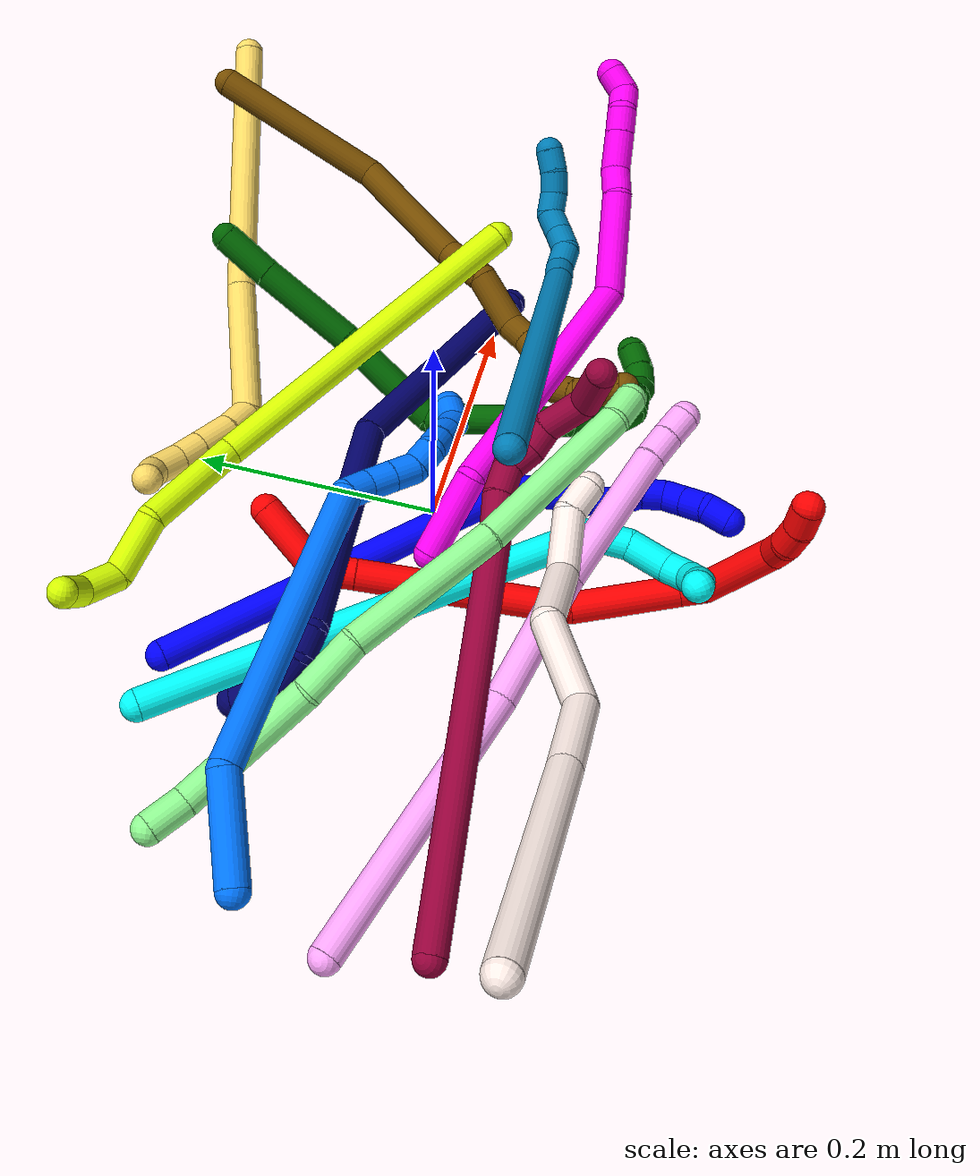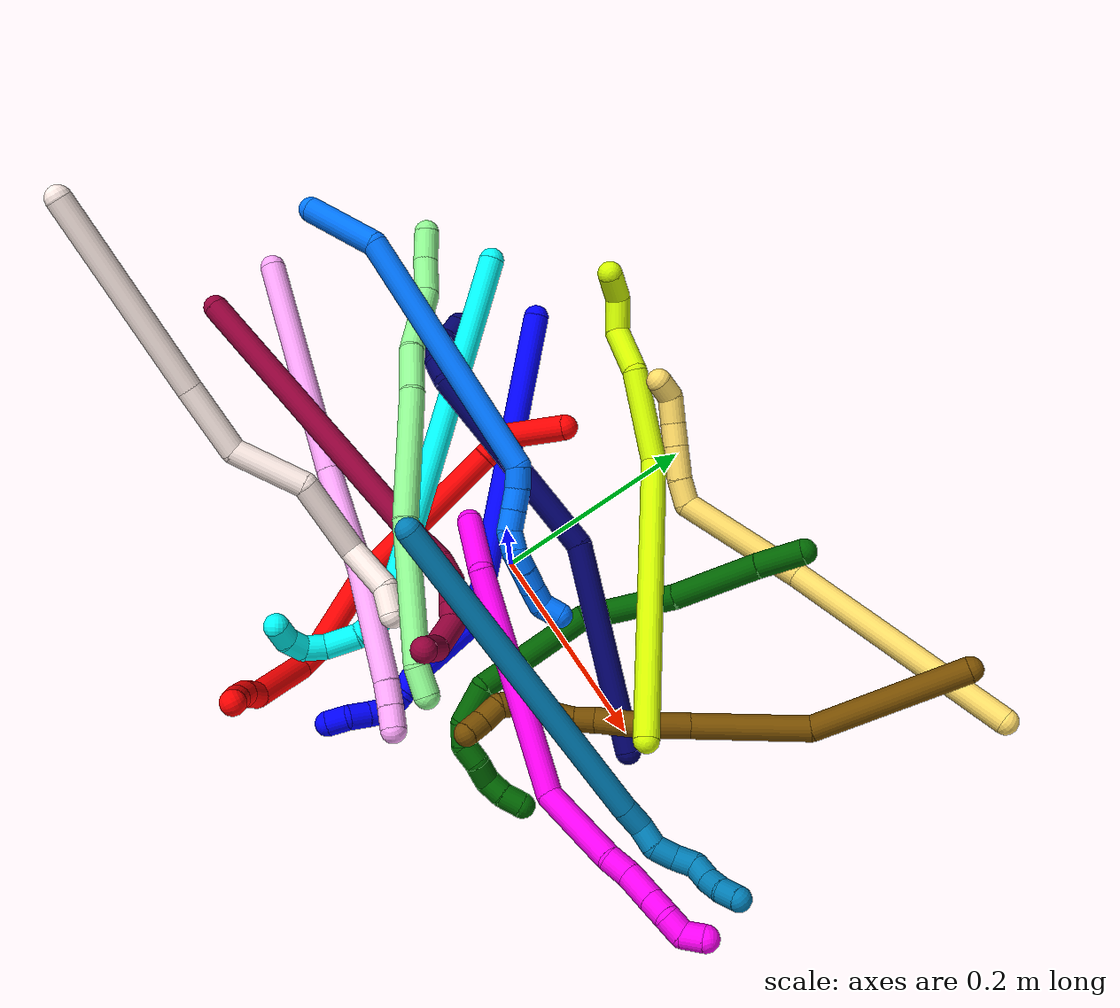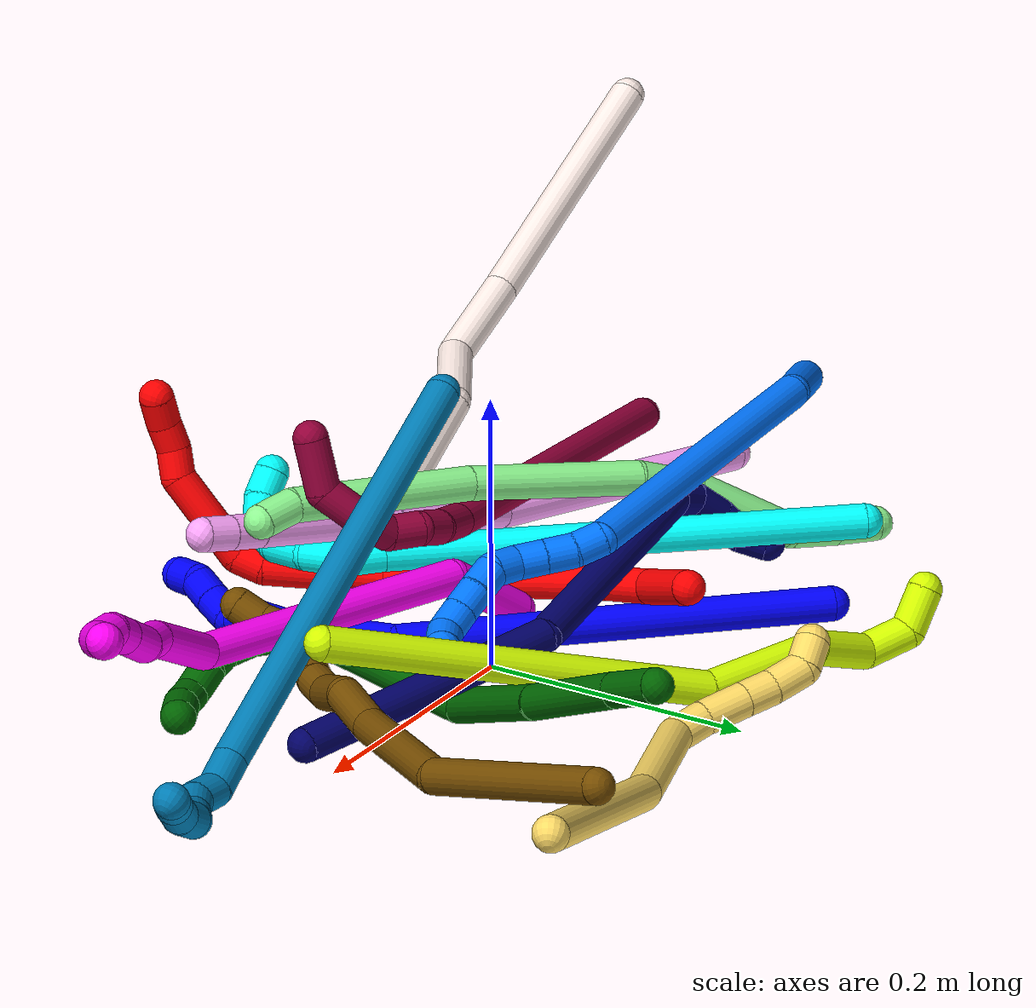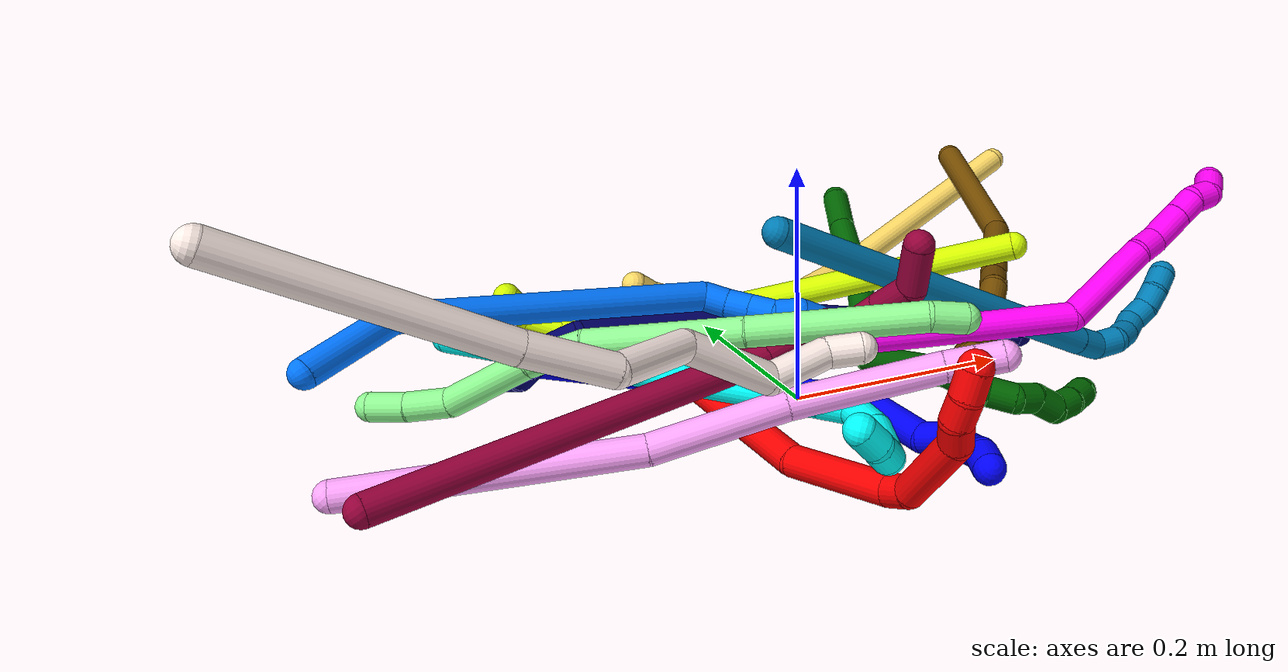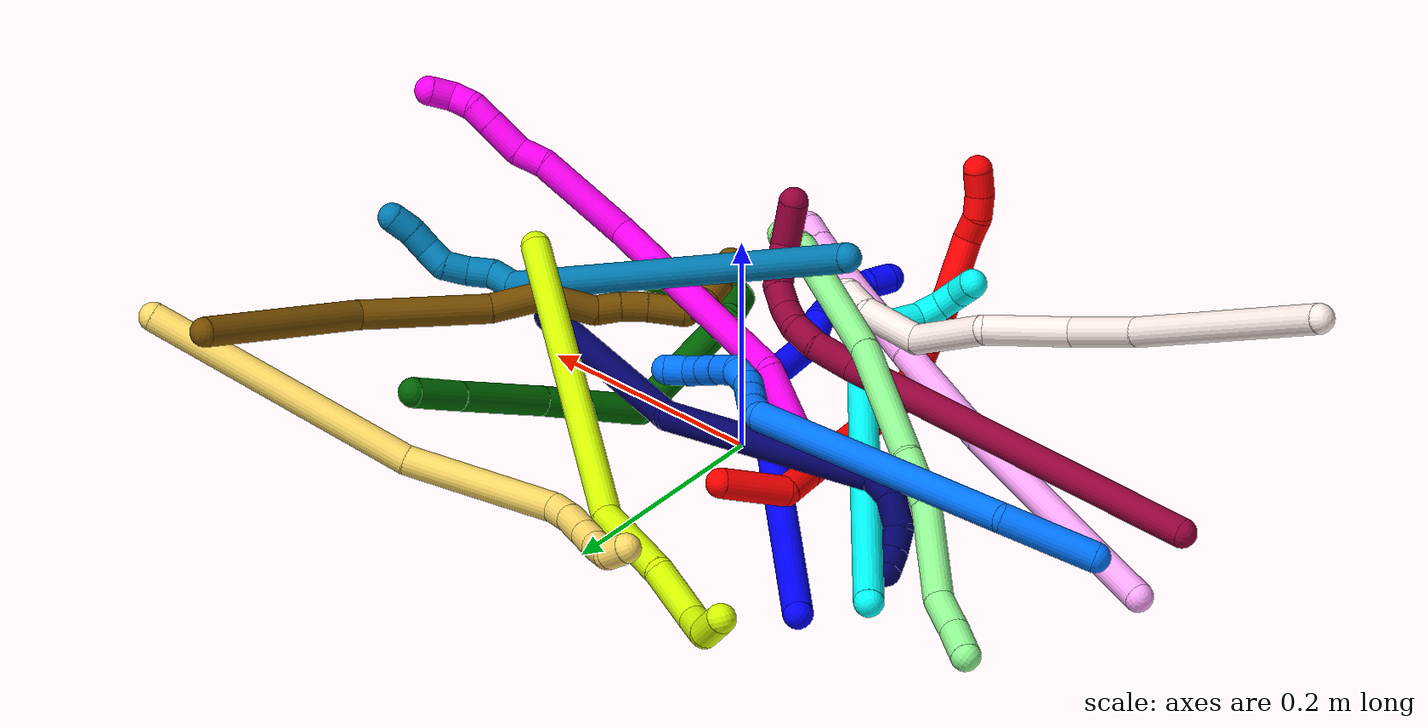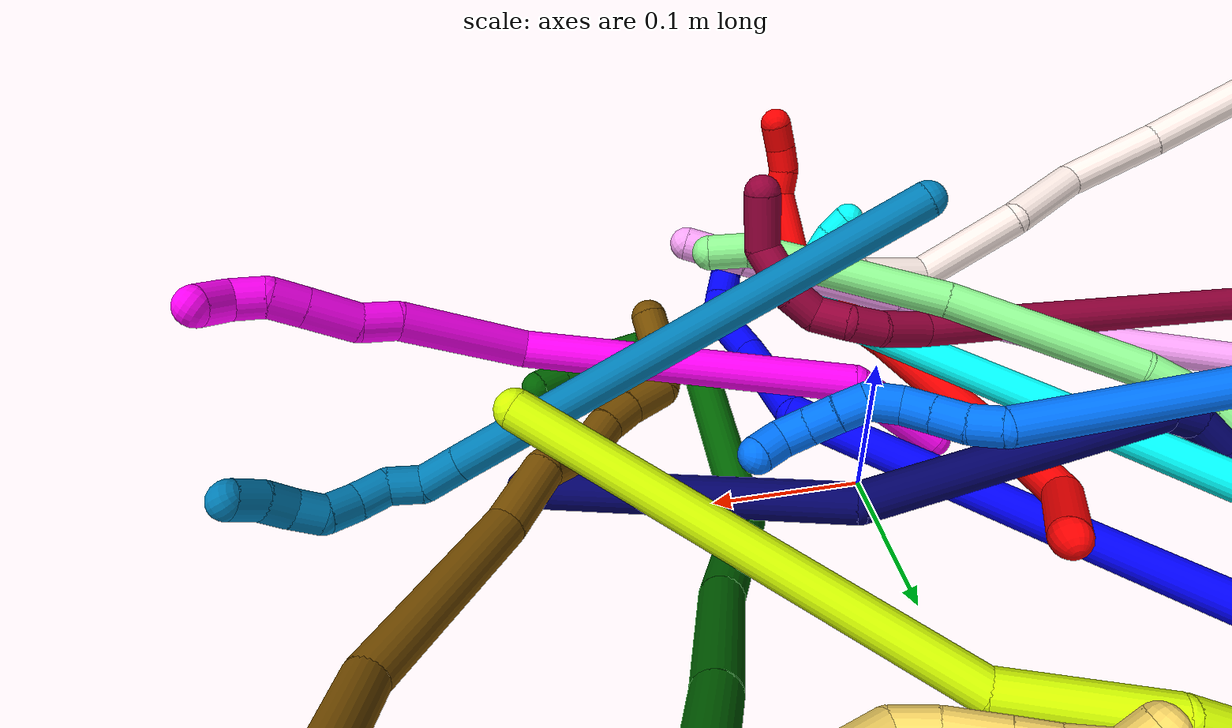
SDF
<sdf version="1.7">
 <world name="default">
  <plugin name="TubeGeneratorPlugin" filename="libtube_generator_plugin.so"/>
  <model name="photoneo_s_sensor">
   <static>1</static>
   <pose>0 0 2 1.57079 1.57079 3.14159</pose>
   <link name="link">
    <inertial><mass>0.1</mass></inertial>
    <sensor name="sensor" type="depth">
     <update_rate>30</update_rate>
     <camera>
      <horizontal_fov>1.22</horizontal_fov>
      <image><width>1920</width><height>1200</height><format>B8G8R8</format></image>
      <clip><near>0.1</near><far>4</far></clip>
      <depth_camera><output>points</output></depth_camera>
     </camera>
     <plugin name="camera_plugin" filename="libgazebo_ros_depth_camera.so">
      <baseline>0.2</baseline>
      <alwaysOn>1</alwaysOn>
      <updateRate>0.0</updateRate>
      <cameraName>camera_ir</cameraName>
      <imageTopicName>/camera/color/image_raw</imageTopicName>
      <cameraInfoTopicName>/camera/color/camera_info</cameraInfoTopicName>
      <depthImageTopicName>/camera/depth/image_raw</depthImageTopicName>
      <depthImageCameraInfoTopicName>/camera/depth/camera_info</depthImageCameraInfoTopicName>
      <pointCloudTopicName>/camera/depth/points</pointCloudTopicName>
      <frameName>fr_optical</frameName>
      <pointCloudCutoff>0.1</pointCloudCutoff>
      <pointCloudCutoffMax>2.0</pointCloudCutoffMax>
      <distortionK1>0</distortionK1>
      <distortionK2>0</distortionK2>
      <distortionK3>0</distortionK3>
      <distortionT1>0</distortionT1>
      <distortionT2>0</distortionT2>
      <CxPrime>0</CxPrime>
      <Cx>0</Cx>
      <Cy>0</Cy>
      <focalLength>0</focalLength>
      <hackBaseline>0</hackBaseline>
     </plugin>
    </sensor>
   </link>
  </model>
  <gravity>0 0 -9.8</gravity>
  <magnetic_field>6e-06 2.3e-05 -4.2e-05</magnetic_field>
  <atmosphere type="adiabatic"/>
  <physics name="default_physics" default="0" type="ode">
   <max_step_size>0.003</max_step_size>
   <real_time_factor>1</real_time_factor>
   <real_time_update_rate>1000</real_time_update_rate>
   <max_contacts>10000</max_contacts>
   <ode>
    <solver>
     <type>quick</type>
     <iters>100</iters>
     <sor>1.3</sor>
     <use_dynamic_moi_rescaling>0</use_dynamic_moi_rescaling>
    </solver>
    <constraints>
     <contact_max_correcting_vel>0</contact_max_correcting_vel>
     <contact_surface_layer>0.001</contact_surface_layer>
     <cfm>0</cfm>
     <erp>0.2</erp>
    </constraints>
   </ode>
  </physics>
  <scene><ambient>0.4 0.4 0.4 1</ambient><background>0.7 0.7 0.7 1</background><shadows>0</shadows></scene>
  <audio><device>default</device></audio>
  <spherical_coordinates>
   <surface_model>EARTH_WGS84</surface_model>
   <latitude_deg>0</latitude_deg>
   <longitude_deg>0</longitude_deg>
   <elevation>0</elevation>
   <heading_deg>0</heading_deg>
  </spherical_coordinates>
  <model name="bin">
   <static>1</static>
   <link name="bottom">
    <collision name="collision-bottom">
     <pose>0 0 -0.01 0 -0 0</pose>
     <geometry><box><size>0.8 0.6 0.02</size></box></geometry>
     <surface>
      <friction><ode><mu>100</mu><mu2>100</mu2></ode></friction>
      <contact><collide_bitmask>65535</collide_bitmask></contact>
     </surface>
    </collision>
   </link>
   <link name="west_wall">
    <collision name="collision-west_wall">
     <pose>-0.41 0 0.1 0 -0 0</pose>
     <geometry><box><size>0.02 0.6 0.2</size></box></geometry>
     <surface>
      <friction><ode><mu>100</mu><mu2>100</mu2></ode></friction>
      <contact><collide_bitmask>65535</collide_bitmask></contact>
     </surface>
    </collision>
   </link>
   <link name="east_wall">
    <collision name="collision-east_wall">
     <pose>0.41 0 0.1 0 -0 0</pose>
     <geometry><box><size>0.02 0.6 0.2</size></box></geometry>
     <surface>
      <friction><ode><mu>100</mu><mu2>100</mu2></ode></friction>
      <contact><collide_bitmask>65535</collide_bitmask></contact>
     </surface>
    </collision>
   </link>
   <link name="south_wall">
    <collision name="collision-south_wall">
     <pose>0 -0.31 0.1 0 -0 0</pose>
     <geometry><box><size>0.8 0.02 0.2</size></box></geometry>
     <surface>
      <friction><ode><mu>100</mu><mu2>100</mu2></ode></friction>
      <contact><collide_bitmask>65535</collide_bitmask></contact>
     </surface>
    </collision>
   </link>
   <link name="north_wall">
    <collision name="collision-north_wall">
     <pose>0 0.31 0.1 0 -0 0</pose>
     <geometry><box><size>0.8 0.02 0.2</size></box></geometry>
     <surface>
      <friction><ode><mu>100</mu><mu2>100</mu2></ode></friction>
      <contact><collide_bitmask>65535</collide_bitmask></contact>
     </surface>
    </collision>
   </link>
  </model>
  <model name="1">
   <static>0</static>
   <link name="1">
    <collision name="collision-cylinder-e_1_1_4">
     <pose>0.115929 -0.083799 0.064862 0.9121 0.830254 0.425846</pose>
     <geometry><cylinder><radius>0.0125</radius><length>0.314126</length></cylinder></geometry>
     <surface>
      <friction><ode><mu>1.16</mu><mu2>1.16</mu2><slip1>0</slip1><slip2>0</slip2></ode></friction>
      <contact><ode><kp>1e+06</kp><kd>1</kd><max_vel>0</max_vel><min_depth>0.001</min_depth></ode></contact>
     </surface>
    </collision>
    <visual name="visual-cylinder-e_1_1_4">
     <pose>0.115929 -0.083799 0.064862 0.9121 0.830254 0.425846</pose>
     <geometry><cylinder><radius>0.0125</radius><length>0.314126</length></cylinder></geometry>
     <material><ambient>0 0 1 1</ambient></material>
    </visual>
    <collision name="collision-cylinder-e_2_4_5">
     <pose>0.238741 -0.195018 0.157194 0.784486 0.175518 0.072763</pose>
     <geometry><cylinder><radius>0.0125</radius><length>0.078838</length></cylinder></geometry>
     <surface>
      <friction><ode><mu>1.16</mu><mu2>1.16</mu2><slip1>0</slip1><slip2>0</slip2></ode></friction>
      <contact><ode><kp>1e+06</kp><kd>1</kd><max_vel>0</max_vel><min_depth>0.001</min_depth></ode></contact>
     </surface>
    </collision>
    <visual name="visual-cylinder-e_2_4_5">
     <pose>0.238741 -0.195018 0.157194 0.784486 0.175518 0.072763</pose>
     <geometry><cylinder><radius>0.0125</radius><length>0.078838</length></cylinder></geometry>
     <material><ambient>0 0 1 1</ambient></material>
    </visual>
    <collision name="collision-cylinder-e_3_5_6">
     <pose>0.252108 -0.227545 0.194391 0.483431 0.533252 0.134469</pose>
     <geometry><cylinder><radius>0.0125</radius><length>0.025511</length></cylinder></geometry>
     <surface>
      <friction><ode><mu>1.16</mu><mu2>1.16</mu2><slip1>0</slip1><slip2>0</slip2></ode></friction>
      <contact><ode><kp>1e+06</kp><kd>1</kd><max_vel>0</max_vel><min_depth>0.001</min_depth></ode></contact>
     </surface>
    </collision>
    <visual name="visual-cylinder-e_3_5_6">
     <pose>0.252108 -0.227545 0.194391 0.483431 0.533252 0.134469</pose>
     <geometry><cylinder><radius>0.0125</radius><length>0.025511</length></cylinder></geometry>
     <material><ambient>0 0 1 1</ambient></material>
    </visual>
    <collision name="collision-cylinder-e_4_6_7">
     <pose>0.261624 -0.240184 0.210418 0.874201 0.299368 0.140699</pose>
     <geometry><cylinder><radius>0.0125</radius><length>0.020557</length></cylinder></geometry>
     <surface>
      <friction><ode><mu>1.16</mu><mu2>1.16</mu2><slip1>0</slip1><slip2>0</slip2></ode></friction>
      <contact><ode><kp>1e+06</kp><kd>1</kd><max_vel>0</max_vel><min_depth>0.001</min_depth></ode></contact>
     </surface>
    </collision>
    <visual name="visual-cylinder-e_4_6_7">
     <pose>0.261624 -0.240184 0.210418 0.874201 0.299368 0.140699</pose>
     <geometry><cylinder><radius>0.0125</radius><length>0.020557</length></cylinder></geometry>
     <material><ambient>0 0 1 1</ambient></material>
    </visual>
    <collision name="collision-cylinder-e_5_7_8">
     <pose>0.262576 -0.250672 0.22627 0.300043 -0.205005 -0.031095</pose>
     <geometry><cylinder><radius>0.0125</radius><length>0.020423</length></cylinder></geometry>
     <surface>
      <friction><ode><mu>1.16</mu><mu2>1.16</mu2><slip1>0</slip1><slip2>0</slip2></ode></friction>
      <contact><ode><kp>1e+06</kp><kd>1</kd><max_vel>0</max_vel><min_depth>0.001</min_depth></ode></contact>
     </surface>
    </collision>
    <visual name="visual-cylinder-e_5_7_8">
     <pose>0.262576 -0.250672 0.22627 0.300043 -0.205005 -0.031095</pose>
     <geometry><cylinder><radius>0.0125</radius><length>0.020423</length></cylinder></geometry>
     <material><ambient>0 0 1 1</ambient></material>
    </visual>
    <collision name="collision-cylinder-e_6_8_9">
     <pose>0.258176 -0.256076 0.245378 0.250825 -0.231144 -0.02927</pose>
     <geometry><cylinder><radius>0.0125</radius><length>0.02027</length></cylinder></geometry>
     <surface>
      <friction><ode><mu>1.16</mu><mu2>1.16</mu2><slip1>0</slip1><slip2>0</slip2></ode></friction>
      <contact><ode><kp>1e+06</kp><kd>1</kd><max_vel>0</max_vel><min_depth>0.001</min_depth></ode></contact>
     </surface>
    </collision>
    <visual name="visual-cylinder-e_6_8_9">
     <pose>0.258176 -0.256076 0.245378 0.250825 -0.231144 -0.02927</pose>
     <geometry><cylinder><radius>0.0125</radius><length>0.02027</length></cylinder></geometry>
     <material><ambient>0 0 1 1</ambient></material>
    </visual>
    <collision name="collision-cylinder-e_7_9_2">
     <pose>0.253202 -0.265031 0.262241 0.727573 -0.264707 -0.101289</pose>
     <geometry><cylinder><radius>0.0125</radius><length>0.020274</length></cylinder></geometry>
     <surface>
      <friction><ode><mu>1.16</mu><mu2>1.16</mu2><slip1>0</slip1><slip2>0</slip2></ode></friction>
      <contact><ode><kp>1e+06</kp><kd>1</kd><max_vel>0</max_vel><min_depth>0.001</min_depth></ode></contact>
     </surface>
    </collision>
    <visual name="visual-cylinder-e_7_9_2">
     <pose>0.253202 -0.265031 0.262241 0.727573 -0.264707 -0.101289</pose>
     <geometry><cylinder><radius>0.0125</radius><length>0.020274</length></cylinder></geometry>
     <material><ambient>0 0 1 1</ambient></material>
    </visual>
    <collision name="collision-sphere-2">
     <pose>0.25055 -0.271538 0.269548 0 -0 0</pose>
     <geometry><sphere><radius>0.0125</radius></sphere></geometry>
     <surface>
      <friction><ode><mu>1.16</mu><mu2>1.16</mu2><slip1>0</slip1><slip2>0</slip2></ode></friction>
      <contact><ode><kp>1e+06</kp><kd>1</kd><max_vel>0</max_vel><min_depth>0.001</min_depth></ode></contact>
     </surface>
    </collision>
    <visual name="visual-sphere-2">
     <pose>0.25055 -0.271538 0.269548 0 -0 0</pose>
     <geometry><sphere><radius>0.0125</radius></sphere></geometry>
     <material><ambient>0 0 1 1</ambient></material>
    </visual>
    <collision name="collision-sphere-9">
     <pose>0.255854 -0.258524 0.254935 0 -0 0</pose>
     <geometry><sphere><radius>0.0125</radius></sphere></geometry>
     <surface>
      <friction><ode><mu>1.16</mu><mu2>1.16</mu2><slip1>0</slip1><slip2>0</slip2></ode></friction>
      <contact><ode><kp>1e+06</kp><kd>1</kd><max_vel>0</max_vel><min_depth>0.001</min_depth></ode></contact>
     </surface>
    </collision>
    <visual name="visual-sphere-9">
     <pose>0.255854 -0.258524 0.254935 0 -0 0</pose>
     <geometry><sphere><radius>0.0125</radius></sphere></geometry>
     <material><ambient>0 0 1 1</ambient></material>
    </visual>
    <collision name="collision-sphere-4">
     <pose>0.231858 -0.167598 0.129724 0 -0 0</pose>
     <geometry><sphere><radius>0.0125</radius></sphere></geometry>
     <surface>
      <friction><ode><mu>1.16</mu><mu2>1.16</mu2><slip1>0</slip1><slip2>0</slip2></ode></friction>
      <contact><ode><kp>1e+06</kp><kd>1</kd><max_vel>0</max_vel><min_depth>0.001</min_depth></ode></contact>
     </surface>
    </collision>
    <visual name="visual-sphere-4">
     <pose>0.231858 -0.167598 0.129724 0 -0 0</pose>
     <geometry><sphere><radius>0.0125</radius></sphere></geometry>
     <material><ambient>0 0 1 1</ambient></material>
    </visual>
    <collision name="collision-sphere-1">
     <geometry><sphere><radius>0.0125</radius></sphere></geometry>
     <surface>
      <friction><ode><mu>1.16</mu><mu2>1.16</mu2><slip1>0</slip1><slip2>0</slip2></ode></friction>
      <contact><ode><kp>1e+06</kp><kd>1</kd><max_vel>0</max_vel><min_depth>0.001</min_depth></ode></contact>
     </surface>
    </collision>
    <visual name="visual-sphere-1">
     <geometry><sphere><radius>0.0125</radius></sphere></geometry>
     <material><ambient>0 0 1 1</ambient></material>
    </visual>
    <collision name="collision-sphere-8">
     <pose>0.260498 -0.253627 0.235821 0 -0 0</pose>
     <geometry><sphere><radius>0.0125</radius></sphere></geometry>
     <surface>
      <friction><ode><mu>1.16</mu><mu2>1.16</mu2><slip1>0</slip1><slip2>0</slip2></ode></friction>
      <contact><ode><kp>1e+06</kp><kd>1</kd><max_vel>0</max_vel><min_depth>0.001</min_depth></ode></contact>
     </surface>
    </collision>
    <visual name="visual-sphere-8">
     <pose>0.260498 -0.253627 0.235821 0 -0 0</pose>
     <geometry><sphere><radius>0.0125</radius></sphere></geometry>
     <material><ambient>0 0 1 1</ambient></material>
    </visual>
    <collision name="collision-sphere-5">
     <pose>0.245624 -0.222439 0.184665 0 -0 0</pose>
     <geometry><sphere><radius>0.0125</radius></sphere></geometry>
     <surface>
      <friction><ode><mu>1.16</mu><mu2>1.16</mu2><slip1>0</slip1><slip2>0</slip2></ode></friction>
      <contact><ode><kp>1e+06</kp><kd>1</kd><max_vel>0</max_vel><min_depth>0.001</min_depth></ode></contact>
     </surface>
    </collision>
    <visual name="visual-sphere-5">
     <pose>0.245624 -0.222439 0.184665 0 -0 0</pose>
     <geometry><sphere><radius>0.0125</radius></sphere></geometry>
     <material><ambient>0 0 1 1</ambient></material>
    </visual>
    <collision name="collision-sphere-6">
     <pose>0.258592 -0.23265 0.204116 0 -0 0</pose>
     <geometry><sphere><radius>0.0125</radius></sphere></geometry>
     <surface>
      <friction><ode><mu>1.16</mu><mu2>1.16</mu2><slip1>0</slip1><slip2>0</slip2></ode></friction>
      <contact><ode><kp>1e+06</kp><kd>1</kd><max_vel>0</max_vel><min_depth>0.001</min_depth></ode></contact>
     </surface>
    </collision>
    <visual name="visual-sphere-6">
     <pose>0.258592 -0.23265 0.204116 0 -0 0</pose>
     <geometry><sphere><radius>0.0125</radius></sphere></geometry>
     <material><ambient>0 0 1 1</ambient></material>
    </visual>
    <collision name="collision-sphere-7">
     <pose>0.264655 -0.247717 0.21672 0 -0 0</pose>
     <geometry><sphere><radius>0.0125</radius></sphere></geometry>
     <surface>
      <friction><ode><mu>1.16</mu><mu2>1.16</mu2><slip1>0</slip1><slip2>0</slip2></ode></friction>
      <contact><ode><kp>1e+06</kp><kd>1</kd><max_vel>0</max_vel><min_depth>0.001</min_depth></ode></contact>
     </surface>
    </collision>
    <visual name="visual-sphere-7">
     <pose>0.264655 -0.247717 0.21672 0 -0 0</pose>
     <geometry><sphere><radius>0.0125</radius></sphere></geometry>
     <material><ambient>0 0 1 1</ambient></material>
    </visual>
    <inertial>
     <pose>0.165555 -0.136248 0.113928 0 -0 0</pose>
     <mass>0.5</mass>
     <inertia>
      <ixx>0.002392</ixx>
      <ixy>0</ixy>
      <ixz>0</ixz>
      <iyy>0.002817</iyy>
      <iyz>0</iyz>
      <izz>-0.000484</izz>
     </inertia>
    </inertial>
   </link>
   <pose>-0.194068 0.160653 0.011495 0.882507 -0.218319 -0.061393</pose>
  </model>
  <model name="2">
   <static>0</static>
   <link name="2">
    <collision name="collision-cylinder-e_1_1_4">
     <pose>-0.017502 -0.000543 0.024402 0.02223 -0.622085 -0.007147</pose>
     <geometry><cylinder><radius>0.0125</radius><length>0.060068</length></cylinder></geometry>
     <surface>
      <friction><ode><mu>1.16</mu><mu2>1.16</mu2><slip1>0</slip1><slip2>0</slip2></ode></friction>
      <contact><ode><kp>1e+06</kp><kd>1</kd><max_vel>0</max_vel><min_depth>0.001</min_depth></ode></contact>
     </surface>
    </collision>
    <visual name="visual-cylinder-e_1_1_4">
     <pose>-0.017502 -0.000543 0.024402 0.02223 -0.622085 -0.007147</pose>
     <geometry><cylinder><radius>0.0125</radius><length>0.060068</length></cylinder></geometry>
     <material><ambient>1 0 0 1</ambient></material>
    </visual>
    <collision name="collision-cylinder-e_2_4_5">
     <pose>-0.034318 -0.005757 0.063629 0.305264 0.044051 0.006777</pose>
     <geometry><cylinder><radius>0.0125</radius><length>0.031119</length></cylinder></geometry>
     <surface>
      <friction><ode><mu>1.16</mu><mu2>1.16</mu2><slip1>0</slip1><slip2>0</slip2></ode></friction>
      <contact><ode><kp>1e+06</kp><kd>1</kd><max_vel>0</max_vel><min_depth>0.001</min_depth></ode></contact>
     </surface>
    </collision>
    <visual name="visual-cylinder-e_2_4_5">
     <pose>-0.034318 -0.005757 0.063629 0.305264 0.044051 0.006777</pose>
     <geometry><cylinder><radius>0.0125</radius><length>0.031119</length></cylinder></geometry>
     <material><ambient>1 0 0 1</ambient></material>
    </visual>
    <collision name="collision-cylinder-e_3_5_6">
     <pose>-0.031481 -0.040015 0.156982 0.360311 0.025644 0.004671</pose>
     <geometry><cylinder><radius>0.0125</radius><length>0.167886</length></cylinder></geometry>
     <surface>
      <friction><ode><mu>1.16</mu><mu2>1.16</mu2><slip1>0</slip1><slip2>0</slip2></ode></friction>
      <contact><ode><kp>1e+06</kp><kd>1</kd><max_vel>0</max_vel><min_depth>0.001</min_depth></ode></contact>
     </surface>
    </collision>
    <visual name="visual-cylinder-e_3_5_6">
     <pose>-0.031481 -0.040015 0.156982 0.360311 0.025644 0.004671</pose>
     <geometry><cylinder><radius>0.0125</radius><length>0.167886</length></cylinder></geometry>
     <material><ambient>1 0 0 1</ambient></material>
    </visual>
    <collision name="collision-cylinder-e_4_6_7">
     <pose>-0.015305 -0.087535 0.273129 0.444873 0.324589 0.074033</pose>
     <geometry><cylinder><radius>0.0125</radius><length>0.087945</length></cylinder></geometry>
     <surface>
      <friction><ode><mu>1.16</mu><mu2>1.16</mu2><slip1>0</slip1><slip2>0</slip2></ode></friction>
      <contact><ode><kp>1e+06</kp><kd>1</kd><max_vel>0</max_vel><min_depth>0.001</min_depth></ode></contact>
     </surface>
    </collision>
    <visual name="visual-cylinder-e_4_6_7">
     <pose>-0.015305 -0.087535 0.273129 0.444873 0.324589 0.074033</pose>
     <geometry><cylinder><radius>0.0125</radius><length>0.087945</length></cylinder></geometry>
     <material><ambient>1 0 0 1</ambient></material>
    </visual>
    <collision name="collision-cylinder-e_5_7_8">
     <pose>0.002676 -0.106318 0.320192 0.089483 0.395407 0.017937</pose>
     <geometry><cylinder><radius>0.0125</radius><length>0.020547</length></cylinder></geometry>
     <surface>
      <friction><ode><mu>1.16</mu><mu2>1.16</mu2><slip1>0</slip1><slip2>0</slip2></ode></friction>
      <contact><ode><kp>1e+06</kp><kd>1</kd><max_vel>0</max_vel><min_depth>0.001</min_depth></ode></contact>
     </surface>
    </collision>
    <visual name="visual-cylinder-e_5_7_8">
     <pose>0.002676 -0.106318 0.320192 0.089483 0.395407 0.017937</pose>
     <geometry><cylinder><radius>0.0125</radius><length>0.020547</length></cylinder></geometry>
     <material><ambient>1 0 0 1</ambient></material>
    </visual>
    <collision name="collision-cylinder-e_6_8_9">
     <pose>0.028715 -0.094807 0.353643 -0.475359 0.685473 -0.172456</pose>
     <geometry><cylinder><radius>0.0125</radius><length>0.069764</length></cylinder></geometry>
     <surface>
      <friction><ode><mu>1.16</mu><mu2>1.16</mu2><slip1>0</slip1><slip2>0</slip2></ode></friction>
      <contact><ode><kp>1e+06</kp><kd>1</kd><max_vel>0</max_vel><min_depth>0.001</min_depth></ode></contact>
     </surface>
    </collision>
    <visual name="visual-cylinder-e_6_8_9">
     <pose>0.028715 -0.094807 0.353643 -0.475359 0.685473 -0.172456</pose>
     <geometry><cylinder><radius>0.0125</radius><length>0.069764</length></cylinder></geometry>
     <material><ambient>1 0 0 1</ambient></material>
    </visual>
    <collision name="collision-cylinder-e_7_9_10">
     <pose>0.056323 -0.074516 0.382066 -1.06311 0.546816 -0.326849</pose>
     <geometry><cylinder><radius>0.0125</radius><length>0.021256</length></cylinder></geometry>
     <surface>
      <friction><ode><mu>1.16</mu><mu2>1.16</mu2><slip1>0</slip1><slip2>0</slip2></ode></friction>
      <contact><ode><kp>1e+06</kp><kd>1</kd><max_vel>0</max_vel><min_depth>0.001</min_depth></ode></contact>
     </surface>
    </collision>
    <visual name="visual-cylinder-e_7_9_10">
     <pose>0.056323 -0.074516 0.382066 -1.06311 0.546816 -0.326849</pose>
     <geometry><cylinder><radius>0.0125</radius><length>0.021256</length></cylinder></geometry>
     <material><ambient>1 0 0 1</ambient></material>
    </visual>
    <collision name="collision-cylinder-e_8_10_11">
     <pose>0.069616 -0.061539 0.390255 -0.928247 0.889295 -0.468288</pose>
     <geometry><cylinder><radius>0.0125</radius><length>0.020001</length></cylinder></geometry>
     <surface>
      <friction><ode><mu>1.16</mu><mu2>1.16</mu2><slip1>0</slip1><slip2>0</slip2></ode></friction>
      <contact><ode><kp>1e+06</kp><kd>1</kd><max_vel>0</max_vel><min_depth>0.001</min_depth></ode></contact>
     </surface>
    </collision>
    <visual name="visual-cylinder-e_8_10_11">
     <pose>0.069616 -0.061539 0.390255 -0.928247 0.889295 -0.468288</pose>
     <geometry><cylinder><radius>0.0125</radius><length>0.020001</length></cylinder></geometry>
     <material><ambient>1 0 0 1</ambient></material>
    </visual>
    <collision name="collision-cylinder-e_9_11_2">
     <pose>0.086529 -0.051293 0.396007 -1.20762 1.02415 -0.739705</pose>
     <geometry><cylinder><radius>0.0125</radius><length>0.021413</length></cylinder></geometry>
     <surface>
      <friction><ode><mu>1.16</mu><mu2>1.16</mu2><slip1>0</slip1><slip2>0</slip2></ode></friction>
      <contact><ode><kp>1e+06</kp><kd>1</kd><max_vel>0</max_vel><min_depth>0.001</min_depth></ode></contact>
     </surface>
    </collision>
    <visual name="visual-cylinder-e_9_11_2">
     <pose>0.086529 -0.051293 0.396007 -1.20762 1.02415 -0.739705</pose>
     <geometry><cylinder><radius>0.0125</radius><length>0.021413</length></cylinder></geometry>
     <material><ambient>1 0 0 1</ambient></material>
    </visual>
    <collision name="collision-sphere-2">
     <pose>0.095675 -0.04609 0.397984 0 -0 0</pose>
     <geometry><sphere><radius>0.0125</radius></sphere></geometry>
     <surface>
      <friction><ode><mu>1.16</mu><mu2>1.16</mu2><slip1>0</slip1><slip2>0</slip2></ode></friction>
      <contact><ode><kp>1e+06</kp><kd>1</kd><max_vel>0</max_vel><min_depth>0.001</min_depth></ode></contact>
     </surface>
    </collision>
    <visual name="visual-sphere-2">
     <pose>0.095675 -0.04609 0.397984 0 -0 0</pose>
     <geometry><sphere><radius>0.0125</radius></sphere></geometry>
     <material><ambient>1 0 0 1</ambient></material>
    </visual>
    <collision name="collision-sphere-11">
     <pose>0.077383 -0.056495 0.39403 0 -0 0</pose>
     <geometry><sphere><radius>0.0125</radius></sphere></geometry>
     <surface>
      <friction><ode><mu>1.16</mu><mu2>1.16</mu2><slip1>0</slip1><slip2>0</slip2></ode></friction>
      <contact><ode><kp>1e+06</kp><kd>1</kd><max_vel>0</max_vel><min_depth>0.001</min_depth></ode></contact>
     </surface>
    </collision>
    <visual name="visual-sphere-11">
     <pose>0.077383 -0.056495 0.39403 0 -0 0</pose>
     <geometry><sphere><radius>0.0125</radius></sphere></geometry>
     <material><ambient>1 0 0 1</ambient></material>
    </visual>
    <collision name="collision-sphere-10">
     <pose>0.061849 -0.066582 0.386479 0 -0 0</pose>
     <geometry><sphere><radius>0.0125</radius></sphere></geometry>
     <surface>
      <friction><ode><mu>1.16</mu><mu2>1.16</mu2><slip1>0</slip1><slip2>0</slip2></ode></friction>
      <contact><ode><kp>1e+06</kp><kd>1</kd><max_vel>0</max_vel><min_depth>0.001</min_depth></ode></contact>
     </surface>
    </collision>
    <visual name="visual-sphere-10">
     <pose>0.061849 -0.066582 0.386479 0 -0 0</pose>
     <geometry><sphere><radius>0.0125</radius></sphere></geometry>
     <material><ambient>1 0 0 1</ambient></material>
    </visual>
    <collision name="collision-sphere-9">
     <pose>0.050796 -0.082449 0.377652 0 -0 0</pose>
     <geometry><sphere><radius>0.0125</radius></sphere></geometry>
     <surface>
      <friction><ode><mu>1.16</mu><mu2>1.16</mu2><slip1>0</slip1><slip2>0</slip2></ode></friction>
      <contact><ode><kp>1e+06</kp><kd>1</kd><max_vel>0</max_vel><min_depth>0.001</min_depth></ode></contact>
     </surface>
    </collision>
    <visual name="visual-sphere-9">
     <pose>0.050796 -0.082449 0.377652 0 -0 0</pose>
     <geometry><sphere><radius>0.0125</radius></sphere></geometry>
     <material><ambient>1 0 0 1</ambient></material>
    </visual>
    <collision name="collision-sphere-4">
     <pose>-0.035004 -0.001085 0.048803 0 -0 0</pose>
     <geometry><sphere><radius>0.0125</radius></sphere></geometry>
     <surface>
      <friction><ode><mu>1.16</mu><mu2>1.16</mu2><slip1>0</slip1><slip2>0</slip2></ode></friction>
      <contact><ode><kp>1e+06</kp><kd>1</kd><max_vel>0</max_vel><min_depth>0.001</min_depth></ode></contact>
     </surface>
    </collision>
    <visual name="visual-sphere-4">
     <pose>-0.035004 -0.001085 0.048803 0 -0 0</pose>
     <geometry><sphere><radius>0.0125</radius></sphere></geometry>
     <material><ambient>1 0 0 1</ambient></material>
    </visual>
    <collision name="collision-sphere-1">
     <geometry><sphere><radius>0.0125</radius></sphere></geometry>
     <surface>
      <friction><ode><mu>1.16</mu><mu2>1.16</mu2><slip1>0</slip1><slip2>0</slip2></ode></friction>
      <contact><ode><kp>1e+06</kp><kd>1</kd><max_vel>0</max_vel><min_depth>0.001</min_depth></ode></contact>
     </surface>
    </collision>
    <visual name="visual-sphere-1">
     <geometry><sphere><radius>0.0125</radius></sphere></geometry>
     <material><ambient>1 0 0 1</ambient></material>
    </visual>
    <collision name="collision-sphere-8">
     <pose>0.006633 -0.107165 0.329635 0 -0 0</pose>
     <geometry><sphere><radius>0.0125</radius></sphere></geometry>
     <surface>
      <friction><ode><mu>1.16</mu><mu2>1.16</mu2><slip1>0</slip1><slip2>0</slip2></ode></friction>
      <contact><ode><kp>1e+06</kp><kd>1</kd><max_vel>0</max_vel><min_depth>0.001</min_depth></ode></contact>
     </surface>
    </collision>
    <visual name="visual-sphere-8">
     <pose>0.006633 -0.107165 0.329635 0 -0 0</pose>
     <geometry><sphere><radius>0.0125</radius></sphere></geometry>
     <material><ambient>1 0 0 1</ambient></material>
    </visual>
    <collision name="collision-sphere-5">
     <pose>-0.033633 -0.010429 0.078455 0 -0 0</pose>
     <geometry><sphere><radius>0.0125</radius></sphere></geometry>
     <surface>
      <friction><ode><mu>1.16</mu><mu2>1.16</mu2><slip1>0</slip1><slip2>0</slip2></ode></friction>
      <contact><ode><kp>1e+06</kp><kd>1</kd><max_vel>0</max_vel><min_depth>0.001</min_depth></ode></contact>
     </surface>
    </collision>
    <visual name="visual-sphere-5">
     <pose>-0.033633 -0.010429 0.078455 0 -0 0</pose>
     <geometry><sphere><radius>0.0125</radius></sphere></geometry>
     <material><ambient>1 0 0 1</ambient></material>
    </visual>
    <collision name="collision-sphere-6">
     <pose>-0.029328 -0.0696 0.235509 0 -0 0</pose>
     <geometry><sphere><radius>0.0125</radius></sphere></geometry>
     <surface>
      <friction><ode><mu>1.16</mu><mu2>1.16</mu2><slip1>0</slip1><slip2>0</slip2></ode></friction>
      <contact><ode><kp>1e+06</kp><kd>1</kd><max_vel>0</max_vel><min_depth>0.001</min_depth></ode></contact>
     </surface>
    </collision>
    <visual name="visual-sphere-6">
     <pose>-0.029328 -0.0696 0.235509 0 -0 0</pose>
     <geometry><sphere><radius>0.0125</radius></sphere></geometry>
     <material><ambient>1 0 0 1</ambient></material>
    </visual>
    <collision name="collision-sphere-7">
     <pose>-0.001281 -0.105471 0.310749 0 -0 0</pose>
     <geometry><sphere><radius>0.0125</radius></sphere></geometry>
     <surface>
      <friction><ode><mu>1.16</mu><mu2>1.16</mu2><slip1>0</slip1><slip2>0</slip2></ode></friction>
      <contact><ode><kp>1e+06</kp><kd>1</kd><max_vel>0</max_vel><min_depth>0.001</min_depth></ode></contact>
     </surface>
    </collision>
    <visual name="visual-sphere-7">
     <pose>-0.001281 -0.105471 0.310749 0 -0 0</pose>
     <geometry><sphere><radius>0.0125</radius></sphere></geometry>
     <material><ambient>1 0 0 1</ambient></material>
    </visual>
    <inertial>
     <pose>-0.0045 -0.054679 0.218957 0 -0 0</pose>
     <mass>0.5</mass>
     <inertia>
      <ixx>0.000514</ixx>
      <ixy>0</ixy>
      <ixz>0</ixz>
      <iyy>0.000484</iyy>
      <iyz>0</iyz>
      <izz>0.000143</izz>
     </inertia>
    </inertial>
   </link>
   <pose>-0.074009 0.113885 0.058627 1.43693 -0.809067 -0.007066</pose>
  </model>
  <model name="3">
   <static>0</static>
   <link name="3">
    <collision name="collision-cylinder-e_1_1_4">
     <pose>0.017596 -0.048975 -0.163136 2.84994 0.102943 0.67473</pose>
     <geometry><cylinder><radius>0.0125</radius><length>0.34247</length></cylinder></geometry>
     <surface>
      <friction><ode><mu>1.16</mu><mu2>1.16</mu2><slip1>0</slip1><slip2>0</slip2></ode></friction>
      <contact><ode><kp>1e+06</kp><kd>1</kd><max_vel>0</max_vel><min_depth>0.001</min_depth></ode></contact>
     </surface>
    </collision>
    <visual name="visual-cylinder-e_1_1_4">
     <pose>0.017596 -0.048975 -0.163136 2.84994 0.102943 0.67473</pose>
     <geometry><cylinder><radius>0.0125</radius><length>0.34247</length></cylinder></geometry>
     <material><ambient>0.003922 1 0.996078 1</ambient></material>
    </visual>
    <collision name="collision-cylinder-e_2_4_5">
     <pose>0.036246 -0.1009 -0.338828 2.91084 0.081471 0.676352</pose>
     <geometry><cylinder><radius>0.0125</radius><length>0.025884</length></cylinder></geometry>
     <surface>
      <friction><ode><mu>1.16</mu><mu2>1.16</mu2><slip1>0</slip1><slip2>0</slip2></ode></friction>
      <contact><ode><kp>1e+06</kp><kd>1</kd><max_vel>0</max_vel><min_depth>0.001</min_depth></ode></contact>
     </surface>
    </collision>
    <visual name="visual-cylinder-e_2_4_5">
     <pose>0.036246 -0.1009 -0.338828 2.91084 0.081471 0.676352</pose>
     <geometry><cylinder><radius>0.0125</radius><length>0.025884</length></cylinder></geometry>
     <material><ambient>0.003922 1 0.996078 1</ambient></material>
    </visual>
    <collision name="collision-cylinder-e_3_5_6">
     <pose>0.033401 -0.116398 -0.361907 2.26857 -0.233712 -0.49302</pose>
     <geometry><cylinder><radius>0.0125</radius><length>0.033667</length></cylinder></geometry>
     <surface>
      <friction><ode><mu>1.16</mu><mu2>1.16</mu2><slip1>0</slip1><slip2>0</slip2></ode></friction>
      <contact><ode><kp>1e+06</kp><kd>1</kd><max_vel>0</max_vel><min_depth>0.001</min_depth></ode></contact>
     </surface>
    </collision>
    <visual name="visual-cylinder-e_3_5_6">
     <pose>0.033401 -0.116398 -0.361907 2.26857 -0.233712 -0.49302</pose>
     <geometry><cylinder><radius>0.0125</radius><length>0.033667</length></cylinder></geometry>
     <material><ambient>0.003922 1 0.996078 1</ambient></material>
    </visual>
    <collision name="collision-cylinder-e_4_6_7">
     <pose>0.023014 -0.143701 -0.378597 1.96678 -0.38543 -0.570197</pose>
     <geometry><cylinder><radius>0.0125</radius><length>0.034515</length></cylinder></geometry>
     <surface>
      <friction><ode><mu>1.16</mu><mu2>1.16</mu2><slip1>0</slip1><slip2>0</slip2></ode></friction>
      <contact><ode><kp>1e+06</kp><kd>1</kd><max_vel>0</max_vel><min_depth>0.001</min_depth></ode></contact>
     </surface>
    </collision>
    <visual name="visual-cylinder-e_4_6_7">
     <pose>0.023014 -0.143701 -0.378597 1.96678 -0.38543 -0.570197</pose>
     <geometry><cylinder><radius>0.0125</radius><length>0.034515</length></cylinder></geometry>
     <material><ambient>0.003922 1 0.996078 1</ambient></material>
    </visual>
    <collision name="collision-cylinder-e_5_7_8">
     <pose>0.016472 -0.169401 -0.38562 1.64877 -0.004972 -0.005376</pose>
     <geometry><cylinder><radius>0.0125</radius><length>0.021959</length></cylinder></geometry>
     <surface>
      <friction><ode><mu>1.16</mu><mu2>1.16</mu2><slip1>0</slip1><slip2>0</slip2></ode></friction>
      <contact><ode><kp>1e+06</kp><kd>1</kd><max_vel>0</max_vel><min_depth>0.001</min_depth></ode></contact>
     </surface>
    </collision>
    <visual name="visual-cylinder-e_5_7_8">
     <pose>0.016472 -0.169401 -0.38562 1.64877 -0.004972 -0.005376</pose>
     <geometry><cylinder><radius>0.0125</radius><length>0.021959</length></cylinder></geometry>
     <material><ambient>0.003922 1 0.996078 1</ambient></material>
    </visual>
    <collision name="collision-cylinder-e_6_8_9">
     <pose>0.0203 -0.189225 -0.381925 1.0971 0.371233 0.228507</pose>
     <geometry><cylinder><radius>0.0125</radius><length>0.02141</length></cylinder></geometry>
     <surface>
      <friction><ode><mu>1.16</mu><mu2>1.16</mu2><slip1>0</slip1><slip2>0</slip2></ode></friction>
      <contact><ode><kp>1e+06</kp><kd>1</kd><max_vel>0</max_vel><min_depth>0.001</min_depth></ode></contact>
     </surface>
    </collision>
    <visual name="visual-cylinder-e_6_8_9">
     <pose>0.0203 -0.189225 -0.381925 1.0971 0.371233 0.228507</pose>
     <geometry><cylinder><radius>0.0125</radius><length>0.02141</length></cylinder></geometry>
     <material><ambient>0.003922 1 0.996078 1</ambient></material>
    </visual>
    <collision name="collision-cylinder-e_7_9_2">
     <pose>0.028569 -0.203875 -0.370417 0.692702 0.451628 0.165442</pose>
     <geometry><cylinder><radius>0.0125</radius><length>0.020095</length></cylinder></geometry>
     <surface>
      <friction><ode><mu>1.16</mu><mu2>1.16</mu2><slip1>0</slip1><slip2>0</slip2></ode></friction>
      <contact><ode><kp>1e+06</kp><kd>1</kd><max_vel>0</max_vel><min_depth>0.001</min_depth></ode></contact>
     </surface>
    </collision>
    <visual name="visual-cylinder-e_7_9_2">
     <pose>0.028569 -0.203875 -0.370417 0.692702 0.451628 0.165442</pose>
     <geometry><cylinder><radius>0.0125</radius><length>0.020095</length></cylinder></geometry>
     <material><ambient>0.003922 1 0.996078 1</ambient></material>
    </visual>
    <collision name="collision-sphere-2">
     <pose>0.032954 -0.209648 -0.363461 0 -0 0</pose>
     <geometry><sphere><radius>0.0125</radius></sphere></geometry>
     <surface>
      <friction><ode><mu>1.16</mu><mu2>1.16</mu2><slip1>0</slip1><slip2>0</slip2></ode></friction>
      <contact><ode><kp>1e+06</kp><kd>1</kd><max_vel>0</max_vel><min_depth>0.001</min_depth></ode></contact>
     </surface>
    </collision>
    <visual name="visual-sphere-2">
     <pose>0.032954 -0.209648 -0.363461 0 -0 0</pose>
     <geometry><sphere><radius>0.0125</radius></sphere></geometry>
     <material><ambient>0.003922 1 0.996078 1</ambient></material>
    </visual>
    <collision name="collision-sphere-9">
     <pose>0.024184 -0.198102 -0.377374 0 -0 0</pose>
     <geometry><sphere><radius>0.0125</radius></sphere></geometry>
     <surface>
      <friction><ode><mu>1.16</mu><mu2>1.16</mu2><slip1>0</slip1><slip2>0</slip2></ode></friction>
      <contact><ode><kp>1e+06</kp><kd>1</kd><max_vel>0</max_vel><min_depth>0.001</min_depth></ode></contact>
     </surface>
    </collision>
    <visual name="visual-sphere-9">
     <pose>0.024184 -0.198102 -0.377374 0 -0 0</pose>
     <geometry><sphere><radius>0.0125</radius></sphere></geometry>
     <material><ambient>0.003922 1 0.996078 1</ambient></material>
    </visual>
    <collision name="collision-sphere-4">
     <pose>0.035193 -0.09795 -0.326272 0 -0 0</pose>
     <geometry><sphere><radius>0.0125</radius></sphere></geometry>
     <surface>
      <friction><ode><mu>1.16</mu><mu2>1.16</mu2><slip1>0</slip1><slip2>0</slip2></ode></friction>
      <contact><ode><kp>1e+06</kp><kd>1</kd><max_vel>0</max_vel><min_depth>0.001</min_depth></ode></contact>
     </surface>
    </collision>
    <visual name="visual-sphere-4">
     <pose>0.035193 -0.09795 -0.326272 0 -0 0</pose>
     <geometry><sphere><radius>0.0125</radius></sphere></geometry>
     <material><ambient>0.003922 1 0.996078 1</ambient></material>
    </visual>
    <collision name="collision-sphere-1">
     <geometry><sphere><radius>0.0125</radius></sphere></geometry>
     <surface>
      <friction><ode><mu>1.16</mu><mu2>1.16</mu2><slip1>0</slip1><slip2>0</slip2></ode></friction>
      <contact><ode><kp>1e+06</kp><kd>1</kd><max_vel>0</max_vel><min_depth>0.001</min_depth></ode></contact>
     </surface>
    </collision>
    <visual name="visual-sphere-1">
     <geometry><sphere><radius>0.0125</radius></sphere></geometry>
     <material><ambient>0.003922 1 0.996078 1</ambient></material>
    </visual>
    <collision name="collision-sphere-8">
     <pose>0.016417 -0.180347 -0.386475 0 -0 0</pose>
     <geometry><sphere><radius>0.0125</radius></sphere></geometry>
     <surface>
      <friction><ode><mu>1.16</mu><mu2>1.16</mu2><slip1>0</slip1><slip2>0</slip2></ode></friction>
      <contact><ode><kp>1e+06</kp><kd>1</kd><max_vel>0</max_vel><min_depth>0.001</min_depth></ode></contact>
     </surface>
    </collision>
    <visual name="visual-sphere-8">
     <pose>0.016417 -0.180347 -0.386475 0 -0 0</pose>
     <geometry><sphere><radius>0.0125</radius></sphere></geometry>
     <material><ambient>0.003922 1 0.996078 1</ambient></material>
    </visual>
    <collision name="collision-sphere-5">
     <pose>0.037299 -0.10385 -0.351385 0 -0 0</pose>
     <geometry><sphere><radius>0.0125</radius></sphere></geometry>
     <surface>
      <friction><ode><mu>1.16</mu><mu2>1.16</mu2><slip1>0</slip1><slip2>0</slip2></ode></friction>
      <contact><ode><kp>1e+06</kp><kd>1</kd><max_vel>0</max_vel><min_depth>0.001</min_depth></ode></contact>
     </surface>
    </collision>
    <visual name="visual-sphere-5">
     <pose>0.037299 -0.10385 -0.351385 0 -0 0</pose>
     <geometry><sphere><radius>0.0125</radius></sphere></geometry>
     <material><ambient>0.003922 1 0.996078 1</ambient></material>
    </visual>
    <collision name="collision-sphere-6">
     <pose>0.029502 -0.128947 -0.372429 0 -0 0</pose>
     <geometry><sphere><radius>0.0125</radius></sphere></geometry>
     <surface>
      <friction><ode><mu>1.16</mu><mu2>1.16</mu2><slip1>0</slip1><slip2>0</slip2></ode></friction>
      <contact><ode><kp>1e+06</kp><kd>1</kd><max_vel>0</max_vel><min_depth>0.001</min_depth></ode></contact>
     </surface>
    </collision>
    <visual name="visual-sphere-6">
     <pose>0.029502 -0.128947 -0.372429 0 -0 0</pose>
     <geometry><sphere><radius>0.0125</radius></sphere></geometry>
     <material><ambient>0.003922 1 0.996078 1</ambient></material>
    </visual>
    <collision name="collision-sphere-7">
     <pose>0.016526 -0.158455 -0.384765 0 -0 0</pose>
     <geometry><sphere><radius>0.0125</radius></sphere></geometry>
     <surface>
      <friction><ode><mu>1.16</mu><mu2>1.16</mu2><slip1>0</slip1><slip2>0</slip2></ode></friction>
      <contact><ode><kp>1e+06</kp><kd>1</kd><max_vel>0</max_vel><min_depth>0.001</min_depth></ode></contact>
     </surface>
    </collision>
    <visual name="visual-sphere-7">
     <pose>0.016526 -0.158455 -0.384765 0 -0 0</pose>
     <geometry><sphere><radius>0.0125</radius></sphere></geometry>
     <material><ambient>0.003922 1 0.996078 1</ambient></material>
    </visual>
    <inertial>
     <pose>0.020507 -0.080262 -0.227959 0 -0 0</pose>
     <mass>0.5</mass>
     <inertia>
      <ixx>0.004713</ixx>
      <ixy>0</ixy>
      <ixz>0</ixz>
      <iyy>-0.000385</iyy>
      <iyz>0</iyz>
      <izz>0.000601</izz>
     </inertia>
    </inertial>
   </link>
   <pose>-0.258185 0.150401 0.048371 -1.01133 -1.16983 0.417015</pose>
  </model>
  <model name="4">
   <static>0</static>
   <link name="4">
    <collision name="collision-cylinder-e_1_1_4">
     <pose>0.084315 -0.027856 -0.070144 2.76356 0.840679 2.33281</pose>
     <geometry><cylinder><radius>0.0125</radius><length>0.22632</length></cylinder></geometry>
     <surface>
      <friction><ode><mu>1.16</mu><mu2>1.16</mu2><slip1>0</slip1><slip2>0</slip2></ode></friction>
      <contact><ode><kp>1e+06</kp><kd>1</kd><max_vel>0</max_vel><min_depth>0.001</min_depth></ode></contact>
     </surface>
    </collision>
    <visual name="visual-cylinder-e_1_1_4">
     <pose>0.084315 -0.027856 -0.070144 2.76356 0.840679 2.33281</pose>
     <geometry><cylinder><radius>0.0125</radius><length>0.22632</length></cylinder></geometry>
     <material><ambient>1 0.65098 0.996078 1</ambient></material>
    </visual>
    <collision name="collision-cylinder-e_2_4_5">
     <pose>0.214124 -0.0688 -0.16617 2.67341 1.00326 2.32128</pose>
     <geometry><cylinder><radius>0.0125</radius><length>0.107903</length></cylinder></geometry>
     <surface>
      <friction><ode><mu>1.16</mu><mu2>1.16</mu2><slip1>0</slip1><slip2>0</slip2></ode></friction>
      <contact><ode><kp>1e+06</kp><kd>1</kd><max_vel>0</max_vel><min_depth>0.001</min_depth></ode></contact>
     </surface>
    </collision>
    <visual name="visual-cylinder-e_2_4_5">
     <pose>0.214124 -0.0688 -0.16617 2.67341 1.00326 2.32128</pose>
     <geometry><cylinder><radius>0.0125</radius><length>0.107903</length></cylinder></geometry>
     <material><ambient>1 0.65098 0.996078 1</ambient></material>
    </visual>
    <collision name="collision-cylinder-e_3_5_6">
     <pose>0.307087 -0.100001 -0.223586 2.6202 0.917065 2.15067</pose>
     <geometry><cylinder><radius>0.0125</radius><length>0.119598</length></cylinder></geometry>
     <surface>
      <friction><ode><mu>1.16</mu><mu2>1.16</mu2><slip1>0</slip1><slip2>0</slip2></ode></friction>
      <contact><ode><kp>1e+06</kp><kd>1</kd><max_vel>0</max_vel><min_depth>0.001</min_depth></ode></contact>
     </surface>
    </collision>
    <visual name="visual-cylinder-e_3_5_6">
     <pose>0.307087 -0.100001 -0.223586 2.6202 0.917065 2.15067</pose>
     <geometry><cylinder><radius>0.0125</radius><length>0.119598</length></cylinder></geometry>
     <material><ambient>1 0.65098 0.996078 1</ambient></material>
    </visual>
    <collision name="collision-cylinder-e_4_6_7">
     <pose>0.363669 -0.122438 -0.261773 2.56537 0.854468 1.98753</pose>
     <geometry><cylinder><radius>0.0125</radius><length>0.024163</length></cylinder></geometry>
     <surface>
      <friction><ode><mu>1.16</mu><mu2>1.16</mu2><slip1>0</slip1><slip2>0</slip2></ode></friction>
      <contact><ode><kp>1e+06</kp><kd>1</kd><max_vel>0</max_vel><min_depth>0.001</min_depth></ode></contact>
     </surface>
    </collision>
    <visual name="visual-cylinder-e_4_6_7">
     <pose>0.363669 -0.122438 -0.261773 2.56537 0.854468 1.98753</pose>
     <geometry><cylinder><radius>0.0125</radius><length>0.024163</length></cylinder></geometry>
     <material><ambient>1 0.65098 0.996078 1</ambient></material>
    </visual>
    <collision name="collision-cylinder-e_5_7_2">
     <pose>0.380979 -0.131045 -0.274391 2.51872 0.840161 1.89264</pose>
     <geometry><cylinder><radius>0.0125</radius><length>0.022015</length></cylinder></geometry>
     <surface>
      <friction><ode><mu>1.16</mu><mu2>1.16</mu2><slip1>0</slip1><slip2>0</slip2></ode></friction>
      <contact><ode><kp>1e+06</kp><kd>1</kd><max_vel>0</max_vel><min_depth>0.001</min_depth></ode></contact>
     </surface>
    </collision>
    <visual name="visual-cylinder-e_5_7_2">
     <pose>0.380979 -0.131045 -0.274391 2.51872 0.840161 1.89264</pose>
     <geometry><cylinder><radius>0.0125</radius><length>0.022015</length></cylinder></geometry>
     <material><ambient>1 0.65098 0.996078 1</ambient></material>
    </visual>
    <collision name="collision-sphere-2">
     <pose>0.389177 -0.135331 -0.280357 0 -0 0</pose>
     <geometry><sphere><radius>0.0125</radius></sphere></geometry>
     <surface>
      <friction><ode><mu>1.16</mu><mu2>1.16</mu2><slip1>0</slip1><slip2>0</slip2></ode></friction>
      <contact><ode><kp>1e+06</kp><kd>1</kd><max_vel>0</max_vel><min_depth>0.001</min_depth></ode></contact>
     </surface>
    </collision>
    <visual name="visual-sphere-2">
     <pose>0.389177 -0.135331 -0.280357 0 -0 0</pose>
     <geometry><sphere><radius>0.0125</radius></sphere></geometry>
     <material><ambient>1 0.65098 0.996078 1</ambient></material>
    </visual>
    <collision name="collision-sphere-7">
     <pose>0.372781 -0.12676 -0.268425 0 -0 0</pose>
     <geometry><sphere><radius>0.0125</radius></sphere></geometry>
     <surface>
      <friction><ode><mu>1.16</mu><mu2>1.16</mu2><slip1>0</slip1><slip2>0</slip2></ode></friction>
      <contact><ode><kp>1e+06</kp><kd>1</kd><max_vel>0</max_vel><min_depth>0.001</min_depth></ode></contact>
     </surface>
    </collision>
    <visual name="visual-sphere-7">
     <pose>0.372781 -0.12676 -0.268425 0 -0 0</pose>
     <geometry><sphere><radius>0.0125</radius></sphere></geometry>
     <material><ambient>1 0.65098 0.996078 1</ambient></material>
    </visual>
    <collision name="collision-sphere-6">
     <pose>0.354557 -0.118115 -0.255121 0 -0 0</pose>
     <geometry><sphere><radius>0.0125</radius></sphere></geometry>
     <surface>
      <friction><ode><mu>1.16</mu><mu2>1.16</mu2><slip1>0</slip1><slip2>0</slip2></ode></friction>
      <contact><ode><kp>1e+06</kp><kd>1</kd><max_vel>0</max_vel><min_depth>0.001</min_depth></ode></contact>
     </surface>
    </collision>
    <visual name="visual-sphere-6">
     <pose>0.354557 -0.118115 -0.255121 0 -0 0</pose>
     <geometry><sphere><radius>0.0125</radius></sphere></geometry>
     <material><ambient>1 0.65098 0.996078 1</ambient></material>
    </visual>
    <collision name="collision-sphere-5">
     <pose>0.259617 -0.081888 -0.192051 0 -0 0</pose>
     <geometry><sphere><radius>0.0125</radius></sphere></geometry>
     <surface>
      <friction><ode><mu>1.16</mu><mu2>1.16</mu2><slip1>0</slip1><slip2>0</slip2></ode></friction>
      <contact><ode><kp>1e+06</kp><kd>1</kd><max_vel>0</max_vel><min_depth>0.001</min_depth></ode></contact>
     </surface>
    </collision>
    <visual name="visual-sphere-5">
     <pose>0.259617 -0.081888 -0.192051 0 -0 0</pose>
     <geometry><sphere><radius>0.0125</radius></sphere></geometry>
     <material><ambient>1 0.65098 0.996078 1</ambient></material>
    </visual>
    <collision name="collision-sphere-1">
     <geometry><sphere><radius>0.0125</radius></sphere></geometry>
     <surface>
      <friction><ode><mu>1.16</mu><mu2>1.16</mu2><slip1>0</slip1><slip2>0</slip2></ode></friction>
      <contact><ode><kp>1e+06</kp><kd>1</kd><max_vel>0</max_vel><min_depth>0.001</min_depth></ode></contact>
     </surface>
    </collision>
    <visual name="visual-sphere-1">
     <geometry><sphere><radius>0.0125</radius></sphere></geometry>
     <material><ambient>1 0.65098 0.996078 1</ambient></material>
    </visual>
    <collision name="collision-sphere-4">
     <pose>0.16863 -0.055712 -0.140288 0 -0 0</pose>
     <geometry><sphere><radius>0.0125</radius></sphere></geometry>
     <surface>
      <friction><ode><mu>1.16</mu><mu2>1.16</mu2><slip1>0</slip1><slip2>0</slip2></ode></friction>
      <contact><ode><kp>1e+06</kp><kd>1</kd><max_vel>0</max_vel><min_depth>0.001</min_depth></ode></contact>
     </surface>
    </collision>
    <visual name="visual-sphere-4">
     <pose>0.16863 -0.055712 -0.140288 0 -0 0</pose>
     <geometry><sphere><radius>0.0125</radius></sphere></geometry>
     <material><ambient>1 0.65098 0.996078 1</ambient></material>
    </visual>
    <inertial>
     <pose>0.192177 -0.063063 -0.145824 0 -0 0</pose>
     <mass>0.5</mass>
     <inertia>
      <ixx>8.2e-05</ixx>
      <ixy>0</ixy>
      <ixz>0</ixz>
      <iyy>0.001617</iyy>
      <iyz>0</iyz>
      <izz>-0.000647</izz>
     </inertia>
    </inertial>
   </link>
   <pose>-0.387698 -0.032394 0.011499 -0.366137 -0.674695 0.167584</pose>
  </model>
  <model name="5">
   <static>0</static>
   <link name="5">
    <collision name="collision-cylinder-e_1_1_4">
     <pose>-0.061219 0.068402 -0.078086 -2.42221 -0.532835 1.25554</pose>
     <geometry><cylinder><radius>0.0125</radius><length>0.241032</length></cylinder></geometry>
     <surface>
      <friction><ode><mu>1.16</mu><mu2>1.16</mu2><slip1>0</slip1><slip2>0</slip2></ode></friction>
      <contact><ode><kp>1e+06</kp><kd>1</kd><max_vel>0</max_vel><min_depth>0.001</min_depth></ode></contact>
     </surface>
    </collision>
    <visual name="visual-cylinder-e_1_1_4">
     <pose>-0.061219 0.068402 -0.078086 -2.42221 -0.532835 1.25554</pose>
     <geometry><cylinder><radius>0.0125</radius><length>0.241032</length></cylinder></geometry>
     <material><ambient>1 0.858824 0.4 1</ambient></material>
    </visual>
    <collision name="collision-cylinder-e_2_4_5">
     <pose>-0.146165 0.168975 -0.206809 -2.5756 -0.376612 1.16019</pose>
     <geometry><cylinder><radius>0.0125</radius><length>0.129026</length></cylinder></geometry>
     <surface>
      <friction><ode><mu>1.16</mu><mu2>1.16</mu2><slip1>0</slip1><slip2>0</slip2></ode></friction>
      <contact><ode><kp>1e+06</kp><kd>1</kd><max_vel>0</max_vel><min_depth>0.001</min_depth></ode></contact>
     </surface>
    </collision>
    <visual name="visual-cylinder-e_2_4_5">
     <pose>-0.146165 0.168975 -0.206809 -2.5756 -0.376612 1.16019</pose>
     <geometry><cylinder><radius>0.0125</radius><length>0.129026</length></cylinder></geometry>
     <material><ambient>1 0.858824 0.4 1</ambient></material>
    </visual>
    <collision name="collision-cylinder-e_3_5_6">
     <pose>-0.178456 0.198989 -0.266931 2.91805 -0.721868 -2.56356</pose>
     <geometry><cylinder><radius>0.0125</radius><length>0.025923</length></cylinder></geometry>
     <surface>
      <friction><ode><mu>1.16</mu><mu2>1.16</mu2><slip1>0</slip1><slip2>0</slip2></ode></friction>
      <contact><ode><kp>1e+06</kp><kd>1</kd><max_vel>0</max_vel><min_depth>0.001</min_depth></ode></contact>
     </surface>
    </collision>
    <visual name="visual-cylinder-e_3_5_6">
     <pose>-0.178456 0.198989 -0.266931 2.91805 -0.721868 -2.56356</pose>
     <geometry><cylinder><radius>0.0125</radius><length>0.025923</length></cylinder></geometry>
     <material><ambient>1 0.858824 0.4 1</ambient></material>
    </visual>
    <collision name="collision-cylinder-e_4_6_7">
     <pose>-0.199119 0.192337 -0.286864 2.73515 -0.816352 -2.25225</pose>
     <geometry><cylinder><radius>0.0125</radius><length>0.033209</length></cylinder></geometry>
     <surface>
      <friction><ode><mu>1.16</mu><mu2>1.16</mu2><slip1>0</slip1><slip2>0</slip2></ode></friction>
      <contact><ode><kp>1e+06</kp><kd>1</kd><max_vel>0</max_vel><min_depth>0.001</min_depth></ode></contact>
     </surface>
    </collision>
    <visual name="visual-cylinder-e_4_6_7">
     <pose>-0.199119 0.192337 -0.286864 2.73515 -0.816352 -2.25225</pose>
     <geometry><cylinder><radius>0.0125</radius><length>0.033209</length></cylinder></geometry>
     <material><ambient>1 0.858824 0.4 1</ambient></material>
    </visual>
    <collision name="collision-cylinder-e_5_7_8">
     <pose>-0.219642 0.184731 -0.304443 2.73056 -0.825023 -2.2525</pose>
     <geometry><cylinder><radius>0.0125</radius><length>0.022935</length></cylinder></geometry>
     <surface>
      <friction><ode><mu>1.16</mu><mu2>1.16</mu2><slip1>0</slip1><slip2>0</slip2></ode></friction>
      <contact><ode><kp>1e+06</kp><kd>1</kd><max_vel>0</max_vel><min_depth>0.001</min_depth></ode></contact>
     </surface>
    </collision>
    <visual name="visual-cylinder-e_5_7_8">
     <pose>-0.219642 0.184731 -0.304443 2.73056 -0.825023 -2.2525</pose>
     <geometry><cylinder><radius>0.0125</radius><length>0.022935</length></cylinder></geometry>
     <material><ambient>1 0.858824 0.4 1</ambient></material>
    </visual>
    <collision name="collision-cylinder-e_6_8_9">
     <pose>-0.236789 0.176961 -0.320517 2.66105 -0.713183 -1.97805</pose>
     <geometry><cylinder><radius>0.0125</radius><length>0.026665</length></cylinder></geometry>
     <surface>
      <friction><ode><mu>1.16</mu><mu2>1.16</mu2><slip1>0</slip1><slip2>0</slip2></ode></friction>
      <contact><ode><kp>1e+06</kp><kd>1</kd><max_vel>0</max_vel><min_depth>0.001</min_depth></ode></contact>
     </surface>
    </collision>
    <visual name="visual-cylinder-e_6_8_9">
     <pose>-0.236789 0.176961 -0.320517 2.66105 -0.713183 -1.97805</pose>
     <geometry><cylinder><radius>0.0125</radius><length>0.026665</length></cylinder></geometry>
     <material><ambient>1 0.858824 0.4 1</ambient></material>
    </visual>
    <collision name="collision-cylinder-e_7_9_2">
     <pose>-0.246569 0.170126 -0.339784 2.9341 -0.099879 -0.895104</pose>
     <geometry><cylinder><radius>0.0125</radius><length>0.021209</length></cylinder></geometry>
     <surface>
      <friction><ode><mu>1.16</mu><mu2>1.16</mu2><slip1>0</slip1><slip2>0</slip2></ode></friction>
      <contact><ode><kp>1e+06</kp><kd>1</kd><max_vel>0</max_vel><min_depth>0.001</min_depth></ode></contact>
     </surface>
    </collision>
    <visual name="visual-cylinder-e_7_9_2">
     <pose>-0.246569 0.170126 -0.339784 2.9341 -0.099879 -0.895104</pose>
     <geometry><cylinder><radius>0.0125</radius><length>0.021209</length></cylinder></geometry>
     <material><ambient>1 0.858824 0.4 1</ambient></material>
    </visual>
    <collision name="collision-sphere-2">
     <pose>-0.247627 0.167953 -0.350109 0 -0 0</pose>
     <geometry><sphere><radius>0.0125</radius></sphere></geometry>
     <surface>
      <friction><ode><mu>1.16</mu><mu2>1.16</mu2><slip1>0</slip1><slip2>0</slip2></ode></friction>
      <contact><ode><kp>1e+06</kp><kd>1</kd><max_vel>0</max_vel><min_depth>0.001</min_depth></ode></contact>
     </surface>
    </collision>
    <visual name="visual-sphere-2">
     <pose>-0.247627 0.167953 -0.350109 0 -0 0</pose>
     <geometry><sphere><radius>0.0125</radius></sphere></geometry>
     <material><ambient>1 0.858824 0.4 1</ambient></material>
    </visual>
    <collision name="collision-sphere-9">
     <pose>-0.245512 0.1723 -0.329458 0 -0 0</pose>
     <geometry><sphere><radius>0.0125</radius></sphere></geometry>
     <surface>
      <friction><ode><mu>1.16</mu><mu2>1.16</mu2><slip1>0</slip1><slip2>0</slip2></ode></friction>
      <contact><ode><kp>1e+06</kp><kd>1</kd><max_vel>0</max_vel><min_depth>0.001</min_depth></ode></contact>
     </surface>
    </collision>
    <visual name="visual-sphere-9">
     <pose>-0.245512 0.1723 -0.329458 0 -0 0</pose>
     <geometry><sphere><radius>0.0125</radius></sphere></geometry>
     <material><ambient>1 0.858824 0.4 1</ambient></material>
    </visual>
    <collision name="collision-sphere-4">
     <pose>-0.122439 0.136804 -0.156172 0 -0 0</pose>
     <geometry><sphere><radius>0.0125</radius></sphere></geometry>
     <surface>
      <friction><ode><mu>1.16</mu><mu2>1.16</mu2><slip1>0</slip1><slip2>0</slip2></ode></friction>
      <contact><ode><kp>1e+06</kp><kd>1</kd><max_vel>0</max_vel><min_depth>0.001</min_depth></ode></contact>
     </surface>
    </collision>
    <visual name="visual-sphere-4">
     <pose>-0.122439 0.136804 -0.156172 0 -0 0</pose>
     <geometry><sphere><radius>0.0125</radius></sphere></geometry>
     <material><ambient>1 0.858824 0.4 1</ambient></material>
    </visual>
    <collision name="collision-sphere-1">
     <geometry><sphere><radius>0.0125</radius></sphere></geometry>
     <surface>
      <friction><ode><mu>1.16</mu><mu2>1.16</mu2><slip1>0</slip1><slip2>0</slip2></ode></friction>
      <contact><ode><kp>1e+06</kp><kd>1</kd><max_vel>0</max_vel><min_depth>0.001</min_depth></ode></contact>
     </surface>
    </collision>
    <visual name="visual-sphere-1">
     <geometry><sphere><radius>0.0125</radius></sphere></geometry>
     <material><ambient>1 0.858824 0.4 1</ambient></material>
    </visual>
    <collision name="collision-sphere-8">
     <pose>-0.228066 0.181622 -0.311576 0 -0 0</pose>
     <geometry><sphere><radius>0.0125</radius></sphere></geometry>
     <surface>
      <friction><ode><mu>1.16</mu><mu2>1.16</mu2><slip1>0</slip1><slip2>0</slip2></ode></friction>
      <contact><ode><kp>1e+06</kp><kd>1</kd><max_vel>0</max_vel><min_depth>0.001</min_depth></ode></contact>
     </surface>
    </collision>
    <visual name="visual-sphere-8">
     <pose>-0.228066 0.181622 -0.311576 0 -0 0</pose>
     <geometry><sphere><radius>0.0125</radius></sphere></geometry>
     <material><ambient>1 0.858824 0.4 1</ambient></material>
    </visual>
    <collision name="collision-sphere-5">
     <pose>-0.169891 0.201146 -0.257445 0 -0 0</pose>
     <geometry><sphere><radius>0.0125</radius></sphere></geometry>
     <surface>
      <friction><ode><mu>1.16</mu><mu2>1.16</mu2><slip1>0</slip1><slip2>0</slip2></ode></friction>
      <contact><ode><kp>1e+06</kp><kd>1</kd><max_vel>0</max_vel><min_depth>0.001</min_depth></ode></contact>
     </surface>
    </collision>
    <visual name="visual-sphere-5">
     <pose>-0.169891 0.201146 -0.257445 0 -0 0</pose>
     <geometry><sphere><radius>0.0125</radius></sphere></geometry>
     <material><ambient>1 0.858824 0.4 1</ambient></material>
    </visual>
    <collision name="collision-sphere-6">
     <pose>-0.18702 0.196833 -0.276418 0 -0 0</pose>
     <geometry><sphere><radius>0.0125</radius></sphere></geometry>
     <surface>
      <friction><ode><mu>1.16</mu><mu2>1.16</mu2><slip1>0</slip1><slip2>0</slip2></ode></friction>
      <contact><ode><kp>1e+06</kp><kd>1</kd><max_vel>0</max_vel><min_depth>0.001</min_depth></ode></contact>
     </surface>
    </collision>
    <visual name="visual-sphere-6">
     <pose>-0.18702 0.196833 -0.276418 0 -0 0</pose>
     <geometry><sphere><radius>0.0125</radius></sphere></geometry>
     <material><ambient>1 0.858824 0.4 1</ambient></material>
    </visual>
    <collision name="collision-sphere-7">
     <pose>-0.211218 0.187841 -0.297309 0 -0 0</pose>
     <geometry><sphere><radius>0.0125</radius></sphere></geometry>
     <surface>
      <friction><ode><mu>1.16</mu><mu2>1.16</mu2><slip1>0</slip1><slip2>0</slip2></ode></friction>
      <contact><ode><kp>1e+06</kp><kd>1</kd><max_vel>0</max_vel><min_depth>0.001</min_depth></ode></contact>
     </surface>
    </collision>
    <visual name="visual-sphere-7">
     <pose>-0.211218 0.187841 -0.297309 0 -0 0</pose>
     <geometry><sphere><radius>0.0125</radius></sphere></geometry>
     <material><ambient>1 0.858824 0.4 1</ambient></material>
    </visual>
    <inertial>
     <pose>-0.122869 0.124798 -0.169374 0 -0 0</pose>
     <mass>0.5</mass>
     <inertia>
      <ixx>0.001472</ixx>
      <ixy>0</ixy>
      <ixz>0</ixz>
      <iyy>0.001205</iyy>
      <iyz>0</iyz>
      <izz>-0.00011</izz>
     </inertia>
    </inertial>
   </link>
   <pose>0.388501 0.286272 0.106545 -2.17553 -0.47658 -0.848256</pose>
  </model>
  <model name="6">
   <static>0</static>
   <link name="6">
    <collision name="collision-cylinder-e_1_1_4">
     <pose>-0.006928 -0.010879 -0.019028 2.6222 -0.306144 -1.05216</pose>
     <geometry><cylinder><radius>0.0125</radius><length>0.045975</length></cylinder></geometry>
     <surface>
      <friction><ode><mu>1.16</mu><mu2>1.16</mu2><slip1>0</slip1><slip2>0</slip2></ode></friction>
      <contact><ode><kp>1e+06</kp><kd>1</kd><max_vel>0</max_vel><min_depth>0.001</min_depth></ode></contact>
     </surface>
    </collision>
    <visual name="visual-cylinder-e_1_1_4">
     <pose>-0.006928 -0.010879 -0.019028 2.6222 -0.306144 -1.05216</pose>
     <geometry><cylinder><radius>0.0125</radius><length>0.045975</length></cylinder></geometry>
     <material><ambient>0 0.392157 0.003922 1</ambient></material>
    </visual>
    <collision name="collision-cylinder-e_2_4_5">
     <pose>-0.024812 -0.041335 -0.075236 2.65695 -0.255057 -0.957074</pose>
     <geometry><cylinder><radius>0.0125</radius><length>0.086847</length></cylinder></geometry>
     <surface>
      <friction><ode><mu>1.16</mu><mu2>1.16</mu2><slip1>0</slip1><slip2>0</slip2></ode></friction>
      <contact><ode><kp>1e+06</kp><kd>1</kd><max_vel>0</max_vel><min_depth>0.001</min_depth></ode></contact>
     </surface>
    </collision>
    <visual name="visual-cylinder-e_2_4_5">
     <pose>-0.024812 -0.041335 -0.075236 2.65695 -0.255057 -0.957074</pose>
     <geometry><cylinder><radius>0.0125</radius><length>0.086847</length></cylinder></geometry>
     <material><ambient>0 0.392157 0.003922 1</ambient></material>
    </visual>
    <collision name="collision-cylinder-e_3_5_6">
     <pose>-0.053001 -0.085032 -0.15099 2.58277 -0.362098 -1.13579</pose>
     <geometry><cylinder><radius>0.0125</radius><length>0.0973</length></cylinder></geometry>
     <surface>
      <friction><ode><mu>1.16</mu><mu2>1.16</mu2><slip1>0</slip1><slip2>0</slip2></ode></friction>
      <contact><ode><kp>1e+06</kp><kd>1</kd><max_vel>0</max_vel><min_depth>0.001</min_depth></ode></contact>
     </surface>
    </collision>
    <visual name="visual-cylinder-e_3_5_6">
     <pose>-0.053001 -0.085032 -0.15099 2.58277 -0.362098 -1.13579</pose>
     <geometry><cylinder><radius>0.0125</radius><length>0.0973</length></cylinder></geometry>
     <material><ambient>0 0.392157 0.003922 1</ambient></material>
    </visual>
    <collision name="collision-cylinder-e_4_6_7">
     <pose>-0.05392 -0.158903 -0.221415 2.14025 0.269463 0.485686</pose>
     <geometry><cylinder><radius>0.0125</radius><length>0.122567</length></cylinder></geometry>
     <surface>
      <friction><ode><mu>1.16</mu><mu2>1.16</mu2><slip1>0</slip1><slip2>0</slip2></ode></friction>
      <contact><ode><kp>1e+06</kp><kd>1</kd><max_vel>0</max_vel><min_depth>0.001</min_depth></ode></contact>
     </surface>
    </collision>
    <visual name="visual-cylinder-e_4_6_7">
     <pose>-0.05392 -0.158903 -0.221415 2.14025 0.269463 0.485686</pose>
     <geometry><cylinder><radius>0.0125</radius><length>0.122567</length></cylinder></geometry>
     <material><ambient>0 0.392157 0.003922 1</ambient></material>
    </visual>
    <collision name="collision-cylinder-e_5_7_8">
     <pose>-0.02838 -0.215314 -0.26933 2.74857 0.487737 1.79199</pose>
     <geometry><cylinder><radius>0.0125</radius><length>0.039373</length></cylinder></geometry>
     <surface>
      <friction><ode><mu>1.16</mu><mu2>1.16</mu2><slip1>0</slip1><slip2>0</slip2></ode></friction>
      <contact><ode><kp>1e+06</kp><kd>1</kd><max_vel>0</max_vel><min_depth>0.001</min_depth></ode></contact>
     </surface>
    </collision>
    <visual name="visual-cylinder-e_5_7_8">
     <pose>-0.02838 -0.215314 -0.26933 2.74857 0.487737 1.79199</pose>
     <geometry><cylinder><radius>0.0125</radius><length>0.039373</length></cylinder></geometry>
     <material><ambient>0 0.392157 0.003922 1</ambient></material>
    </visual>
    <collision name="collision-cylinder-e_6_8_9">
     <pose>-0.010977 -0.221204 -0.292861 -3.03869 0.828198 -2.90832</pose>
     <geometry><cylinder><radius>0.0125</radius><length>0.0222</length></cylinder></geometry>
     <surface>
      <friction><ode><mu>1.16</mu><mu2>1.16</mu2><slip1>0</slip1><slip2>0</slip2></ode></friction>
      <contact><ode><kp>1e+06</kp><kd>1</kd><max_vel>0</max_vel><min_depth>0.001</min_depth></ode></contact>
     </surface>
    </collision>
    <visual name="visual-cylinder-e_6_8_9">
     <pose>-0.010977 -0.221204 -0.292861 -3.03869 0.828198 -2.90832</pose>
     <geometry><cylinder><radius>0.0125</radius><length>0.0222</length></cylinder></geometry>
     <material><ambient>0 0.392157 0.003922 1</ambient></material>
    </visual>
    <collision name="collision-cylinder-e_7_9_10">
     <pose>0.005592 -0.215173 -0.302873 -2.02168 0.962557 -1.38915</pose>
     <geometry><cylinder><radius>0.0125</radius><length>0.020451</length></cylinder></geometry>
     <surface>
      <friction><ode><mu>1.16</mu><mu2>1.16</mu2><slip1>0</slip1><slip2>0</slip2></ode></friction>
      <contact><ode><kp>1e+06</kp><kd>1</kd><max_vel>0</max_vel><min_depth>0.001</min_depth></ode></contact>
     </surface>
    </collision>
    <visual name="visual-cylinder-e_7_9_10">
     <pose>0.005592 -0.215173 -0.302873 -2.02168 0.962557 -1.38915</pose>
     <geometry><cylinder><radius>0.0125</radius><length>0.020451</length></cylinder></geometry>
     <material><ambient>0 0.392157 0.003922 1</ambient></material>
    </visual>
    <collision name="collision-cylinder-e_8_10_11">
     <pose>0.020826 -0.203056 -0.312041 -2.33868 0.622512 -1.29701</pose>
     <geometry><cylinder><radius>0.0125</radius><length>0.023468</length></cylinder></geometry>
     <surface>
      <friction><ode><mu>1.16</mu><mu2>1.16</mu2><slip1>0</slip1><slip2>0</slip2></ode></friction>
      <contact><ode><kp>1e+06</kp><kd>1</kd><max_vel>0</max_vel><min_depth>0.001</min_depth></ode></contact>
     </surface>
    </collision>
    <visual name="visual-cylinder-e_8_10_11">
     <pose>0.020826 -0.203056 -0.312041 -2.33868 0.622512 -1.29701</pose>
     <geometry><cylinder><radius>0.0125</radius><length>0.023468</length></cylinder></geometry>
     <material><ambient>0 0.392157 0.003922 1</ambient></material>
    </visual>
    <collision name="collision-cylinder-e_9_11_12">
     <pose>0.036421 -0.191025 -0.318312 -1.50305 1.03594 -0.978635</pose>
     <geometry><cylinder><radius>0.0125</radius><length>0.020348</length></cylinder></geometry>
     <surface>
      <friction><ode><mu>1.16</mu><mu2>1.16</mu2><slip1>0</slip1><slip2>0</slip2></ode></friction>
      <contact><ode><kp>1e+06</kp><kd>1</kd><max_vel>0</max_vel><min_depth>0.001</min_depth></ode></contact>
     </surface>
    </collision>
    <visual name="visual-cylinder-e_9_11_12">
     <pose>0.036421 -0.191025 -0.318312 -1.50305 1.03594 -0.978635</pose>
     <geometry><cylinder><radius>0.0125</radius><length>0.020348</length></cylinder></geometry>
     <material><ambient>0 0.392157 0.003922 1</ambient></material>
    </visual>
    <collision name="collision-cylinder-e_10_12_2">
     <pose>0.053218 -0.179103 -0.315723 -1.25055 0.847063 -0.62927</pose>
     <geometry><cylinder><radius>0.0125</radius><length>0.021471</length></cylinder></geometry>
     <surface>
      <friction><ode><mu>1.16</mu><mu2>1.16</mu2><slip1>0</slip1><slip2>0</slip2></ode></friction>
      <contact><ode><kp>1e+06</kp><kd>1</kd><max_vel>0</max_vel><min_depth>0.001</min_depth></ode></contact>
     </surface>
    </collision>
    <visual name="visual-cylinder-e_10_12_2">
     <pose>0.053218 -0.179103 -0.315723 -1.25055 0.847063 -0.62927</pose>
     <geometry><cylinder><radius>0.0125</radius><length>0.021471</length></cylinder></geometry>
     <material><ambient>0 0.392157 0.003922 1</ambient></material>
    </visual>
    <collision name="collision-sphere-2">
     <pose>0.061263 -0.172356 -0.313485 0 -0 0</pose>
     <geometry><sphere><radius>0.0125</radius></sphere></geometry>
     <surface>
      <friction><ode><mu>1.16</mu><mu2>1.16</mu2><slip1>0</slip1><slip2>0</slip2></ode></friction>
      <contact><ode><kp>1e+06</kp><kd>1</kd><max_vel>0</max_vel><min_depth>0.001</min_depth></ode></contact>
     </surface>
    </collision>
    <visual name="visual-sphere-2">
     <pose>0.061263 -0.172356 -0.313485 0 -0 0</pose>
     <geometry><sphere><radius>0.0125</radius></sphere></geometry>
     <material><ambient>0 0.392157 0.003922 1</ambient></material>
    </visual>
    <collision name="collision-sphere-12">
     <pose>0.045174 -0.185851 -0.317961 0 -0 0</pose>
     <geometry><sphere><radius>0.0125</radius></sphere></geometry>
     <surface>
      <friction><ode><mu>1.16</mu><mu2>1.16</mu2><slip1>0</slip1><slip2>0</slip2></ode></friction>
      <contact><ode><kp>1e+06</kp><kd>1</kd><max_vel>0</max_vel><min_depth>0.001</min_depth></ode></contact>
     </surface>
    </collision>
    <visual name="visual-sphere-12">
     <pose>0.045174 -0.185851 -0.317961 0 -0 0</pose>
     <geometry><sphere><radius>0.0125</radius></sphere></geometry>
     <material><ambient>0 0.392157 0.003922 1</ambient></material>
    </visual>
    <collision name="collision-sphere-11">
     <pose>0.027668 -0.196199 -0.318663 0 -0 0</pose>
     <geometry><sphere><radius>0.0125</radius></sphere></geometry>
     <surface>
      <friction><ode><mu>1.16</mu><mu2>1.16</mu2><slip1>0</slip1><slip2>0</slip2></ode></friction>
      <contact><ode><kp>1e+06</kp><kd>1</kd><max_vel>0</max_vel><min_depth>0.001</min_depth></ode></contact>
     </surface>
    </collision>
    <visual name="visual-sphere-11">
     <pose>0.027668 -0.196199 -0.318663 0 -0 0</pose>
     <geometry><sphere><radius>0.0125</radius></sphere></geometry>
     <material><ambient>0 0.392157 0.003922 1</ambient></material>
    </visual>
    <collision name="collision-sphere-10">
     <pose>0.013984 -0.209914 -0.30542 0 -0 0</pose>
     <geometry><sphere><radius>0.0125</radius></sphere></geometry>
     <surface>
      <friction><ode><mu>1.16</mu><mu2>1.16</mu2><slip1>0</slip1><slip2>0</slip2></ode></friction>
      <contact><ode><kp>1e+06</kp><kd>1</kd><max_vel>0</max_vel><min_depth>0.001</min_depth></ode></contact>
     </surface>
    </collision>
    <visual name="visual-sphere-10">
     <pose>0.013984 -0.209914 -0.30542 0 -0 0</pose>
     <geometry><sphere><radius>0.0125</radius></sphere></geometry>
     <material><ambient>0 0.392157 0.003922 1</ambient></material>
    </visual>
    <collision name="collision-sphere-9">
     <pose>-0.0028 -0.220433 -0.300327 0 -0 0</pose>
     <geometry><sphere><radius>0.0125</radius></sphere></geometry>
     <surface>
      <friction><ode><mu>1.16</mu><mu2>1.16</mu2><slip1>0</slip1><slip2>0</slip2></ode></friction>
      <contact><ode><kp>1e+06</kp><kd>1</kd><max_vel>0</max_vel><min_depth>0.001</min_depth></ode></contact>
     </surface>
    </collision>
    <visual name="visual-sphere-9">
     <pose>-0.0028 -0.220433 -0.300327 0 -0 0</pose>
     <geometry><sphere><radius>0.0125</radius></sphere></geometry>
     <material><ambient>0 0.392157 0.003922 1</ambient></material>
    </visual>
    <collision name="collision-sphere-4">
     <pose>-0.013856 -0.021759 -0.038056 0 -0 0</pose>
     <geometry><sphere><radius>0.0125</radius></sphere></geometry>
     <surface>
      <friction><ode><mu>1.16</mu><mu2>1.16</mu2><slip1>0</slip1><slip2>0</slip2></ode></friction>
      <contact><ode><kp>1e+06</kp><kd>1</kd><max_vel>0</max_vel><min_depth>0.001</min_depth></ode></contact>
     </surface>
    </collision>
    <visual name="visual-sphere-4">
     <pose>-0.013856 -0.021759 -0.038056 0 -0 0</pose>
     <geometry><sphere><radius>0.0125</radius></sphere></geometry>
     <material><ambient>0 0.392157 0.003922 1</ambient></material>
    </visual>
    <collision name="collision-sphere-1">
     <geometry><sphere><radius>0.0125</radius></sphere></geometry>
     <surface>
      <friction><ode><mu>1.16</mu><mu2>1.16</mu2><slip1>0</slip1><slip2>0</slip2></ode></friction>
      <contact><ode><kp>1e+06</kp><kd>1</kd><max_vel>0</max_vel><min_depth>0.001</min_depth></ode></contact>
     </surface>
    </collision>
    <visual name="visual-sphere-1">
     <geometry><sphere><radius>0.0125</radius></sphere></geometry>
     <material><ambient>0 0.392157 0.003922 1</ambient></material>
    </visual>
    <collision name="collision-sphere-8">
     <pose>-0.019154 -0.221975 -0.285395 0 -0 0</pose>
     <geometry><sphere><radius>0.0125</radius></sphere></geometry>
     <surface>
      <friction><ode><mu>1.16</mu><mu2>1.16</mu2><slip1>0</slip1><slip2>0</slip2></ode></friction>
      <contact><ode><kp>1e+06</kp><kd>1</kd><max_vel>0</max_vel><min_depth>0.001</min_depth></ode></contact>
     </surface>
    </collision>
    <visual name="visual-sphere-8">
     <pose>-0.019154 -0.221975 -0.285395 0 -0 0</pose>
     <geometry><sphere><radius>0.0125</radius></sphere></geometry>
     <material><ambient>0 0.392157 0.003922 1</ambient></material>
    </visual>
    <collision name="collision-sphere-5">
     <pose>-0.035768 -0.060911 -0.112416 0 -0 0</pose>
     <geometry><sphere><radius>0.0125</radius></sphere></geometry>
     <surface>
      <friction><ode><mu>1.16</mu><mu2>1.16</mu2><slip1>0</slip1><slip2>0</slip2></ode></friction>
      <contact><ode><kp>1e+06</kp><kd>1</kd><max_vel>0</max_vel><min_depth>0.001</min_depth></ode></contact>
     </surface>
    </collision>
    <visual name="visual-sphere-5">
     <pose>-0.035768 -0.060911 -0.112416 0 -0 0</pose>
     <geometry><sphere><radius>0.0125</radius></sphere></geometry>
     <material><ambient>0 0.392157 0.003922 1</ambient></material>
    </visual>
    <collision name="collision-sphere-6">
     <pose>-0.070235 -0.109153 -0.189565 0 -0 0</pose>
     <geometry><sphere><radius>0.0125</radius></sphere></geometry>
     <surface>
      <friction><ode><mu>1.16</mu><mu2>1.16</mu2><slip1>0</slip1><slip2>0</slip2></ode></friction>
      <contact><ode><kp>1e+06</kp><kd>1</kd><max_vel>0</max_vel><min_depth>0.001</min_depth></ode></contact>
     </surface>
    </collision>
    <visual name="visual-sphere-6">
     <pose>-0.070235 -0.109153 -0.189565 0 -0 0</pose>
     <geometry><sphere><radius>0.0125</radius></sphere></geometry>
     <material><ambient>0 0.392157 0.003922 1</ambient></material>
    </visual>
    <collision name="collision-sphere-7">
     <pose>-0.037606 -0.208654 -0.253265 0 -0 0</pose>
     <geometry><sphere><radius>0.0125</radius></sphere></geometry>
     <surface>
      <friction><ode><mu>1.16</mu><mu2>1.16</mu2><slip1>0</slip1><slip2>0</slip2></ode></friction>
      <contact><ode><kp>1e+06</kp><kd>1</kd><max_vel>0</max_vel><min_depth>0.001</min_depth></ode></contact>
     </surface>
    </collision>
    <visual name="visual-sphere-7">
     <pose>-0.037606 -0.208654 -0.253265 0 -0 0</pose>
     <geometry><sphere><radius>0.0125</radius></sphere></geometry>
     <material><ambient>0 0.392157 0.003922 1</ambient></material>
    </visual>
    <inertial>
     <pose>-0.026227 -0.124253 -0.186234 0 -0 0</pose>
     <mass>0.5</mass>
     <inertia>
      <ixx>0.000158</ixx>
      <ixy>0</ixy>
      <ixz>0</ixz>
      <iyy>-0.000156</iyy>
      <iyz>0</iyz>
      <izz>0.000168</izz>
     </inertia>
    </inertial>
   </link>
   <pose>0.157487 0.225689 0.102989 -0.721284 -0.385159 -0.162682</pose>
  </model>
  <model name="7">
   <static>0</static>
   <link name="7">
    <collision name="collision-cylinder-e_1_1_4">
     <pose>-0.094679 0.036784 -0.013088 -1.91263 -1.17967 1.51802</pose>
     <geometry><cylinder><radius>0.0125</radius><length>0.204827</length></cylinder></geometry>
     <surface>
      <friction><ode><mu>1.16</mu><mu2>1.16</mu2><slip1>0</slip1><slip2>0</slip2></ode></friction>
      <contact><ode><kp>1e+06</kp><kd>1</kd><max_vel>0</max_vel><min_depth>0.001</min_depth></ode></contact>
     </surface>
    </collision>
    <visual name="visual-cylinder-e_1_1_4">
     <pose>-0.094679 0.036784 -0.013088 -1.91263 -1.17967 1.51802</pose>
     <geometry><cylinder><radius>0.0125</radius><length>0.204827</length></cylinder></geometry>
     <material><ambient>0.003922 0 0.403922 1</ambient></material>
    </visual>
    <collision name="collision-cylinder-e_2_4_5">
     <pose>-0.271727 0.099891 -0.08186 -2.7 -0.928718 2.29903</pose>
     <geometry><cylinder><radius>0.0125</radius><length>0.2057</length></cylinder></geometry>
     <surface>
      <friction><ode><mu>1.16</mu><mu2>1.16</mu2><slip1>0</slip1><slip2>0</slip2></ode></friction>
      <contact><ode><kp>1e+06</kp><kd>1</kd><max_vel>0</max_vel><min_depth>0.001</min_depth></ode></contact>
     </surface>
    </collision>
    <visual name="visual-cylinder-e_2_4_5">
     <pose>-0.271727 0.099891 -0.08186 -2.7 -0.928718 2.29903</pose>
     <geometry><cylinder><radius>0.0125</radius><length>0.2057</length></cylinder></geometry>
     <material><ambient>0.003922 0 0.403922 1</ambient></material>
    </visual>
    <collision name="collision-cylinder-e_3_5_6">
     <pose>-0.36097 0.133754 -0.141298 -2.03272 -0.684683 1.04444</pose>
     <geometry><cylinder><radius>0.0125</radius><length>0.021745</length></cylinder></geometry>
     <surface>
      <friction><ode><mu>1.16</mu><mu2>1.16</mu2><slip1>0</slip1><slip2>0</slip2></ode></friction>
      <contact><ode><kp>1e+06</kp><kd>1</kd><max_vel>0</max_vel><min_depth>0.001</min_depth></ode></contact>
     </surface>
    </collision>
    <visual name="visual-cylinder-e_3_5_6">
     <pose>-0.36097 0.133754 -0.141298 -2.03272 -0.684683 1.04444</pose>
     <geometry><cylinder><radius>0.0125</radius><length>0.021745</length></cylinder></geometry>
     <material><ambient>0.003922 0 0.403922 1</ambient></material>
    </visual>
    <collision name="collision-cylinder-e_4_6_7">
     <pose>-0.372907 0.153891 -0.145169 -1.58016 -0.381971 0.385477</pose>
     <geometry><cylinder><radius>0.0125</radius><length>0.027152</length></cylinder></geometry>
     <surface>
      <friction><ode><mu>1.16</mu><mu2>1.16</mu2><slip1>0</slip1><slip2>0</slip2></ode></friction>
      <contact><ode><kp>1e+06</kp><kd>1</kd><max_vel>0</max_vel><min_depth>0.001</min_depth></ode></contact>
     </surface>
    </collision>
    <visual name="visual-cylinder-e_4_6_7">
     <pose>-0.372907 0.153891 -0.145169 -1.58016 -0.381971 0.385477</pose>
     <geometry><cylinder><radius>0.0125</radius><length>0.027152</length></cylinder></geometry>
     <material><ambient>0.003922 0 0.403922 1</ambient></material>
    </visual>
    <collision name="collision-cylinder-e_5_7_8">
     <pose>-0.379448 0.175601 -0.141135 -1.14327 -0.146812 0.094541</pose>
     <geometry><cylinder><radius>0.0125</radius><length>0.020246</length></cylinder></geometry>
     <surface>
      <friction><ode><mu>1.16</mu><mu2>1.16</mu2><slip1>0</slip1><slip2>0</slip2></ode></friction>
      <contact><ode><kp>1e+06</kp><kd>1</kd><max_vel>0</max_vel><min_depth>0.001</min_depth></ode></contact>
     </surface>
    </collision>
    <visual name="visual-cylinder-e_5_7_8">
     <pose>-0.379448 0.175601 -0.141135 -1.14327 -0.146812 0.094541</pose>
     <geometry><cylinder><radius>0.0125</radius><length>0.020246</length></cylinder></geometry>
     <material><ambient>0.003922 0 0.403922 1</ambient></material>
    </visual>
    <collision name="collision-cylinder-e_6_8_2">
     <pose>-0.386136 0.19117 -0.131107 -0.832459 -0.537765 0.242428</pose>
     <geometry><cylinder><radius>0.0125</radius><length>0.020329</length></cylinder></geometry>
     <surface>
      <friction><ode><mu>1.16</mu><mu2>1.16</mu2><slip1>0</slip1><slip2>0</slip2></ode></friction>
      <contact><ode><kp>1e+06</kp><kd>1</kd><max_vel>0</max_vel><min_depth>0.001</min_depth></ode></contact>
     </surface>
    </collision>
    <visual name="visual-cylinder-e_6_8_2">
     <pose>-0.386136 0.19117 -0.131107 -0.832459 -0.537765 0.242428</pose>
     <geometry><cylinder><radius>0.0125</radius><length>0.020329</length></cylinder></geometry>
     <material><ambient>0.003922 0 0.403922 1</ambient></material>
    </visual>
    <collision name="collision-sphere-2">
     <pose>-0.391342 0.197627 -0.125232 0 -0 0</pose>
     <geometry><sphere><radius>0.0125</radius></sphere></geometry>
     <surface>
      <friction><ode><mu>1.16</mu><mu2>1.16</mu2><slip1>0</slip1><slip2>0</slip2></ode></friction>
      <contact><ode><kp>1e+06</kp><kd>1</kd><max_vel>0</max_vel><min_depth>0.001</min_depth></ode></contact>
     </surface>
    </collision>
    <visual name="visual-sphere-2">
     <pose>-0.391342 0.197627 -0.125232 0 -0 0</pose>
     <geometry><sphere><radius>0.0125</radius></sphere></geometry>
     <material><ambient>0.003922 0 0.403922 1</ambient></material>
    </visual>
    <collision name="collision-sphere-4">
     <pose>-0.189359 0.073568 -0.026175 0 -0 0</pose>
     <geometry><sphere><radius>0.0125</radius></sphere></geometry>
     <surface>
      <friction><ode><mu>1.16</mu><mu2>1.16</mu2><slip1>0</slip1><slip2>0</slip2></ode></friction>
      <contact><ode><kp>1e+06</kp><kd>1</kd><max_vel>0</max_vel><min_depth>0.001</min_depth></ode></contact>
     </surface>
    </collision>
    <visual name="visual-sphere-4">
     <pose>-0.189359 0.073568 -0.026175 0 -0 0</pose>
     <geometry><sphere><radius>0.0125</radius></sphere></geometry>
     <material><ambient>0.003922 0 0.403922 1</ambient></material>
    </visual>
    <collision name="collision-sphere-1">
     <geometry><sphere><radius>0.0125</radius></sphere></geometry>
     <surface>
      <friction><ode><mu>1.16</mu><mu2>1.16</mu2><slip1>0</slip1><slip2>0</slip2></ode></friction>
      <contact><ode><kp>1e+06</kp><kd>1</kd><max_vel>0</max_vel><min_depth>0.001</min_depth></ode></contact>
     </surface>
    </collision>
    <visual name="visual-sphere-1">
     <geometry><sphere><radius>0.0125</radius></sphere></geometry>
     <material><ambient>0.003922 0 0.403922 1</ambient></material>
    </visual>
    <collision name="collision-sphere-8">
     <pose>-0.380929 0.184713 -0.136983 0 -0 0</pose>
     <geometry><sphere><radius>0.0125</radius></sphere></geometry>
     <surface>
      <friction><ode><mu>1.16</mu><mu2>1.16</mu2><slip1>0</slip1><slip2>0</slip2></ode></friction>
      <contact><ode><kp>1e+06</kp><kd>1</kd><max_vel>0</max_vel><min_depth>0.001</min_depth></ode></contact>
     </surface>
    </collision>
    <visual name="visual-sphere-8">
     <pose>-0.380929 0.184713 -0.136983 0 -0 0</pose>
     <geometry><sphere><radius>0.0125</radius></sphere></geometry>
     <material><ambient>0.003922 0 0.403922 1</ambient></material>
    </visual>
    <collision name="collision-sphere-5">
     <pose>-0.354094 0.126214 -0.137544 0 -0 0</pose>
     <geometry><sphere><radius>0.0125</radius></sphere></geometry>
     <surface>
      <friction><ode><mu>1.16</mu><mu2>1.16</mu2><slip1>0</slip1><slip2>0</slip2></ode></friction>
      <contact><ode><kp>1e+06</kp><kd>1</kd><max_vel>0</max_vel><min_depth>0.001</min_depth></ode></contact>
     </surface>
    </collision>
    <visual name="visual-sphere-5">
     <pose>-0.354094 0.126214 -0.137544 0 -0 0</pose>
     <geometry><sphere><radius>0.0125</radius></sphere></geometry>
     <material><ambient>0.003922 0 0.403922 1</ambient></material>
    </visual>
    <collision name="collision-sphere-6">
     <pose>-0.367847 0.141293 -0.145051 0 -0 0</pose>
     <geometry><sphere><radius>0.0125</radius></sphere></geometry>
     <surface>
      <friction><ode><mu>1.16</mu><mu2>1.16</mu2><slip1>0</slip1><slip2>0</slip2></ode></friction>
      <contact><ode><kp>1e+06</kp><kd>1</kd><max_vel>0</max_vel><min_depth>0.001</min_depth></ode></contact>
     </surface>
    </collision>
    <visual name="visual-sphere-6">
     <pose>-0.367847 0.141293 -0.145051 0 -0 0</pose>
     <geometry><sphere><radius>0.0125</radius></sphere></geometry>
     <material><ambient>0.003922 0 0.403922 1</ambient></material>
    </visual>
    <collision name="collision-sphere-7">
     <pose>-0.377968 0.166488 -0.145287 0 -0 0</pose>
     <geometry><sphere><radius>0.0125</radius></sphere></geometry>
     <surface>
      <friction><ode><mu>1.16</mu><mu2>1.16</mu2><slip1>0</slip1><slip2>0</slip2></ode></friction>
      <contact><ode><kp>1e+06</kp><kd>1</kd><max_vel>0</max_vel><min_depth>0.001</min_depth></ode></contact>
     </surface>
    </collision>
    <visual name="visual-sphere-7">
     <pose>-0.377968 0.166488 -0.145287 0 -0 0</pose>
     <geometry><sphere><radius>0.0125</radius></sphere></geometry>
     <material><ambient>0.003922 0 0.403922 1</ambient></material>
    </visual>
    <inertial>
     <pose>-0.217588 0.085221 -0.064113 0 -0 0</pose>
     <mass>0.5</mass>
     <inertia>
      <ixx>0.000303</ixx>
      <ixy>0</ixy>
      <ixz>0</ixz>
      <iyy>0.00187</iyy>
      <iyz>0</iyz>
      <izz>0.000796</izz>
     </inertia>
    </inertial>
   </link>
   <pose>0.21873 -0.010246 0.026221 -1.4597 0.499261 -0.447663</pose>
  </model>
  <model name="8">
   <static>0</static>
   <link name="8">
    <collision name="collision-cylinder-e_1_1_4">
     <pose>0.15341 -0.000258 -0.044403 3.13579 1.28905 3.13387</pose>
     <geometry><cylinder><radius>0.0125</radius><length>0.319415</length></cylinder></geometry>
     <surface>
      <friction><ode><mu>1.16</mu><mu2>1.16</mu2><slip1>0</slip1><slip2>0</slip2></ode></friction>
      <contact><ode><kp>1e+06</kp><kd>1</kd><max_vel>0</max_vel><min_depth>0.001</min_depth></ode></contact>
     </surface>
    </collision>
    <visual name="visual-cylinder-e_1_1_4">
     <pose>0.15341 -0.000258 -0.044403 3.13579 1.28905 3.13387</pose>
     <geometry><cylinder><radius>0.0125</radius><length>0.319415</length></cylinder></geometry>
     <material><ambient>0.584314 0 0.227451 1</ambient></material>
    </visual>
    <collision name="collision-cylinder-e_2_4_5">
     <pose>0.324599 -0.000673 -0.091149 3.07437 1.4395 3.06492</pose>
     <geometry><cylinder><radius>0.0125</radius><length>0.035865</length></cylinder></geometry>
     <surface>
      <friction><ode><mu>1.16</mu><mu2>1.16</mu2><slip1>0</slip1><slip2>0</slip2></ode></friction>
      <contact><ode><kp>1e+06</kp><kd>1</kd><max_vel>0</max_vel><min_depth>0.001</min_depth></ode></contact>
     </surface>
    </collision>
    <visual name="visual-cylinder-e_2_4_5">
     <pose>0.324599 -0.000673 -0.091149 3.07437 1.4395 3.06492</pose>
     <geometry><cylinder><radius>0.0125</radius><length>0.035865</length></cylinder></geometry>
     <material><ambient>0.584314 0 0.227451 1</ambient></material>
    </visual>
    <collision name="collision-cylinder-e_3_5_6">
     <pose>0.35366 -0.003765 -0.095977 2.27353 1.24232 1.99213</pose>
     <geometry><cylinder><radius>0.0125</radius><length>0.023841</length></cylinder></geometry>
     <surface>
      <friction><ode><mu>1.16</mu><mu2>1.16</mu2><slip1>0</slip1><slip2>0</slip2></ode></friction>
      <contact><ode><kp>1e+06</kp><kd>1</kd><max_vel>0</max_vel><min_depth>0.001</min_depth></ode></contact>
     </surface>
    </collision>
    <visual name="visual-cylinder-e_3_5_6">
     <pose>0.35366 -0.003765 -0.095977 2.27353 1.24232 1.99213</pose>
     <geometry><cylinder><radius>0.0125</radius><length>0.023841</length></cylinder></geometry>
     <material><ambient>0.584314 0 0.227451 1</ambient></material>
    </visual>
    <collision name="collision-cylinder-e_4_6_7">
     <pose>0.372825 -0.012988 -0.105071 2.38103 0.712551 1.49937</pose>
     <geometry><cylinder><radius>0.0125</radius><length>0.02411</length></cylinder></geometry>
     <surface>
      <friction><ode><mu>1.16</mu><mu2>1.16</mu2><slip1>0</slip1><slip2>0</slip2></ode></friction>
      <contact><ode><kp>1e+06</kp><kd>1</kd><max_vel>0</max_vel><min_depth>0.001</min_depth></ode></contact>
     </surface>
    </collision>
    <visual name="visual-cylinder-e_4_6_7">
     <pose>0.372825 -0.012988 -0.105071 2.38103 0.712551 1.49937</pose>
     <geometry><cylinder><radius>0.0125</radius><length>0.02411</length></cylinder></geometry>
     <material><ambient>0.584314 0 0.227451 1</ambient></material>
    </visual>
    <collision name="collision-cylinder-e_5_7_8">
     <pose>0.389023 -0.026352 -0.111588 1.55791 0.865769 0.855991</pose>
     <geometry><cylinder><radius>0.0125</radius><length>0.02184</length></cylinder></geometry>
     <surface>
      <friction><ode><mu>1.16</mu><mu2>1.16</mu2><slip1>0</slip1><slip2>0</slip2></ode></friction>
      <contact><ode><kp>1e+06</kp><kd>1</kd><max_vel>0</max_vel><min_depth>0.001</min_depth></ode></contact>
     </surface>
    </collision>
    <visual name="visual-cylinder-e_5_7_8">
     <pose>0.389023 -0.026352 -0.111588 1.55791 0.865769 0.855991</pose>
     <geometry><cylinder><radius>0.0125</radius><length>0.02184</length></cylinder></geometry>
     <material><ambient>0.584314 0 0.227451 1</ambient></material>
    </visual>
    <collision name="collision-cylinder-e_6_8_9">
     <pose>0.404263 -0.050053 -0.110899 1.53484 0.39438 0.38079</pose>
     <geometry><cylinder><radius>0.0125</radius><length>0.036037</length></cylinder></geometry>
     <surface>
      <friction><ode><mu>1.16</mu><mu2>1.16</mu2><slip1>0</slip1><slip2>0</slip2></ode></friction>
      <contact><ode><kp>1e+06</kp><kd>1</kd><max_vel>0</max_vel><min_depth>0.001</min_depth></ode></contact>
     </surface>
    </collision>
    <visual name="visual-cylinder-e_6_8_9">
     <pose>0.404263 -0.050053 -0.110899 1.53484 0.39438 0.38079</pose>
     <geometry><cylinder><radius>0.0125</radius><length>0.036037</length></cylinder></geometry>
     <material><ambient>0.584314 0 0.227451 1</ambient></material>
    </visual>
    <collision name="collision-cylinder-e_7_9_2">
     <pose>0.416743 -0.079918 -0.097188 0.790207 0.289781 0.121551</pose>
     <geometry><cylinder><radius>0.0125</radius><length>0.038891</length></cylinder></geometry>
     <surface>
      <friction><ode><mu>1.16</mu><mu2>1.16</mu2><slip1>0</slip1><slip2>0</slip2></ode></friction>
      <contact><ode><kp>1e+06</kp><kd>1</kd><max_vel>0</max_vel><min_depth>0.001</min_depth></ode></contact>
     </surface>
    </collision>
    <visual name="visual-cylinder-e_7_9_2">
     <pose>0.416743 -0.079918 -0.097188 0.790207 0.289781 0.121551</pose>
     <geometry><cylinder><radius>0.0125</radius><length>0.038891</length></cylinder></geometry>
     <material><ambient>0.584314 0 0.227451 1</ambient></material>
    </visual>
    <collision name="collision-sphere-2">
     <pose>0.422299 -0.093158 -0.084074 0 -0 0</pose>
     <geometry><sphere><radius>0.0125</radius></sphere></geometry>
     <surface>
      <friction><ode><mu>1.16</mu><mu2>1.16</mu2><slip1>0</slip1><slip2>0</slip2></ode></friction>
      <contact><ode><kp>1e+06</kp><kd>1</kd><max_vel>0</max_vel><min_depth>0.001</min_depth></ode></contact>
     </surface>
    </collision>
    <visual name="visual-sphere-2">
     <pose>0.422299 -0.093158 -0.084074 0 -0 0</pose>
     <geometry><sphere><radius>0.0125</radius></sphere></geometry>
     <material><ambient>0.584314 0 0.227451 1</ambient></material>
    </visual>
    <collision name="collision-sphere-9">
     <pose>0.411186 -0.066678 -0.110301 0 -0 0</pose>
     <geometry><sphere><radius>0.0125</radius></sphere></geometry>
     <surface>
      <friction><ode><mu>1.16</mu><mu2>1.16</mu2><slip1>0</slip1><slip2>0</slip2></ode></friction>
      <contact><ode><kp>1e+06</kp><kd>1</kd><max_vel>0</max_vel><min_depth>0.001</min_depth></ode></contact>
     </surface>
    </collision>
    <visual name="visual-sphere-9">
     <pose>0.411186 -0.066678 -0.110301 0 -0 0</pose>
     <geometry><sphere><radius>0.0125</radius></sphere></geometry>
     <material><ambient>0.584314 0 0.227451 1</ambient></material>
    </visual>
    <collision name="collision-sphere-4">
     <pose>0.306821 -0.000516 -0.088807 0 -0 0</pose>
     <geometry><sphere><radius>0.0125</radius></sphere></geometry>
     <surface>
      <friction><ode><mu>1.16</mu><mu2>1.16</mu2><slip1>0</slip1><slip2>0</slip2></ode></friction>
      <contact><ode><kp>1e+06</kp><kd>1</kd><max_vel>0</max_vel><min_depth>0.001</min_depth></ode></contact>
     </surface>
    </collision>
    <visual name="visual-sphere-4">
     <pose>0.306821 -0.000516 -0.088807 0 -0 0</pose>
     <geometry><sphere><radius>0.0125</radius></sphere></geometry>
     <material><ambient>0.584314 0 0.227451 1</ambient></material>
    </visual>
    <collision name="collision-sphere-1">
     <geometry><sphere><radius>0.0125</radius></sphere></geometry>
     <surface>
      <friction><ode><mu>1.16</mu><mu2>1.16</mu2><slip1>0</slip1><slip2>0</slip2></ode></friction>
      <contact><ode><kp>1e+06</kp><kd>1</kd><max_vel>0</max_vel><min_depth>0.001</min_depth></ode></contact>
     </surface>
    </collision>
    <visual name="visual-sphere-1">
     <geometry><sphere><radius>0.0125</radius></sphere></geometry>
     <material><ambient>0.584314 0 0.227451 1</ambient></material>
    </visual>
    <collision name="collision-sphere-8">
     <pose>0.397339 -0.033429 -0.111497 0 -0 0</pose>
     <geometry><sphere><radius>0.0125</radius></sphere></geometry>
     <surface>
      <friction><ode><mu>1.16</mu><mu2>1.16</mu2><slip1>0</slip1><slip2>0</slip2></ode></friction>
      <contact><ode><kp>1e+06</kp><kd>1</kd><max_vel>0</max_vel><min_depth>0.001</min_depth></ode></contact>
     </surface>
    </collision>
    <visual name="visual-sphere-8">
     <pose>0.397339 -0.033429 -0.111497 0 -0 0</pose>
     <geometry><sphere><radius>0.0125</radius></sphere></geometry>
     <material><ambient>0.584314 0 0.227451 1</ambient></material>
    </visual>
    <collision name="collision-sphere-5">
     <pose>0.342377 -0.000831 -0.093491 0 -0 0</pose>
     <geometry><sphere><radius>0.0125</radius></sphere></geometry>
     <surface>
      <friction><ode><mu>1.16</mu><mu2>1.16</mu2><slip1>0</slip1><slip2>0</slip2></ode></friction>
      <contact><ode><kp>1e+06</kp><kd>1</kd><max_vel>0</max_vel><min_depth>0.001</min_depth></ode></contact>
     </surface>
    </collision>
    <visual name="visual-sphere-5">
     <pose>0.342377 -0.000831 -0.093491 0 -0 0</pose>
     <geometry><sphere><radius>0.0125</radius></sphere></geometry>
     <material><ambient>0.584314 0 0.227451 1</ambient></material>
    </visual>
    <collision name="collision-sphere-6">
     <pose>0.364943 -0.0067 -0.098462 0 -0 0</pose>
     <geometry><sphere><radius>0.0125</radius></sphere></geometry>
     <surface>
      <friction><ode><mu>1.16</mu><mu2>1.16</mu2><slip1>0</slip1><slip2>0</slip2></ode></friction>
      <contact><ode><kp>1e+06</kp><kd>1</kd><max_vel>0</max_vel><min_depth>0.001</min_depth></ode></contact>
     </surface>
    </collision>
    <visual name="visual-sphere-6">
     <pose>0.364943 -0.0067 -0.098462 0 -0 0</pose>
     <geometry><sphere><radius>0.0125</radius></sphere></geometry>
     <material><ambient>0.584314 0 0.227451 1</ambient></material>
    </visual>
    <collision name="collision-sphere-7">
     <pose>0.380706 -0.019276 -0.111679 0 -0 0</pose>
     <geometry><sphere><radius>0.0125</radius></sphere></geometry>
     <surface>
      <friction><ode><mu>1.16</mu><mu2>1.16</mu2><slip1>0</slip1><slip2>0</slip2></ode></friction>
      <contact><ode><kp>1e+06</kp><kd>1</kd><max_vel>0</max_vel><min_depth>0.001</min_depth></ode></contact>
     </surface>
    </collision>
    <visual name="visual-sphere-7">
     <pose>0.380706 -0.019276 -0.111679 0 -0 0</pose>
     <geometry><sphere><radius>0.0125</radius></sphere></geometry>
     <material><ambient>0.584314 0 0.227451 1</ambient></material>
    </visual>
    <inertial>
     <pose>0.234673 -0.011994 -0.064974 0 -0 0</pose>
     <mass>0.5</mass>
     <inertia>
      <ixx>-0.000703</ixx>
      <ixy>0</ixy>
      <ixz>0</ixz>
      <iyy>0.002747</iyy>
      <iyz>0</iyz>
      <izz>-0.002624</izz>
     </inertia>
    </inertial>
   </link>
   <pose>-0.376787 -0.103054 0.030328 -0.526941 -0.375968 0.259774</pose>
  </model>
  <model name="9">
   <static>0</static>
   <link name="9">
    <collision name="collision-cylinder-e_1_1_4">
     <pose>0.010659 -0.004254 0.172864 0.024606 0.061563 0.000758</pose>
     <geometry><cylinder><radius>0.0125</radius><length>0.346488</length></cylinder></geometry>
     <surface>
      <friction><ode><mu>1.16</mu><mu2>1.16</mu2><slip1>0</slip1><slip2>0</slip2></ode></friction>
      <contact><ode><kp>1e+06</kp><kd>1</kd><max_vel>0</max_vel><min_depth>0.001</min_depth></ode></contact>
     </surface>
    </collision>
    <visual name="visual-cylinder-e_1_1_4">
     <pose>0.010659 -0.004254 0.172864 0.024606 0.061563 0.000758</pose>
     <geometry><cylinder><radius>0.0125</radius><length>0.346488</length></cylinder></geometry>
     <material><ambient>0 0.490196 0.709804 1</ambient></material>
    </visual>
    <collision name="collision-cylinder-e_2_4_5">
     <pose>0.022976 -0.009307 0.359129 0.059473 0.122949 0.003662</pose>
     <geometry><cylinder><radius>0.0125</radius><length>0.027055</length></cylinder></geometry>
     <surface>
      <friction><ode><mu>1.16</mu><mu2>1.16</mu2><slip1>0</slip1><slip2>0</slip2></ode></friction>
      <contact><ode><kp>1e+06</kp><kd>1</kd><max_vel>0</max_vel><min_depth>0.001</min_depth></ode></contact>
     </surface>
    </collision>
    <visual name="visual-cylinder-e_2_4_5">
     <pose>0.022976 -0.009307 0.359129 0.059473 0.122949 0.003662</pose>
     <geometry><cylinder><radius>0.0125</radius><length>0.027055</length></cylinder></geometry>
     <material><ambient>0 0.490196 0.709804 1</ambient></material>
    </visual>
    <collision name="collision-cylinder-e_3_5_6">
     <pose>0.029357 -0.006057 0.382213 -0.395982 0.42274 -0.086043</pose>
     <geometry><cylinder><radius>0.0125</radius><length>0.023015</length></cylinder></geometry>
     <surface>
      <friction><ode><mu>1.16</mu><mu2>1.16</mu2><slip1>0</slip1><slip2>0</slip2></ode></friction>
      <contact><ode><kp>1e+06</kp><kd>1</kd><max_vel>0</max_vel><min_depth>0.001</min_depth></ode></contact>
     </surface>
    </collision>
    <visual name="visual-cylinder-e_3_5_6">
     <pose>0.029357 -0.006057 0.382213 -0.395982 0.42274 -0.086043</pose>
     <geometry><cylinder><radius>0.0125</radius><length>0.023015</length></cylinder></geometry>
     <material><ambient>0 0.490196 0.709804 1</ambient></material>
    </visual>
    <collision name="collision-cylinder-e_4_6_7">
     <pose>0.040827 -0.003578 0.400513 0.180103 0.656561 0.061491</pose>
     <geometry><cylinder><radius>0.0125</radius><length>0.022116</length></cylinder></geometry>
     <surface>
      <friction><ode><mu>1.16</mu><mu2>1.16</mu2><slip1>0</slip1><slip2>0</slip2></ode></friction>
      <contact><ode><kp>1e+06</kp><kd>1</kd><max_vel>0</max_vel><min_depth>0.001</min_depth></ode></contact>
     </surface>
    </collision>
    <visual name="visual-cylinder-e_4_6_7">
     <pose>0.040827 -0.003578 0.400513 0.180103 0.656561 0.061491</pose>
     <geometry><cylinder><radius>0.0125</radius><length>0.022116</length></cylinder></geometry>
     <material><ambient>0 0.490196 0.709804 1</ambient></material>
    </visual>
    <collision name="collision-cylinder-e_5_7_8">
     <pose>0.055977 -0.006318 0.415533 0.180956 0.911599 0.088894</pose>
     <geometry><cylinder><radius>0.0125</radius><length>0.021253</length></cylinder></geometry>
     <surface>
      <friction><ode><mu>1.16</mu><mu2>1.16</mu2><slip1>0</slip1><slip2>0</slip2></ode></friction>
      <contact><ode><kp>1e+06</kp><kd>1</kd><max_vel>0</max_vel><min_depth>0.001</min_depth></ode></contact>
     </surface>
    </collision>
    <visual name="visual-cylinder-e_5_7_8">
     <pose>0.055977 -0.006318 0.415533 0.180956 0.911599 0.088894</pose>
     <geometry><cylinder><radius>0.0125</radius><length>0.021253</length></cylinder></geometry>
     <material><ambient>0 0.490196 0.709804 1</ambient></material>
    </visual>
    <collision name="collision-cylinder-e_6_8_9">
     <pose>0.071478 -0.002779 0.427172 -0.732516 0.789373 -0.316865</pose>
     <geometry><cylinder><radius>0.0125</radius><length>0.020004</length></cylinder></geometry>
     <surface>
      <friction><ode><mu>1.16</mu><mu2>1.16</mu2><slip1>0</slip1><slip2>0</slip2></ode></friction>
      <contact><ode><kp>1e+06</kp><kd>1</kd><max_vel>0</max_vel><min_depth>0.001</min_depth></ode></contact>
     </surface>
    </collision>
    <visual name="visual-cylinder-e_6_8_9">
     <pose>0.071478 -0.002779 0.427172 -0.732516 0.789373 -0.316865</pose>
     <geometry><cylinder><radius>0.0125</radius><length>0.020004</length></cylinder></geometry>
     <material><ambient>0 0.490196 0.709804 1</ambient></material>
    </visual>
    <collision name="collision-cylinder-e_7_9_10">
     <pose>0.087341 0.005908 0.435238 -0.952506 1.06271 -0.588761</pose>
     <geometry><cylinder><radius>0.0125</radius><length>0.020059</length></cylinder></geometry>
     <surface>
      <friction><ode><mu>1.16</mu><mu2>1.16</mu2><slip1>0</slip1><slip2>0</slip2></ode></friction>
      <contact><ode><kp>1e+06</kp><kd>1</kd><max_vel>0</max_vel><min_depth>0.001</min_depth></ode></contact>
     </surface>
    </collision>
    <visual name="visual-cylinder-e_7_9_10">
     <pose>0.087341 0.005908 0.435238 -0.952506 1.06271 -0.588761</pose>
     <geometry><cylinder><radius>0.0125</radius><length>0.020059</length></cylinder></geometry>
     <material><ambient>0 0.490196 0.709804 1</ambient></material>
    </visual>
    <collision name="collision-cylinder-e_8_10_2">
     <pose>0.105233 0.011745 0.441712 -0.471831 1.14929 -0.308848</pose>
     <geometry><cylinder><radius>0.0125</radius><length>0.020009</length></cylinder></geometry>
     <surface>
      <friction><ode><mu>1.16</mu><mu2>1.16</mu2><slip1>0</slip1><slip2>0</slip2></ode></friction>
      <contact><ode><kp>1e+06</kp><kd>1</kd><max_vel>0</max_vel><min_depth>0.001</min_depth></ode></contact>
     </surface>
    </collision>
    <visual name="visual-cylinder-e_8_10_2">
     <pose>0.105233 0.011745 0.441712 -0.471831 1.14929 -0.308848</pose>
     <geometry><cylinder><radius>0.0125</radius><length>0.020009</length></cylinder></geometry>
     <material><ambient>0 0.490196 0.709804 1</ambient></material>
    </visual>
    <collision name="collision-sphere-2">
     <pose>0.114361 0.013605 0.445358 0 -0 0</pose>
     <geometry><sphere><radius>0.0125</radius></sphere></geometry>
     <surface>
      <friction><ode><mu>1.16</mu><mu2>1.16</mu2><slip1>0</slip1><slip2>0</slip2></ode></friction>
      <contact><ode><kp>1e+06</kp><kd>1</kd><max_vel>0</max_vel><min_depth>0.001</min_depth></ode></contact>
     </surface>
    </collision>
    <visual name="visual-sphere-2">
     <pose>0.114361 0.013605 0.445358 0 -0 0</pose>
     <geometry><sphere><radius>0.0125</radius></sphere></geometry>
     <material><ambient>0 0.490196 0.709804 1</ambient></material>
    </visual>
    <collision name="collision-sphere-10">
     <pose>0.096104 0.009885 0.438066 0 -0 0</pose>
     <geometry><sphere><radius>0.0125</radius></sphere></geometry>
     <surface>
      <friction><ode><mu>1.16</mu><mu2>1.16</mu2><slip1>0</slip1><slip2>0</slip2></ode></friction>
      <contact><ode><kp>1e+06</kp><kd>1</kd><max_vel>0</max_vel><min_depth>0.001</min_depth></ode></contact>
     </surface>
    </collision>
    <visual name="visual-sphere-10">
     <pose>0.096104 0.009885 0.438066 0 -0 0</pose>
     <geometry><sphere><radius>0.0125</radius></sphere></geometry>
     <material><ambient>0 0.490196 0.709804 1</ambient></material>
    </visual>
    <collision name="collision-sphere-9">
     <pose>0.078578 0.001932 0.43241 0 -0 0</pose>
     <geometry><sphere><radius>0.0125</radius></sphere></geometry>
     <surface>
      <friction><ode><mu>1.16</mu><mu2>1.16</mu2><slip1>0</slip1><slip2>0</slip2></ode></friction>
      <contact><ode><kp>1e+06</kp><kd>1</kd><max_vel>0</max_vel><min_depth>0.001</min_depth></ode></contact>
     </surface>
    </collision>
    <visual name="visual-sphere-9">
     <pose>0.078578 0.001932 0.43241 0 -0 0</pose>
     <geometry><sphere><radius>0.0125</radius></sphere></geometry>
     <material><ambient>0 0.490196 0.709804 1</ambient></material>
    </visual>
    <collision name="collision-sphere-4">
     <pose>0.021317 -0.008509 0.345727 0 -0 0</pose>
     <geometry><sphere><radius>0.0125</radius></sphere></geometry>
     <surface>
      <friction><ode><mu>1.16</mu><mu2>1.16</mu2><slip1>0</slip1><slip2>0</slip2></ode></friction>
      <contact><ode><kp>1e+06</kp><kd>1</kd><max_vel>0</max_vel><min_depth>0.001</min_depth></ode></contact>
     </surface>
    </collision>
    <visual name="visual-sphere-4">
     <pose>0.021317 -0.008509 0.345727 0 -0 0</pose>
     <geometry><sphere><radius>0.0125</radius></sphere></geometry>
     <material><ambient>0 0.490196 0.709804 1</ambient></material>
    </visual>
    <collision name="collision-sphere-1">
     <geometry><sphere><radius>0.0125</radius></sphere></geometry>
     <surface>
      <friction><ode><mu>1.16</mu><mu2>1.16</mu2><slip1>0</slip1><slip2>0</slip2></ode></friction>
      <contact><ode><kp>1e+06</kp><kd>1</kd><max_vel>0</max_vel><min_depth>0.001</min_depth></ode></contact>
     </surface>
    </collision>
    <visual name="visual-sphere-1">
     <geometry><sphere><radius>0.0125</radius></sphere></geometry>
     <material><ambient>0 0.490196 0.709804 1</ambient></material>
    </visual>
    <collision name="collision-sphere-8">
     <pose>0.064377 -0.007489 0.421935 0 -0 0</pose>
     <geometry><sphere><radius>0.0125</radius></sphere></geometry>
     <surface>
      <friction><ode><mu>1.16</mu><mu2>1.16</mu2><slip1>0</slip1><slip2>0</slip2></ode></friction>
      <contact><ode><kp>1e+06</kp><kd>1</kd><max_vel>0</max_vel><min_depth>0.001</min_depth></ode></contact>
     </surface>
    </collision>
    <visual name="visual-sphere-8">
     <pose>0.064377 -0.007489 0.421935 0 -0 0</pose>
     <geometry><sphere><radius>0.0125</radius></sphere></geometry>
     <material><ambient>0 0.490196 0.709804 1</ambient></material>
    </visual>
    <collision name="collision-sphere-5">
     <pose>0.024635 -0.010105 0.372531 0 -0 0</pose>
     <geometry><sphere><radius>0.0125</radius></sphere></geometry>
     <surface>
      <friction><ode><mu>1.16</mu><mu2>1.16</mu2><slip1>0</slip1><slip2>0</slip2></ode></friction>
      <contact><ode><kp>1e+06</kp><kd>1</kd><max_vel>0</max_vel><min_depth>0.001</min_depth></ode></contact>
     </surface>
    </collision>
    <visual name="visual-sphere-5">
     <pose>0.024635 -0.010105 0.372531 0 -0 0</pose>
     <geometry><sphere><radius>0.0125</radius></sphere></geometry>
     <material><ambient>0 0.490196 0.709804 1</ambient></material>
    </visual>
    <collision name="collision-sphere-6">
     <pose>0.034078 -0.002009 0.391896 0 -0 0</pose>
     <geometry><sphere><radius>0.0125</radius></sphere></geometry>
     <surface>
      <friction><ode><mu>1.16</mu><mu2>1.16</mu2><slip1>0</slip1><slip2>0</slip2></ode></friction>
      <contact><ode><kp>1e+06</kp><kd>1</kd><max_vel>0</max_vel><min_depth>0.001</min_depth></ode></contact>
     </surface>
    </collision>
    <visual name="visual-sphere-6">
     <pose>0.034078 -0.002009 0.391896 0 -0 0</pose>
     <geometry><sphere><radius>0.0125</radius></sphere></geometry>
     <material><ambient>0 0.490196 0.709804 1</ambient></material>
    </visual>
    <collision name="collision-sphere-7">
     <pose>0.047577 -0.005147 0.40913 0 -0 0</pose>
     <geometry><sphere><radius>0.0125</radius></sphere></geometry>
     <surface>
      <friction><ode><mu>1.16</mu><mu2>1.16</mu2><slip1>0</slip1><slip2>0</slip2></ode></friction>
      <contact><ode><kp>1e+06</kp><kd>1</kd><max_vel>0</max_vel><min_depth>0.001</min_depth></ode></contact>
     </surface>
    </collision>
    <visual name="visual-sphere-7">
     <pose>0.047577 -0.005147 0.40913 0 -0 0</pose>
     <geometry><sphere><radius>0.0125</radius></sphere></geometry>
     <material><ambient>0 0.490196 0.709804 1</ambient></material>
    </visual>
    <inertial>
     <pose>0.024741 -0.003561 0.244422 0 -0 0</pose>
     <mass>0.5</mass>
     <inertia>
      <ixx>0.003493</ixx>
      <ixy>0</ixy>
      <ixz>0</ixz>
      <iyy>0.003494</iyy>
      <iyz>0</iyz>
      <izz>-0.000103</izz>
     </inertia>
    </inertial>
   </link>
   <pose>-0.051747 -0.071218 0.172031 2.29727 -0.80245 1.02868</pose>
  </model>
  <model name="10">
   <static>0</static>
   <link name="10">
    <collision name="collision-cylinder-e_1_1_4">
     <pose>0.001028 -0.000446 0.034587 0.012896 0.029701 0.000192</pose>
     <geometry><cylinder><radius>0.0125</radius><length>0.069211</length></cylinder></geometry>
     <surface>
      <friction><ode><mu>1.16</mu><mu2>1.16</mu2><slip1>0</slip1><slip2>0</slip2></ode></friction>
      <contact><ode><kp>1e+06</kp><kd>1</kd><max_vel>0</max_vel><min_depth>0.001</min_depth></ode></contact>
     </surface>
    </collision>
    <visual name="visual-cylinder-e_1_1_4">
     <pose>0.001028 -0.000446 0.034587 0.012896 0.029701 0.000192</pose>
     <geometry><cylinder><radius>0.0125</radius><length>0.069211</length></cylinder></geometry>
     <material><ambient>1 0 0.964706 1</ambient></material>
    </visual>
    <collision name="collision-cylinder-e_2_4_5">
     <pose>0.060899 0.020521 0.161162 -0.228707 0.557184 -0.06568</pose>
     <geometry><cylinder><radius>0.0125</radius><length>0.222557</length></cylinder></geometry>
     <surface>
      <friction><ode><mu>1.16</mu><mu2>1.16</mu2><slip1>0</slip1><slip2>0</slip2></ode></friction>
      <contact><ode><kp>1e+06</kp><kd>1</kd><max_vel>0</max_vel><min_depth>0.001</min_depth></ode></contact>
     </surface>
    </collision>
    <visual name="visual-cylinder-e_2_4_5">
     <pose>0.060899 0.020521 0.161162 -0.228707 0.557184 -0.06568</pose>
     <geometry><cylinder><radius>0.0125</radius><length>0.222557</length></cylinder></geometry>
     <material><ambient>1 0 0.964706 1</ambient></material>
    </visual>
    <collision name="collision-cylinder-e_3_5_6">
     <pose>0.117741 0.06049 0.292918 -0.436591 -0.045579 0.010112</pose>
     <geometry><cylinder><radius>0.0125</radius><length>0.087859</length></cylinder></geometry>
     <surface>
      <friction><ode><mu>1.16</mu><mu2>1.16</mu2><slip1>0</slip1><slip2>0</slip2></ode></friction>
      <contact><ode><kp>1e+06</kp><kd>1</kd><max_vel>0</max_vel><min_depth>0.001</min_depth></ode></contact>
     </surface>
    </collision>
    <visual name="visual-cylinder-e_3_5_6">
     <pose>0.117741 0.06049 0.292918 -0.436591 -0.045579 0.010112</pose>
     <geometry><cylinder><radius>0.0125</radius><length>0.087859</length></cylinder></geometry>
     <material><ambient>1 0 0.964706 1</ambient></material>
    </visual>
    <collision name="collision-cylinder-e_4_6_7">
     <pose>0.116962 0.086512 0.342056 -0.672762 0.101623 -0.035562</pose>
     <geometry><cylinder><radius>0.0125</radius><length>0.024086</length></cylinder></geometry>
     <surface>
      <friction><ode><mu>1.16</mu><mu2>1.16</mu2><slip1>0</slip1><slip2>0</slip2></ode></friction>
      <contact><ode><kp>1e+06</kp><kd>1</kd><max_vel>0</max_vel><min_depth>0.001</min_depth></ode></contact>
     </surface>
    </collision>
    <visual name="visual-cylinder-e_4_6_7">
     <pose>0.116962 0.086512 0.342056 -0.672762 0.101623 -0.035562</pose>
     <geometry><cylinder><radius>0.0125</radius><length>0.024086</length></cylinder></geometry>
     <material><ambient>1 0 0.964706 1</ambient></material>
    </visual>
    <collision name="collision-cylinder-e_5_7_8">
     <pose>0.116801 0.100164 0.367046 -0.37703 -0.082117 0.015675</pose>
     <geometry><cylinder><radius>0.0125</radius><length>0.033714</length></cylinder></geometry>
     <surface>
      <friction><ode><mu>1.16</mu><mu2>1.16</mu2><slip1>0</slip1><slip2>0</slip2></ode></friction>
      <contact><ode><kp>1e+06</kp><kd>1</kd><max_vel>0</max_vel><min_depth>0.001</min_depth></ode></contact>
     </surface>
    </collision>
    <visual name="visual-cylinder-e_5_7_8">
     <pose>0.116801 0.100164 0.367046 -0.37703 -0.082117 0.015675</pose>
     <geometry><cylinder><radius>0.0125</radius><length>0.033714</length></cylinder></geometry>
     <material><ambient>1 0 0.964706 1</ambient></material>
    </visual>
    <collision name="collision-cylinder-e_6_8_9">
     <pose>0.11458 0.110327 0.392381 -0.388697 -0.079661 0.015688</pose>
     <geometry><cylinder><radius>0.0125</radius><length>0.021062</length></cylinder></geometry>
     <surface>
      <friction><ode><mu>1.16</mu><mu2>1.16</mu2><slip1>0</slip1><slip2>0</slip2></ode></friction>
      <contact><ode><kp>1e+06</kp><kd>1</kd><max_vel>0</max_vel><min_depth>0.001</min_depth></ode></contact>
     </surface>
    </collision>
    <visual name="visual-cylinder-e_6_8_9">
     <pose>0.11458 0.110327 0.392381 -0.388697 -0.079661 0.015688</pose>
     <geometry><cylinder><radius>0.0125</radius><length>0.021062</length></cylinder></geometry>
     <material><ambient>1 0 0.964706 1</ambient></material>
    </visual>
    <collision name="collision-cylinder-e_7_9_10">
     <pose>0.116786 0.119915 0.410043 -0.614649 0.303269 -0.09692</pose>
     <geometry><cylinder><radius>0.0125</radius><length>0.020385</length></cylinder></geometry>
     <surface>
      <friction><ode><mu>1.16</mu><mu2>1.16</mu2><slip1>0</slip1><slip2>0</slip2></ode></friction>
      <contact><ode><kp>1e+06</kp><kd>1</kd><max_vel>0</max_vel><min_depth>0.001</min_depth></ode></contact>
     </surface>
    </collision>
    <visual name="visual-cylinder-e_7_9_10">
     <pose>0.116786 0.119915 0.410043 -0.614649 0.303269 -0.09692</pose>
     <geometry><cylinder><radius>0.0125</radius><length>0.020385</length></cylinder></geometry>
     <material><ambient>1 0 0.964706 1</ambient></material>
    </visual>
    <collision name="collision-cylinder-e_8_10_2">
     <pose>0.116748 0.13407 0.42338 -1.00801 -0.296099 0.164137</pose>
     <geometry><cylinder><radius>0.0125</radius><length>0.021126</length></cylinder></geometry>
     <surface>
      <friction><ode><mu>1.16</mu><mu2>1.16</mu2><slip1>0</slip1><slip2>0</slip2></ode></friction>
      <contact><ode><kp>1e+06</kp><kd>1</kd><max_vel>0</max_vel><min_depth>0.001</min_depth></ode></contact>
     </surface>
    </collision>
    <visual name="visual-cylinder-e_8_10_2">
     <pose>0.116748 0.13407 0.42338 -1.00801 -0.296099 0.164137</pose>
     <geometry><cylinder><radius>0.0125</radius><length>0.021126</length></cylinder></geometry>
     <material><ambient>1 0 0.964706 1</ambient></material>
    </visual>
    <collision name="collision-sphere-2">
     <pose>0.113665 0.142615 0.428771 0 -0 0</pose>
     <geometry><sphere><radius>0.0125</radius></sphere></geometry>
     <surface>
      <friction><ode><mu>1.16</mu><mu2>1.16</mu2><slip1>0</slip1><slip2>0</slip2></ode></friction>
      <contact><ode><kp>1e+06</kp><kd>1</kd><max_vel>0</max_vel><min_depth>0.001</min_depth></ode></contact>
     </surface>
    </collision>
    <visual name="visual-sphere-2">
     <pose>0.113665 0.142615 0.428771 0 -0 0</pose>
     <geometry><sphere><radius>0.0125</radius></sphere></geometry>
     <material><ambient>1 0 0.964706 1</ambient></material>
    </visual>
    <collision name="collision-sphere-10">
     <pose>0.11983 0.125525 0.41799 0 -0 0</pose>
     <geometry><sphere><radius>0.0125</radius></sphere></geometry>
     <surface>
      <friction><ode><mu>1.16</mu><mu2>1.16</mu2><slip1>0</slip1><slip2>0</slip2></ode></friction>
      <contact><ode><kp>1e+06</kp><kd>1</kd><max_vel>0</max_vel><min_depth>0.001</min_depth></ode></contact>
     </surface>
    </collision>
    <visual name="visual-sphere-10">
     <pose>0.11983 0.125525 0.41799 0 -0 0</pose>
     <geometry><sphere><radius>0.0125</radius></sphere></geometry>
     <material><ambient>1 0 0.964706 1</ambient></material>
    </visual>
    <collision name="collision-sphere-9">
     <pose>0.113742 0.114306 0.402096 0 -0 0</pose>
     <geometry><sphere><radius>0.0125</radius></sphere></geometry>
     <surface>
      <friction><ode><mu>1.16</mu><mu2>1.16</mu2><slip1>0</slip1><slip2>0</slip2></ode></friction>
      <contact><ode><kp>1e+06</kp><kd>1</kd><max_vel>0</max_vel><min_depth>0.001</min_depth></ode></contact>
     </surface>
    </collision>
    <visual name="visual-sphere-9">
     <pose>0.113742 0.114306 0.402096 0 -0 0</pose>
     <geometry><sphere><radius>0.0125</radius></sphere></geometry>
     <material><ambient>1 0 0.964706 1</ambient></material>
    </visual>
    <collision name="collision-sphere-4">
     <pose>0.002055 -0.000892 0.069174 0 -0 0</pose>
     <geometry><sphere><radius>0.0125</radius></sphere></geometry>
     <surface>
      <friction><ode><mu>1.16</mu><mu2>1.16</mu2><slip1>0</slip1><slip2>0</slip2></ode></friction>
      <contact><ode><kp>1e+06</kp><kd>1</kd><max_vel>0</max_vel><min_depth>0.001</min_depth></ode></contact>
     </surface>
    </collision>
    <visual name="visual-sphere-4">
     <pose>0.002055 -0.000892 0.069174 0 -0 0</pose>
     <geometry><sphere><radius>0.0125</radius></sphere></geometry>
     <material><ambient>1 0 0.964706 1</ambient></material>
    </visual>
    <collision name="collision-sphere-1">
     <geometry><sphere><radius>0.0125</radius></sphere></geometry>
     <surface>
      <friction><ode><mu>1.16</mu><mu2>1.16</mu2><slip1>0</slip1><slip2>0</slip2></ode></friction>
      <contact><ode><kp>1e+06</kp><kd>1</kd><max_vel>0</max_vel><min_depth>0.001</min_depth></ode></contact>
     </surface>
    </collision>
    <visual name="visual-sphere-1">
     <geometry><sphere><radius>0.0125</radius></sphere></geometry>
     <material><ambient>1 0 0.964706 1</ambient></material>
    </visual>
    <collision name="collision-sphere-8">
     <pose>0.115418 0.106349 0.382667 0 -0 0</pose>
     <geometry><sphere><radius>0.0125</radius></sphere></geometry>
     <surface>
      <friction><ode><mu>1.16</mu><mu2>1.16</mu2><slip1>0</slip1><slip2>0</slip2></ode></friction>
      <contact><ode><kp>1e+06</kp><kd>1</kd><max_vel>0</max_vel><min_depth>0.001</min_depth></ode></contact>
     </surface>
    </collision>
    <visual name="visual-sphere-8">
     <pose>0.115418 0.106349 0.382667 0 -0 0</pose>
     <geometry><sphere><radius>0.0125</radius></sphere></geometry>
     <material><ambient>1 0 0.964706 1</ambient></material>
    </visual>
    <collision name="collision-sphere-5">
     <pose>0.119743 0.041934 0.25315 0 -0 0</pose>
     <geometry><sphere><radius>0.0125</radius></sphere></geometry>
     <surface>
      <friction><ode><mu>1.16</mu><mu2>1.16</mu2><slip1>0</slip1><slip2>0</slip2></ode></friction>
      <contact><ode><kp>1e+06</kp><kd>1</kd><max_vel>0</max_vel><min_depth>0.001</min_depth></ode></contact>
     </surface>
    </collision>
    <visual name="visual-sphere-5">
     <pose>0.119743 0.041934 0.25315 0 -0 0</pose>
     <geometry><sphere><radius>0.0125</radius></sphere></geometry>
     <material><ambient>1 0 0.964706 1</ambient></material>
    </visual>
    <collision name="collision-sphere-6">
     <pose>0.11574 0.079046 0.332685 0 -0 0</pose>
     <geometry><sphere><radius>0.0125</radius></sphere></geometry>
     <surface>
      <friction><ode><mu>1.16</mu><mu2>1.16</mu2><slip1>0</slip1><slip2>0</slip2></ode></friction>
      <contact><ode><kp>1e+06</kp><kd>1</kd><max_vel>0</max_vel><min_depth>0.001</min_depth></ode></contact>
     </surface>
    </collision>
    <visual name="visual-sphere-6">
     <pose>0.11574 0.079046 0.332685 0 -0 0</pose>
     <geometry><sphere><radius>0.0125</radius></sphere></geometry>
     <material><ambient>1 0 0.964706 1</ambient></material>
    </visual>
    <collision name="collision-sphere-7">
     <pose>0.118183 0.093978 0.351426 0 -0 0</pose>
     <geometry><sphere><radius>0.0125</radius></sphere></geometry>
     <surface>
      <friction><ode><mu>1.16</mu><mu2>1.16</mu2><slip1>0</slip1><slip2>0</slip2></ode></friction>
      <contact><ode><kp>1e+06</kp><kd>1</kd><max_vel>0</max_vel><min_depth>0.001</min_depth></ode></contact>
     </surface>
    </collision>
    <visual name="visual-sphere-7">
     <pose>0.118183 0.093978 0.351426 0 -0 0</pose>
     <geometry><sphere><radius>0.0125</radius></sphere></geometry>
     <material><ambient>1 0 0.964706 1</ambient></material>
    </visual>
    <inertial>
     <pose>0.075969 0.045824 0.220356 0 -0 0</pose>
     <mass>0.5</mass>
     <inertia>
      <ixx>0.000845</ixx>
      <ixy>0</ixy>
      <ixz>0</ixz>
      <iyy>0.000963</iyy>
      <iyz>0</iyz>
      <izz>-0.000664</izz>
     </inertia>
    </inertial>
   </link>
   <pose>-0.054562 -0.012009 0.020207 -0.354974 0.876843 -0.782277</pose>
  </model>
  <model name="11">
   <static>0</static>
   <link name="11">
    <collision name="collision-cylinder-e_1_1_4">
     <pose>-0.004505 0.010578 -0.099261 -3.03543 -0.045099 0.80285</pose>
     <geometry><cylinder><radius>0.0125</radius><length>0.199849</length></cylinder></geometry>
     <surface>
      <friction><ode><mu>1.16</mu><mu2>1.16</mu2><slip1>0</slip1><slip2>0</slip2></ode></friction>
      <contact><ode><kp>1e+06</kp><kd>1</kd><max_vel>0</max_vel><min_depth>0.001</min_depth></ode></contact>
     </surface>
    </collision>
    <visual name="visual-cylinder-e_1_1_4">
     <pose>-0.004505 0.010578 -0.099261 -3.03543 -0.045099 0.80285</pose>
     <geometry><cylinder><radius>0.0125</radius><length>0.199849</length></cylinder></geometry>
     <material><ambient>1 0.933333 0.909804 1</ambient></material>
    </visual>
    <collision name="collision-cylinder-e_2_4_5">
     <pose>-0.0083 0.024022 -0.233475 -3.05976 0.020235 -0.484554</pose>
     <geometry><cylinder><radius>0.0125</radius><length>0.070155</length></cylinder></geometry>
     <surface>
      <friction><ode><mu>1.16</mu><mu2>1.16</mu2><slip1>0</slip1><slip2>0</slip2></ode></friction>
      <contact><ode><kp>1e+06</kp><kd>1</kd><max_vel>0</max_vel><min_depth>0.001</min_depth></ode></contact>
     </surface>
    </collision>
    <visual name="visual-cylinder-e_2_4_5">
     <pose>-0.0083 0.024022 -0.233475 -3.05976 0.020235 -0.484554</pose>
     <geometry><cylinder><radius>0.0125</radius><length>0.070155</length></cylinder></geometry>
     <material><ambient>1 0.933333 0.909804 1</ambient></material>
    </visual>
    <collision name="collision-cylinder-e_3_5_6">
     <pose>0.011505 0.038624 -0.297707 -2.76042 0.54438 -1.93199</pose>
     <geometry><cylinder><radius>0.0125</radius><length>0.073746</length></cylinder></geometry>
     <surface>
      <friction><ode><mu>1.16</mu><mu2>1.16</mu2><slip1>0</slip1><slip2>0</slip2></ode></friction>
      <contact><ode><kp>1e+06</kp><kd>1</kd><max_vel>0</max_vel><min_depth>0.001</min_depth></ode></contact>
     </surface>
    </collision>
    <visual name="visual-cylinder-e_3_5_6">
     <pose>0.011505 0.038624 -0.297707 -2.76042 0.54438 -1.93199</pose>
     <geometry><cylinder><radius>0.0125</radius><length>0.073746</length></cylinder></geometry>
     <material><ambient>1 0.933333 0.909804 1</ambient></material>
    </visual>
    <collision name="collision-cylinder-e_4_6_7">
     <pose>0.028137 0.056357 -0.365347 -2.98647 -0.063384 0.774625</pose>
     <geometry><cylinder><radius>0.0125</radius><length>0.07781</length></cylinder></geometry>
     <surface>
      <friction><ode><mu>1.16</mu><mu2>1.16</mu2><slip1>0</slip1><slip2>0</slip2></ode></friction>
      <contact><ode><kp>1e+06</kp><kd>1</kd><max_vel>0</max_vel><min_depth>0.001</min_depth></ode></contact>
     </surface>
    </collision>
    <visual name="visual-cylinder-e_4_6_7">
     <pose>0.028137 0.056357 -0.365347 -2.98647 -0.063384 0.774625</pose>
     <geometry><cylinder><radius>0.0125</radius><length>0.07781</length></cylinder></geometry>
     <material><ambient>1 0.933333 0.909804 1</ambient></material>
    </visual>
    <collision name="collision-cylinder-e_5_7_8">
     <pose>0.039459 0.058131 -0.424752 2.94347 0.570927 2.48854</pose>
     <geometry><cylinder><radius>0.0125</radius><length>0.051021</length></cylinder></geometry>
     <surface>
      <friction><ode><mu>1.16</mu><mu2>1.16</mu2><slip1>0</slip1><slip2>0</slip2></ode></friction>
      <contact><ode><kp>1e+06</kp><kd>1</kd><max_vel>0</max_vel><min_depth>0.001</min_depth></ode></contact>
     </surface>
    </collision>
    <visual name="visual-cylinder-e_5_7_8">
     <pose>0.039459 0.058131 -0.424752 2.94347 0.570927 2.48854</pose>
     <geometry><cylinder><radius>0.0125</radius><length>0.051021</length></cylinder></geometry>
     <material><ambient>1 0.933333 0.909804 1</ambient></material>
    </visual>
    <collision name="collision-cylinder-e_6_8_2">
     <pose>0.055826 0.04746 -0.457618 2.6424 0.189362 0.71323</pose>
     <geometry><cylinder><radius>0.0125</radius><length>0.027419</length></cylinder></geometry>
     <surface>
      <friction><ode><mu>1.16</mu><mu2>1.16</mu2><slip1>0</slip1><slip2>0</slip2></ode></friction>
      <contact><ode><kp>1e+06</kp><kd>1</kd><max_vel>0</max_vel><min_depth>0.001</min_depth></ode></contact>
     </surface>
    </collision>
    <visual name="visual-cylinder-e_6_8_2">
     <pose>0.055826 0.04746 -0.457618 2.6424 0.189362 0.71323</pose>
     <geometry><cylinder><radius>0.0125</radius><length>0.027419</length></cylinder></geometry>
     <material><ambient>1 0.933333 0.909804 1</ambient></material>
    </visual>
    <collision name="collision-sphere-2">
     <pose>0.058406 0.041015 -0.469439 0 -0 0</pose>
     <geometry><sphere><radius>0.0125</radius></sphere></geometry>
     <surface>
      <friction><ode><mu>1.16</mu><mu2>1.16</mu2><slip1>0</slip1><slip2>0</slip2></ode></friction>
      <contact><ode><kp>1e+06</kp><kd>1</kd><max_vel>0</max_vel><min_depth>0.001</min_depth></ode></contact>
     </surface>
    </collision>
    <visual name="visual-sphere-2">
     <pose>0.058406 0.041015 -0.469439 0 -0 0</pose>
     <geometry><sphere><radius>0.0125</radius></sphere></geometry>
     <material><ambient>1 0.933333 0.909804 1</ambient></material>
    </visual>
    <collision name="collision-sphere-4">
     <pose>-0.00901 0.021156 -0.198522 0 -0 0</pose>
     <geometry><sphere><radius>0.0125</radius></sphere></geometry>
     <surface>
      <friction><ode><mu>1.16</mu><mu2>1.16</mu2><slip1>0</slip1><slip2>0</slip2></ode></friction>
      <contact><ode><kp>1e+06</kp><kd>1</kd><max_vel>0</max_vel><min_depth>0.001</min_depth></ode></contact>
     </surface>
    </collision>
    <visual name="visual-sphere-4">
     <pose>-0.00901 0.021156 -0.198522 0 -0 0</pose>
     <geometry><sphere><radius>0.0125</radius></sphere></geometry>
     <material><ambient>1 0.933333 0.909804 1</ambient></material>
    </visual>
    <collision name="collision-sphere-1">
     <geometry><sphere><radius>0.0125</radius></sphere></geometry>
     <surface>
      <friction><ode><mu>1.16</mu><mu2>1.16</mu2><slip1>0</slip1><slip2>0</slip2></ode></friction>
      <contact><ode><kp>1e+06</kp><kd>1</kd><max_vel>0</max_vel><min_depth>0.001</min_depth></ode></contact>
     </surface>
    </collision>
    <visual name="visual-sphere-1">
     <geometry><sphere><radius>0.0125</radius></sphere></geometry>
     <material><ambient>1 0.933333 0.909804 1</ambient></material>
    </visual>
    <collision name="collision-sphere-8">
     <pose>0.053245 0.053906 -0.445797 0 -0 0</pose>
     <geometry><sphere><radius>0.0125</radius></sphere></geometry>
     <surface>
      <friction><ode><mu>1.16</mu><mu2>1.16</mu2><slip1>0</slip1><slip2>0</slip2></ode></friction>
      <contact><ode><kp>1e+06</kp><kd>1</kd><max_vel>0</max_vel><min_depth>0.001</min_depth></ode></contact>
     </surface>
    </collision>
    <visual name="visual-sphere-8">
     <pose>0.053245 0.053906 -0.445797 0 -0 0</pose>
     <geometry><sphere><radius>0.0125</radius></sphere></geometry>
     <material><ambient>1 0.933333 0.909804 1</ambient></material>
    </visual>
    <collision name="collision-sphere-5">
     <pose>-0.00759 0.026889 -0.268428 0 -0 0</pose>
     <geometry><sphere><radius>0.0125</radius></sphere></geometry>
     <surface>
      <friction><ode><mu>1.16</mu><mu2>1.16</mu2><slip1>0</slip1><slip2>0</slip2></ode></friction>
      <contact><ode><kp>1e+06</kp><kd>1</kd><max_vel>0</max_vel><min_depth>0.001</min_depth></ode></contact>
     </surface>
    </collision>
    <visual name="visual-sphere-5">
     <pose>-0.00759 0.026889 -0.268428 0 -0 0</pose>
     <geometry><sphere><radius>0.0125</radius></sphere></geometry>
     <material><ambient>1 0.933333 0.909804 1</ambient></material>
    </visual>
    <collision name="collision-sphere-6">
     <pose>0.030601 0.050358 -0.326986 0 -0 0</pose>
     <geometry><sphere><radius>0.0125</radius></sphere></geometry>
     <surface>
      <friction><ode><mu>1.16</mu><mu2>1.16</mu2><slip1>0</slip1><slip2>0</slip2></ode></friction>
      <contact><ode><kp>1e+06</kp><kd>1</kd><max_vel>0</max_vel><min_depth>0.001</min_depth></ode></contact>
     </surface>
    </collision>
    <visual name="visual-sphere-6">
     <pose>0.030601 0.050358 -0.326986 0 -0 0</pose>
     <geometry><sphere><radius>0.0125</radius></sphere></geometry>
     <material><ambient>1 0.933333 0.909804 1</ambient></material>
    </visual>
    <collision name="collision-sphere-7">
     <pose>0.025673 0.062355 -0.403707 0 -0 0</pose>
     <geometry><sphere><radius>0.0125</radius></sphere></geometry>
     <surface>
      <friction><ode><mu>1.16</mu><mu2>1.16</mu2><slip1>0</slip1><slip2>0</slip2></ode></friction>
      <contact><ode><kp>1e+06</kp><kd>1</kd><max_vel>0</max_vel><min_depth>0.001</min_depth></ode></contact>
     </surface>
    </collision>
    <visual name="visual-sphere-7">
     <pose>0.025673 0.062355 -0.403707 0 -0 0</pose>
     <geometry><sphere><radius>0.0125</radius></sphere></geometry>
     <material><ambient>1 0.933333 0.909804 1</ambient></material>
    </visual>
    <inertial>
     <pose>0.010198 0.0306 -0.241635 0 -0 0</pose>
     <mass>0.5</mass>
     <inertia>
      <ixx>0.00099</ixx>
      <ixy>0</ixy>
      <ixz>0</ixz>
      <iyy>-1.1e-05</iyy>
      <iyz>0</iyz>
      <izz>-0.000119</izz>
     </inertia>
    </inertial>
   </link>
   <pose>-0.457051 -0.165839 0.242372 -0.982452 -0.844063 1.04692</pose>
  </model>
  <model name="12">
   <static>0</static>
   <link name="12">
    <collision name="collision-cylinder-e_1_1_4">
     <pose>0.004959 -0.009192 -0.076569 3.02211 0.064218 0.985635</pose>
     <geometry><cylinder><radius>0.0125</radius><length>0.154556</length></cylinder></geometry>
     <surface>
      <friction><ode><mu>1.16</mu><mu2>1.16</mu2><slip1>0</slip1><slip2>0</slip2></ode></friction>
      <contact><ode><kp>1e+06</kp><kd>1</kd><max_vel>0</max_vel><min_depth>0.001</min_depth></ode></contact>
     </surface>
    </collision>
    <visual name="visual-cylinder-e_1_1_4">
     <pose>0.004959 -0.009192 -0.076569 3.02211 0.064218 0.985635</pose>
     <geometry><cylinder><radius>0.0125</radius><length>0.154556</length></cylinder></geometry>
     <material><ambient>0.466667 0.301961 0 1</ambient></material>
    </visual>
    <collision name="collision-cylinder-e_2_4_5">
     <pose>0.002972 -0.0448 -0.202764 2.65246 -0.122936 -0.483582</pose>
     <geometry><cylinder><radius>0.0125</radius><length>0.113293</length></cylinder></geometry>
     <surface>
      <friction><ode><mu>1.16</mu><mu2>1.16</mu2><slip1>0</slip1><slip2>0</slip2></ode></friction>
      <contact><ode><kp>1e+06</kp><kd>1</kd><max_vel>0</max_vel><min_depth>0.001</min_depth></ode></contact>
     </surface>
    </collision>
    <visual name="visual-cylinder-e_2_4_5">
     <pose>0.002972 -0.0448 -0.202764 2.65246 -0.122936 -0.483582</pose>
     <geometry><cylinder><radius>0.0125</radius><length>0.113293</length></cylinder></geometry>
     <material><ambient>0.466667 0.301961 0 1</ambient></material>
    </visual>
    <collision name="collision-cylinder-e_3_5_6">
     <pose>-0.003489 -0.084247 -0.269986 2.50407 0.022152 0.067103</pose>
     <geometry><cylinder><radius>0.0125</radius><length>0.043803</length></cylinder></geometry>
     <surface>
      <friction><ode><mu>1.16</mu><mu2>1.16</mu2><slip1>0</slip1><slip2>0</slip2></ode></friction>
      <contact><ode><kp>1e+06</kp><kd>1</kd><max_vel>0</max_vel><min_depth>0.001</min_depth></ode></contact>
     </surface>
    </collision>
    <visual name="visual-cylinder-e_3_5_6">
     <pose>-0.003489 -0.084247 -0.269986 2.50407 0.022152 0.067103</pose>
     <geometry><cylinder><radius>0.0125</radius><length>0.043803</length></cylinder></geometry>
     <material><ambient>0.466667 0.301961 0 1</ambient></material>
    </visual>
    <collision name="collision-cylinder-e_4_6_7">
     <pose>-0.011834 -0.104383 -0.309234 2.82464 -0.369659 -1.72705</pose>
     <geometry><cylinder><radius>0.0125</radius><length>0.048879</length></cylinder></geometry>
     <surface>
      <friction><ode><mu>1.16</mu><mu2>1.16</mu2><slip1>0</slip1><slip2>0</slip2></ode></friction>
      <contact><ode><kp>1e+06</kp><kd>1</kd><max_vel>0</max_vel><min_depth>0.001</min_depth></ode></contact>
     </surface>
    </collision>
    <visual name="visual-cylinder-e_4_6_7">
     <pose>-0.011834 -0.104383 -0.309234 2.82464 -0.369659 -1.72705</pose>
     <geometry><cylinder><radius>0.0125</radius><length>0.048879</length></cylinder></geometry>
     <material><ambient>0.466667 0.301961 0 1</ambient></material>
    </visual>
    <collision name="collision-cylinder-e_5_7_8">
     <pose>-0.021097 -0.117336 -0.339903 2.56591 -0.040288 -0.135888</pose>
     <geometry><cylinder><radius>0.0125</radius><length>0.021512</length></cylinder></geometry>
     <surface>
      <friction><ode><mu>1.16</mu><mu2>1.16</mu2><slip1>0</slip1><slip2>0</slip2></ode></friction>
      <contact><ode><kp>1e+06</kp><kd>1</kd><max_vel>0</max_vel><min_depth>0.001</min_depth></ode></contact>
     </surface>
    </collision>
    <visual name="visual-cylinder-e_5_7_8">
     <pose>-0.021097 -0.117336 -0.339903 2.56591 -0.040288 -0.135888</pose>
     <geometry><cylinder><radius>0.0125</radius><length>0.021512</length></cylinder></geometry>
     <material><ambient>0.466667 0.301961 0 1</ambient></material>
    </visual>
    <collision name="collision-cylinder-e_6_8_9">
     <pose>-0.024426 -0.130194 -0.35771 2.46868 -0.252114 -0.69525</pose>
     <geometry><cylinder><radius>0.0125</radius><length>0.023219</length></cylinder></geometry>
     <surface>
      <friction><ode><mu>1.16</mu><mu2>1.16</mu2><slip1>0</slip1><slip2>0</slip2></ode></friction>
      <contact><ode><kp>1e+06</kp><kd>1</kd><max_vel>0</max_vel><min_depth>0.001</min_depth></ode></contact>
     </surface>
    </collision>
    <visual name="visual-cylinder-e_6_8_9">
     <pose>-0.024426 -0.130194 -0.35771 2.46868 -0.252114 -0.69525</pose>
     <geometry><cylinder><radius>0.0125</radius><length>0.023219</length></cylinder></geometry>
     <material><ambient>0.466667 0.301961 0 1</ambient></material>
    </visual>
    <collision name="collision-cylinder-e_7_9_10">
     <pose>-0.033085 -0.14668 -0.377729 2.44046 -0.373766 -0.954473</pose>
     <geometry><cylinder><radius>0.0125</radius><length>0.031567</length></cylinder></geometry>
     <surface>
      <friction><ode><mu>1.16</mu><mu2>1.16</mu2><slip1>0</slip1><slip2>0</slip2></ode></friction>
      <contact><ode><kp>1e+06</kp><kd>1</kd><max_vel>0</max_vel><min_depth>0.001</min_depth></ode></contact>
     </surface>
    </collision>
    <visual name="visual-cylinder-e_7_9_10">
     <pose>-0.033085 -0.14668 -0.377729 2.44046 -0.373766 -0.954473</pose>
     <geometry><cylinder><radius>0.0125</radius><length>0.031567</length></cylinder></geometry>
     <material><ambient>0.466667 0.301961 0 1</ambient></material>
    </visual>
    <collision name="collision-cylinder-e_8_10_11">
     <pose>-0.03531 -0.162965 -0.396056 2.37717 0.345383 0.818811</pose>
     <geometry><cylinder><radius>0.0125</radius><length>0.020905</length></cylinder></geometry>
     <surface>
      <friction><ode><mu>1.16</mu><mu2>1.16</mu2><slip1>0</slip1><slip2>0</slip2></ode></friction>
      <contact><ode><kp>1e+06</kp><kd>1</kd><max_vel>0</max_vel><min_depth>0.001</min_depth></ode></contact>
     </surface>
    </collision>
    <visual name="visual-cylinder-e_8_10_11">
     <pose>-0.03531 -0.162965 -0.396056 2.37717 0.345383 0.818811</pose>
     <geometry><cylinder><radius>0.0125</radius><length>0.020905</length></cylinder></geometry>
     <material><ambient>0.466667 0.301961 0 1</ambient></material>
    </visual>
    <collision name="collision-cylinder-e_9_11_12">
     <pose>-0.024779 -0.17163 -0.411365 2.91905 0.69315 2.54151</pose>
     <geometry><cylinder><radius>0.0125</radius><length>0.021886</length></cylinder></geometry>
     <surface>
      <friction><ode><mu>1.16</mu><mu2>1.16</mu2><slip1>0</slip1><slip2>0</slip2></ode></friction>
      <contact><ode><kp>1e+06</kp><kd>1</kd><max_vel>0</max_vel><min_depth>0.001</min_depth></ode></contact>
     </surface>
    </collision>
    <visual name="visual-cylinder-e_9_11_12">
     <pose>-0.024779 -0.17163 -0.411365 2.91905 0.69315 2.54151</pose>
     <geometry><cylinder><radius>0.0125</radius><length>0.021886</length></cylinder></geometry>
     <material><ambient>0.466667 0.301961 0 1</ambient></material>
    </visual>
    <collision name="collision-cylinder-e_10_12_2">
     <pose>-0.010523 -0.17719 -0.425689 2.59713 0.79346 1.96603</pose>
     <geometry><cylinder><radius>0.0125</radius><length>0.020381</length></cylinder></geometry>
     <surface>
      <friction><ode><mu>1.16</mu><mu2>1.16</mu2><slip1>0</slip1><slip2>0</slip2></ode></friction>
      <contact><ode><kp>1e+06</kp><kd>1</kd><max_vel>0</max_vel><min_depth>0.001</min_depth></ode></contact>
     </surface>
    </collision>
    <visual name="visual-cylinder-e_10_12_2">
     <pose>-0.010523 -0.17719 -0.425689 2.59713 0.79346 1.96603</pose>
     <geometry><cylinder><radius>0.0125</radius><length>0.020381</length></cylinder></geometry>
     <material><ambient>0.466667 0.301961 0 1</ambient></material>
    </visual>
    <collision name="collision-sphere-2">
     <pose>-0.003259 -0.180893 -0.431803 0 -0 0</pose>
     <geometry><sphere><radius>0.0125</radius></sphere></geometry>
     <surface>
      <friction><ode><mu>1.16</mu><mu2>1.16</mu2><slip1>0</slip1><slip2>0</slip2></ode></friction>
      <contact><ode><kp>1e+06</kp><kd>1</kd><max_vel>0</max_vel><min_depth>0.001</min_depth></ode></contact>
     </surface>
    </collision>
    <visual name="visual-sphere-2">
     <pose>-0.003259 -0.180893 -0.431803 0 -0 0</pose>
     <geometry><sphere><radius>0.0125</radius></sphere></geometry>
     <material><ambient>0.466667 0.301961 0 1</ambient></material>
    </visual>
    <collision name="collision-sphere-12">
     <pose>-0.017786 -0.173488 -0.419575 0 -0 0</pose>
     <geometry><sphere><radius>0.0125</radius></sphere></geometry>
     <surface>
      <friction><ode><mu>1.16</mu><mu2>1.16</mu2><slip1>0</slip1><slip2>0</slip2></ode></friction>
      <contact><ode><kp>1e+06</kp><kd>1</kd><max_vel>0</max_vel><min_depth>0.001</min_depth></ode></contact>
     </surface>
    </collision>
    <visual name="visual-sphere-12">
     <pose>-0.017786 -0.173488 -0.419575 0 -0 0</pose>
     <geometry><sphere><radius>0.0125</radius></sphere></geometry>
     <material><ambient>0.466667 0.301961 0 1</ambient></material>
    </visual>
    <collision name="collision-sphere-11">
     <pose>-0.031771 -0.169773 -0.403154 0 -0 0</pose>
     <geometry><sphere><radius>0.0125</radius></sphere></geometry>
     <surface>
      <friction><ode><mu>1.16</mu><mu2>1.16</mu2><slip1>0</slip1><slip2>0</slip2></ode></friction>
      <contact><ode><kp>1e+06</kp><kd>1</kd><max_vel>0</max_vel><min_depth>0.001</min_depth></ode></contact>
     </surface>
    </collision>
    <visual name="visual-sphere-11">
     <pose>-0.031771 -0.169773 -0.403154 0 -0 0</pose>
     <geometry><sphere><radius>0.0125</radius></sphere></geometry>
     <material><ambient>0.466667 0.301961 0 1</ambient></material>
    </visual>
    <collision name="collision-sphere-10">
     <pose>-0.038848 -0.156158 -0.388957 0 -0 0</pose>
     <geometry><sphere><radius>0.0125</radius></sphere></geometry>
     <surface>
      <friction><ode><mu>1.16</mu><mu2>1.16</mu2><slip1>0</slip1><slip2>0</slip2></ode></friction>
      <contact><ode><kp>1e+06</kp><kd>1</kd><max_vel>0</max_vel><min_depth>0.001</min_depth></ode></contact>
     </surface>
    </collision>
    <visual name="visual-sphere-10">
     <pose>-0.038848 -0.156158 -0.388957 0 -0 0</pose>
     <geometry><sphere><radius>0.0125</radius></sphere></geometry>
     <material><ambient>0.466667 0.301961 0 1</ambient></material>
    </visual>
    <collision name="collision-sphere-9">
     <pose>-0.027322 -0.137201 -0.366501 0 -0 0</pose>
     <geometry><sphere><radius>0.0125</radius></sphere></geometry>
     <surface>
      <friction><ode><mu>1.16</mu><mu2>1.16</mu2><slip1>0</slip1><slip2>0</slip2></ode></friction>
      <contact><ode><kp>1e+06</kp><kd>1</kd><max_vel>0</max_vel><min_depth>0.001</min_depth></ode></contact>
     </surface>
    </collision>
    <visual name="visual-sphere-9">
     <pose>-0.027322 -0.137201 -0.366501 0 -0 0</pose>
     <geometry><sphere><radius>0.0125</radius></sphere></geometry>
     <material><ambient>0.466667 0.301961 0 1</ambient></material>
    </visual>
    <collision name="collision-sphere-4">
     <pose>0.009918 -0.018385 -0.153137 0 -0 0</pose>
     <geometry><sphere><radius>0.0125</radius></sphere></geometry>
     <surface>
      <friction><ode><mu>1.16</mu><mu2>1.16</mu2><slip1>0</slip1><slip2>0</slip2></ode></friction>
      <contact><ode><kp>1e+06</kp><kd>1</kd><max_vel>0</max_vel><min_depth>0.001</min_depth></ode></contact>
     </surface>
    </collision>
    <visual name="visual-sphere-4">
     <pose>0.009918 -0.018385 -0.153137 0 -0 0</pose>
     <geometry><sphere><radius>0.0125</radius></sphere></geometry>
     <material><ambient>0.466667 0.301961 0 1</ambient></material>
    </visual>
    <collision name="collision-sphere-1">
     <geometry><sphere><radius>0.0125</radius></sphere></geometry>
     <surface>
      <friction><ode><mu>1.16</mu><mu2>1.16</mu2><slip1>0</slip1><slip2>0</slip2></ode></friction>
      <contact><ode><kp>1e+06</kp><kd>1</kd><max_vel>0</max_vel><min_depth>0.001</min_depth></ode></contact>
     </surface>
    </collision>
    <visual name="visual-sphere-1">
     <geometry><sphere><radius>0.0125</radius></sphere></geometry>
     <material><ambient>0.466667 0.301961 0 1</ambient></material>
    </visual>
    <collision name="collision-sphere-8">
     <pose>-0.02153 -0.123187 -0.348918 0 -0 0</pose>
     <geometry><sphere><radius>0.0125</radius></sphere></geometry>
     <surface>
      <friction><ode><mu>1.16</mu><mu2>1.16</mu2><slip1>0</slip1><slip2>0</slip2></ode></friction>
      <contact><ode><kp>1e+06</kp><kd>1</kd><max_vel>0</max_vel><min_depth>0.001</min_depth></ode></contact>
     </surface>
    </collision>
    <visual name="visual-sphere-8">
     <pose>-0.02153 -0.123187 -0.348918 0 -0 0</pose>
     <geometry><sphere><radius>0.0125</radius></sphere></geometry>
     <material><ambient>0.466667 0.301961 0 1</ambient></material>
    </visual>
    <collision name="collision-sphere-5">
     <pose>-0.003974 -0.071215 -0.252391 0 -0 0</pose>
     <geometry><sphere><radius>0.0125</radius></sphere></geometry>
     <surface>
      <friction><ode><mu>1.16</mu><mu2>1.16</mu2><slip1>0</slip1><slip2>0</slip2></ode></friction>
      <contact><ode><kp>1e+06</kp><kd>1</kd><max_vel>0</max_vel><min_depth>0.001</min_depth></ode></contact>
     </surface>
    </collision>
    <visual name="visual-sphere-5">
     <pose>-0.003974 -0.071215 -0.252391 0 -0 0</pose>
     <geometry><sphere><radius>0.0125</radius></sphere></geometry>
     <material><ambient>0.466667 0.301961 0 1</ambient></material>
    </visual>
    <collision name="collision-sphere-6">
     <pose>-0.003004 -0.09728 -0.287581 0 -0 0</pose>
     <geometry><sphere><radius>0.0125</radius></sphere></geometry>
     <surface>
      <friction><ode><mu>1.16</mu><mu2>1.16</mu2><slip1>0</slip1><slip2>0</slip2></ode></friction>
      <contact><ode><kp>1e+06</kp><kd>1</kd><max_vel>0</max_vel><min_depth>0.001</min_depth></ode></contact>
     </surface>
    </collision>
    <visual name="visual-sphere-6">
     <pose>-0.003004 -0.09728 -0.287581 0 -0 0</pose>
     <geometry><sphere><radius>0.0125</radius></sphere></geometry>
     <material><ambient>0.466667 0.301961 0 1</ambient></material>
    </visual>
    <collision name="collision-sphere-7">
     <pose>-0.020664 -0.111485 -0.330888 0 -0 0</pose>
     <geometry><sphere><radius>0.0125</radius></sphere></geometry>
     <surface>
      <friction><ode><mu>1.16</mu><mu2>1.16</mu2><slip1>0</slip1><slip2>0</slip2></ode></friction>
      <contact><ode><kp>1e+06</kp><kd>1</kd><max_vel>0</max_vel><min_depth>0.001</min_depth></ode></contact>
     </surface>
    </collision>
    <visual name="visual-sphere-7">
     <pose>-0.020664 -0.111485 -0.330888 0 -0 0</pose>
     <geometry><sphere><radius>0.0125</radius></sphere></geometry>
     <material><ambient>0.466667 0.301961 0 1</ambient></material>
    </visual>
    <inertial>
     <pose>-0.006377 -0.072481 -0.230494 0 -0 0</pose>
     <mass>0.5</mass>
     <inertia>
      <ixx>0.000486</ixx>
      <ixy>0</ixy>
      <ixz>0</ixz>
      <iyy>-9.3e-05</iyy>
      <iyz>0</iyz>
      <izz>7.6e-05</izz>
     </inertia>
    </inertial>
   </link>
   <pose>0.331731 0.285245 0.116208 -1.0344 -0.654386 -0.552527</pose>
  </model>
  <model name="13">
   <static>0</static>
   <link name="13">
    <collision name="collision-cylinder-e_1_1_4">
     <pose>-0.001458 0.008861 0.011198 -0.669394 -0.101776 0.035423</pose>
     <geometry><cylinder><radius>0.0125</radius><length>0.028709</length></cylinder></geometry>
     <surface>
      <friction><ode><mu>1.16</mu><mu2>1.16</mu2><slip1>0</slip1><slip2>0</slip2></ode></friction>
      <contact><ode><kp>1e+06</kp><kd>1</kd><max_vel>0</max_vel><min_depth>0.001</min_depth></ode></contact>
     </surface>
    </collision>
    <visual name="visual-cylinder-e_1_1_4">
     <pose>-0.001458 0.008861 0.011198 -0.669394 -0.101776 0.035423</pose>
     <geometry><cylinder><radius>0.0125</radius><length>0.028709</length></cylinder></geometry>
     <material><ambient>0.564706 0.984314 0.572549 1</ambient></material>
    </visual>
    <collision name="collision-cylinder-e_2_4_5">
     <pose>-0.030695 0.052094 0.077128 -0.56077 -0.40594 0.118393</pose>
     <geometry><cylinder><radius>0.0125</radius><length>0.140692</length></cylinder></geometry>
     <surface>
      <friction><ode><mu>1.16</mu><mu2>1.16</mu2><slip1>0</slip1><slip2>0</slip2></ode></friction>
      <contact><ode><kp>1e+06</kp><kd>1</kd><max_vel>0</max_vel><min_depth>0.001</min_depth></ode></contact>
     </surface>
    </collision>
    <visual name="visual-cylinder-e_2_4_5">
     <pose>-0.030695 0.052094 0.077128 -0.56077 -0.40594 0.118393</pose>
     <geometry><cylinder><radius>0.0125</radius><length>0.140692</length></cylinder></geometry>
     <material><ambient>0.564706 0.984314 0.572549 1</ambient></material>
    </visual>
    <collision name="collision-cylinder-e_3_5_6">
     <pose>-0.091305 0.117066 0.178661 -0.579047 -0.530906 0.161624</pose>
     <geometry><cylinder><radius>0.0125</radius><length>0.129688</length></cylinder></geometry>
     <surface>
      <friction><ode><mu>1.16</mu><mu2>1.16</mu2><slip1>0</slip1><slip2>0</slip2></ode></friction>
      <contact><ode><kp>1e+06</kp><kd>1</kd><max_vel>0</max_vel><min_depth>0.001</min_depth></ode></contact>
     </surface>
    </collision>
    <visual name="visual-cylinder-e_3_5_6">
     <pose>-0.091305 0.117066 0.178661 -0.579047 -0.530906 0.161624</pose>
     <geometry><cylinder><radius>0.0125</radius><length>0.129688</length></cylinder></geometry>
     <material><ambient>0.564706 0.984314 0.572549 1</ambient></material>
    </visual>
    <collision name="collision-cylinder-e_4_6_7">
     <pose>-0.136749 0.154041 0.245601 -0.306601 -0.538311 0.085193</pose>
     <geometry><cylinder><radius>0.0125</radius><length>0.049202</length></cylinder></geometry>
     <surface>
      <friction><ode><mu>1.16</mu><mu2>1.16</mu2><slip1>0</slip1><slip2>0</slip2></ode></friction>
      <contact><ode><kp>1e+06</kp><kd>1</kd><max_vel>0</max_vel><min_depth>0.001</min_depth></ode></contact>
     </surface>
    </collision>
    <visual name="visual-cylinder-e_4_6_7">
     <pose>-0.136749 0.154041 0.245601 -0.306601 -0.538311 0.085193</pose>
     <geometry><cylinder><radius>0.0125</radius><length>0.049202</length></cylinder></geometry>
     <material><ambient>0.564706 0.984314 0.572549 1</ambient></material>
    </visual>
    <collision name="collision-cylinder-e_5_7_8">
     <pose>-0.177694 0.164713 0.295504 -0.143361 -0.755565 0.056974</pose>
     <geometry><cylinder><radius>0.0125</radius><length>0.082638</length></cylinder></geometry>
     <surface>
      <friction><ode><mu>1.16</mu><mu2>1.16</mu2><slip1>0</slip1><slip2>0</slip2></ode></friction>
      <contact><ode><kp>1e+06</kp><kd>1</kd><max_vel>0</max_vel><min_depth>0.001</min_depth></ode></contact>
     </surface>
    </collision>
    <visual name="visual-cylinder-e_5_7_8">
     <pose>-0.177694 0.164713 0.295504 -0.143361 -0.755565 0.056974</pose>
     <geometry><cylinder><radius>0.0125</radius><length>0.082638</length></cylinder></geometry>
     <material><ambient>0.564706 0.984314 0.572549 1</ambient></material>
    </visual>
    <collision name="collision-cylinder-e_6_8_9">
     <pose>-0.214265 0.177498 0.339528 -0.536979 -0.460859 0.128911</pose>
     <geometry><cylinder><radius>0.0125</radius><length>0.03705</length></cylinder></geometry>
     <surface>
      <friction><ode><mu>1.16</mu><mu2>1.16</mu2><slip1>0</slip1><slip2>0</slip2></ode></friction>
      <contact><ode><kp>1e+06</kp><kd>1</kd><max_vel>0</max_vel><min_depth>0.001</min_depth></ode></contact>
     </surface>
    </collision>
    <visual name="visual-cylinder-e_6_8_9">
     <pose>-0.214265 0.177498 0.339528 -0.536979 -0.460859 0.128911</pose>
     <geometry><cylinder><radius>0.0125</radius><length>0.03705</length></cylinder></geometry>
     <material><ambient>0.564706 0.984314 0.572549 1</ambient></material>
    </visual>
    <collision name="collision-cylinder-e_7_9_2">
     <pose>-0.230078 0.19458 0.36497 -0.655194 -0.492773 0.170524</pose>
     <geometry><cylinder><radius>0.0125</radius><length>0.032021</length></cylinder></geometry>
     <surface>
      <friction><ode><mu>1.16</mu><mu2>1.16</mu2><slip1>0</slip1><slip2>0</slip2></ode></friction>
      <contact><ode><kp>1e+06</kp><kd>1</kd><max_vel>0</max_vel><min_depth>0.001</min_depth></ode></contact>
     </surface>
    </collision>
    <visual name="visual-cylinder-e_7_9_2">
     <pose>-0.230078 0.19458 0.36497 -0.655194 -0.492773 0.170524</pose>
     <geometry><cylinder><radius>0.0125</radius><length>0.032021</length></cylinder></geometry>
     <material><ambient>0.564706 0.984314 0.572549 1</ambient></material>
    </visual>
    <collision name="collision-sphere-2">
     <pose>-0.237652 0.203175 0.376155 0 -0 0</pose>
     <geometry><sphere><radius>0.0125</radius></sphere></geometry>
     <surface>
      <friction><ode><mu>1.16</mu><mu2>1.16</mu2><slip1>0</slip1><slip2>0</slip2></ode></friction>
      <contact><ode><kp>1e+06</kp><kd>1</kd><max_vel>0</max_vel><min_depth>0.001</min_depth></ode></contact>
     </surface>
    </collision>
    <visual name="visual-sphere-2">
     <pose>-0.237652 0.203175 0.376155 0 -0 0</pose>
     <geometry><sphere><radius>0.0125</radius></sphere></geometry>
     <material><ambient>0.564706 0.984314 0.572549 1</ambient></material>
    </visual>
    <collision name="collision-sphere-9">
     <pose>-0.222504 0.185985 0.353786 0 -0 0</pose>
     <geometry><sphere><radius>0.0125</radius></sphere></geometry>
     <surface>
      <friction><ode><mu>1.16</mu><mu2>1.16</mu2><slip1>0</slip1><slip2>0</slip2></ode></friction>
      <contact><ode><kp>1e+06</kp><kd>1</kd><max_vel>0</max_vel><min_depth>0.001</min_depth></ode></contact>
     </surface>
    </collision>
    <visual name="visual-sphere-9">
     <pose>-0.222504 0.185985 0.353786 0 -0 0</pose>
     <geometry><sphere><radius>0.0125</radius></sphere></geometry>
     <material><ambient>0.564706 0.984314 0.572549 1</ambient></material>
    </visual>
    <collision name="collision-sphere-4">
     <pose>-0.002917 0.017722 0.022397 0 -0 0</pose>
     <geometry><sphere><radius>0.0125</radius></sphere></geometry>
     <surface>
      <friction><ode><mu>1.16</mu><mu2>1.16</mu2><slip1>0</slip1><slip2>0</slip2></ode></friction>
      <contact><ode><kp>1e+06</kp><kd>1</kd><max_vel>0</max_vel><min_depth>0.001</min_depth></ode></contact>
     </surface>
    </collision>
    <visual name="visual-sphere-4">
     <pose>-0.002917 0.017722 0.022397 0 -0 0</pose>
     <geometry><sphere><radius>0.0125</radius></sphere></geometry>
     <material><ambient>0.564706 0.984314 0.572549 1</ambient></material>
    </visual>
    <collision name="collision-sphere-1">
     <geometry><sphere><radius>0.0125</radius></sphere></geometry>
     <surface>
      <friction><ode><mu>1.16</mu><mu2>1.16</mu2><slip1>0</slip1><slip2>0</slip2></ode></friction>
      <contact><ode><kp>1e+06</kp><kd>1</kd><max_vel>0</max_vel><min_depth>0.001</min_depth></ode></contact>
     </surface>
    </collision>
    <visual name="visual-sphere-1">
     <geometry><sphere><radius>0.0125</radius></sphere></geometry>
     <material><ambient>0.564706 0.984314 0.572549 1</ambient></material>
    </visual>
    <collision name="collision-sphere-8">
     <pose>-0.206027 0.16901 0.325271 0 -0 0</pose>
     <geometry><sphere><radius>0.0125</radius></sphere></geometry>
     <surface>
      <friction><ode><mu>1.16</mu><mu2>1.16</mu2><slip1>0</slip1><slip2>0</slip2></ode></friction>
      <contact><ode><kp>1e+06</kp><kd>1</kd><max_vel>0</max_vel><min_depth>0.001</min_depth></ode></contact>
     </surface>
    </collision>
    <visual name="visual-sphere-8">
     <pose>-0.206027 0.16901 0.325271 0 -0 0</pose>
     <geometry><sphere><radius>0.0125</radius></sphere></geometry>
     <material><ambient>0.564706 0.984314 0.572549 1</ambient></material>
    </visual>
    <collision name="collision-sphere-5">
     <pose>-0.058474 0.086466 0.131859 0 -0 0</pose>
     <geometry><sphere><radius>0.0125</radius></sphere></geometry>
     <surface>
      <friction><ode><mu>1.16</mu><mu2>1.16</mu2><slip1>0</slip1><slip2>0</slip2></ode></friction>
      <contact><ode><kp>1e+06</kp><kd>1</kd><max_vel>0</max_vel><min_depth>0.001</min_depth></ode></contact>
     </surface>
    </collision>
    <visual name="visual-sphere-5">
     <pose>-0.058474 0.086466 0.131859 0 -0 0</pose>
     <geometry><sphere><radius>0.0125</radius></sphere></geometry>
     <material><ambient>0.564706 0.984314 0.572549 1</ambient></material>
    </visual>
    <collision name="collision-sphere-6">
     <pose>-0.124137 0.147666 0.225464 0 -0 0</pose>
     <geometry><sphere><radius>0.0125</radius></sphere></geometry>
     <surface>
      <friction><ode><mu>1.16</mu><mu2>1.16</mu2><slip1>0</slip1><slip2>0</slip2></ode></friction>
      <contact><ode><kp>1e+06</kp><kd>1</kd><max_vel>0</max_vel><min_depth>0.001</min_depth></ode></contact>
     </surface>
    </collision>
    <visual name="visual-sphere-6">
     <pose>-0.124137 0.147666 0.225464 0 -0 0</pose>
     <geometry><sphere><radius>0.0125</radius></sphere></geometry>
     <material><ambient>0.564706 0.984314 0.572549 1</ambient></material>
    </visual>
    <collision name="collision-sphere-7">
     <pose>-0.149362 0.160416 0.265737 0 -0 0</pose>
     <geometry><sphere><radius>0.0125</radius></sphere></geometry>
     <surface>
      <friction><ode><mu>1.16</mu><mu2>1.16</mu2><slip1>0</slip1><slip2>0</slip2></ode></friction>
      <contact><ode><kp>1e+06</kp><kd>1</kd><max_vel>0</max_vel><min_depth>0.001</min_depth></ode></contact>
     </surface>
    </collision>
    <visual name="visual-sphere-7">
     <pose>-0.149362 0.160416 0.265737 0 -0 0</pose>
     <geometry><sphere><radius>0.0125</radius></sphere></geometry>
     <material><ambient>0.564706 0.984314 0.572549 1</ambient></material>
    </visual>
    <inertial>
     <pose>-0.10584 0.113527 0.190226 0 -0 0</pose>
     <mass>0.5</mass>
     <inertia>
      <ixx>0.000471</ixx>
      <ixy>0</ixy>
      <ixz>0</ixz>
      <iyy>0.000512</iyy>
      <iyz>0</iyz>
      <izz>4.4e-05</izz>
     </inertia>
    </inertial>
   </link>
   <pose>0.073454 -0.139822 0.105086 2.05398 -0.425902 -1.6655</pose>
  </model>
  <model name="14">
   <static>0</static>
   <link name="14">
    <collision name="collision-cylinder-e_1_1_4">
     <pose>0.001841 -0.010028 -0.038844 2.88896 0.045854 0.357287</pose>
     <geometry><cylinder><radius>0.0125</radius><length>0.080319</length></cylinder></geometry>
     <surface>
      <friction><ode><mu>1.16</mu><mu2>1.16</mu2><slip1>0</slip1><slip2>0</slip2></ode></friction>
      <contact><ode><kp>1e+06</kp><kd>1</kd><max_vel>0</max_vel><min_depth>0.001</min_depth></ode></contact>
     </surface>
    </collision>
    <visual name="visual-cylinder-e_1_1_4">
     <pose>0.001841 -0.010028 -0.038844 2.88896 0.045854 0.357287</pose>
     <geometry><cylinder><radius>0.0125</radius><length>0.080319</length></cylinder></geometry>
     <material><ambient>0 0.462745 1 1</ambient></material>
    </visual>
    <collision name="collision-cylinder-e_2_4_5">
     <pose>0.060381 -0.00821 -0.191569 -3.03795 0.459812 -2.70541</pose>
     <geometry><cylinder><radius>0.0125</radius><length>0.25553</length></cylinder></geometry>
     <surface>
      <friction><ode><mu>1.16</mu><mu2>1.16</mu2><slip1>0</slip1><slip2>0</slip2></ode></friction>
      <contact><ode><kp>1e+06</kp><kd>1</kd><max_vel>0</max_vel><min_depth>0.001</min_depth></ode></contact>
     </surface>
    </collision>
    <visual name="visual-cylinder-e_2_4_5">
     <pose>0.060381 -0.00821 -0.191569 -3.03795 0.459812 -2.70541</pose>
     <geometry><cylinder><radius>0.0125</radius><length>0.25553</length></cylinder></geometry>
     <material><ambient>0 0.462745 1 1</ambient></material>
    </visual>
    <collision name="collision-cylinder-e_3_5_6">
     <pose>0.123377 0.009816 -0.311302 -2.32905 0.636904 -1.30772</pose>
     <geometry><cylinder><radius>0.0125</radius><length>0.021177</length></cylinder></geometry>
     <surface>
      <friction><ode><mu>1.16</mu><mu2>1.16</mu2><slip1>0</slip1><slip2>0</slip2></ode></friction>
      <contact><ode><kp>1e+06</kp><kd>1</kd><max_vel>0</max_vel><min_depth>0.001</min_depth></ode></contact>
     </surface>
    </collision>
    <visual name="visual-cylinder-e_3_5_6">
     <pose>0.123377 0.009816 -0.311302 -2.32905 0.636904 -1.30772</pose>
     <geometry><cylinder><radius>0.0125</radius><length>0.021177</length></cylinder></geometry>
     <material><ambient>0 0.462745 1 1</ambient></material>
    </visual>
    <collision name="collision-cylinder-e_4_6_7">
     <pose>0.134499 0.023813 -0.322674 -2.18551 0.467063 -0.860792</pose>
     <geometry><cylinder><radius>0.0125</radius><length>0.021432</length></cylinder></geometry>
     <surface>
      <friction><ode><mu>1.16</mu><mu2>1.16</mu2><slip1>0</slip1><slip2>0</slip2></ode></friction>
      <contact><ode><kp>1e+06</kp><kd>1</kd><max_vel>0</max_vel><min_depth>0.001</min_depth></ode></contact>
     </surface>
    </collision>
    <visual name="visual-cylinder-e_4_6_7">
     <pose>0.134499 0.023813 -0.322674 -2.18551 0.467063 -0.860792</pose>
     <geometry><cylinder><radius>0.0125</radius><length>0.021432</length></cylinder></geometry>
     <material><ambient>0 0.462745 1 1</ambient></material>
    </visual>
    <collision name="collision-cylinder-e_5_7_8">
     <pose>0.144024 0.039209 -0.333548 -2.18594 0.468716 -0.863973</pose>
     <geometry><cylinder><radius>0.0125</radius><length>0.020804</length></cylinder></geometry>
     <surface>
      <friction><ode><mu>1.16</mu><mu2>1.16</mu2><slip1>0</slip1><slip2>0</slip2></ode></friction>
      <contact><ode><kp>1e+06</kp><kd>1</kd><max_vel>0</max_vel><min_depth>0.001</min_depth></ode></contact>
     </surface>
    </collision>
    <visual name="visual-cylinder-e_5_7_8">
     <pose>0.144024 0.039209 -0.333548 -2.18594 0.468716 -0.863973</pose>
     <geometry><cylinder><radius>0.0125</radius><length>0.020804</length></cylinder></geometry>
     <material><ambient>0 0.462745 1 1</ambient></material>
    </visual>
    <collision name="collision-cylinder-e_6_8_9">
     <pose>0.152458 0.051091 -0.347542 -2.67949 0.369284 -1.34202</pose>
     <geometry><cylinder><radius>0.0125</radius><length>0.020697</length></cylinder></geometry>
     <surface>
      <friction><ode><mu>1.16</mu><mu2>1.16</mu2><slip1>0</slip1><slip2>0</slip2></ode></friction>
      <contact><ode><kp>1e+06</kp><kd>1</kd><max_vel>0</max_vel><min_depth>0.001</min_depth></ode></contact>
     </surface>
    </collision>
    <visual name="visual-cylinder-e_6_8_9">
     <pose>0.152458 0.051091 -0.347542 -2.67949 0.369284 -1.34202</pose>
     <geometry><cylinder><radius>0.0125</radius><length>0.020697</length></cylinder></geometry>
     <material><ambient>0 0.462745 1 1</ambient></material>
    </visual>
    <collision name="collision-cylinder-e_7_9_10">
     <pose>0.16361 0.056373 -0.362846 -2.99565 0.833385 -2.81423</pose>
     <geometry><cylinder><radius>0.0125</radius><length>0.02004</length></cylinder></geometry>
     <surface>
      <friction><ode><mu>1.16</mu><mu2>1.16</mu2><slip1>0</slip1><slip2>0</slip2></ode></friction>
      <contact><ode><kp>1e+06</kp><kd>1</kd><max_vel>0</max_vel><min_depth>0.001</min_depth></ode></contact>
     </surface>
    </collision>
    <visual name="visual-cylinder-e_7_9_10">
     <pose>0.16361 0.056373 -0.362846 -2.99565 0.833385 -2.81423</pose>
     <geometry><cylinder><radius>0.0125</radius><length>0.02004</length></cylinder></geometry>
     <material><ambient>0 0.462745 1 1</ambient></material>
    </visual>
    <collision name="collision-cylinder-e_8_10_11">
     <pose>0.178797 0.058401 -0.375718 -2.97435 0.88995 -2.79361</pose>
     <geometry><cylinder><radius>0.0125</radius><length>0.020001</length></cylinder></geometry>
     <surface>
      <friction><ode><mu>1.16</mu><mu2>1.16</mu2><slip1>0</slip1><slip2>0</slip2></ode></friction>
      <contact><ode><kp>1e+06</kp><kd>1</kd><max_vel>0</max_vel><min_depth>0.001</min_depth></ode></contact>
     </surface>
    </collision>
    <visual name="visual-cylinder-e_8_10_11">
     <pose>0.178797 0.058401 -0.375718 -2.97435 0.88995 -2.79361</pose>
     <geometry><cylinder><radius>0.0125</radius><length>0.020001</length></cylinder></geometry>
     <material><ambient>0 0.462745 1 1</ambient></material>
    </visual>
    <collision name="collision-cylinder-e_9_11_12">
     <pose>0.194191 0.060133 -0.388362 -3.03568 0.866797 -2.91349</pose>
     <geometry><cylinder><radius>0.0125</radius><length>0.02</length></cylinder></geometry>
     <surface>
      <friction><ode><mu>1.16</mu><mu2>1.16</mu2><slip1>0</slip1><slip2>0</slip2></ode></friction>
      <contact><ode><kp>1e+06</kp><kd>1</kd><max_vel>0</max_vel><min_depth>0.001</min_depth></ode></contact>
     </surface>
    </collision>
    <visual name="visual-cylinder-e_9_11_12">
     <pose>0.194191 0.060133 -0.388362 -3.03568 0.866797 -2.91349</pose>
     <geometry><cylinder><radius>0.0125</radius><length>0.02</length></cylinder></geometry>
     <material><ambient>0 0.462745 1 1</ambient></material>
    </visual>
    <collision name="collision-cylinder-e_10_12_2">
     <pose>0.205435 0.056943 -0.403276 2.71298 0.370634 1.42208</pose>
     <geometry><cylinder><radius>0.0125</radius><length>0.020001</length></cylinder></geometry>
     <surface>
      <friction><ode><mu>1.16</mu><mu2>1.16</mu2><slip1>0</slip1><slip2>0</slip2></ode></friction>
      <contact><ode><kp>1e+06</kp><kd>1</kd><max_vel>0</max_vel><min_depth>0.001</min_depth></ode></contact>
     </surface>
    </collision>
    <visual name="visual-cylinder-e_10_12_2">
     <pose>0.205435 0.056943 -0.403276 2.71298 0.370634 1.42208</pose>
     <geometry><cylinder><radius>0.0125</radius><length>0.020001</length></cylinder></geometry>
     <material><ambient>0 0.462745 1 1</ambient></material>
    </visual>
    <collision name="collision-sphere-2">
     <pose>0.209058 0.053069 -0.411754 0 -0 0</pose>
     <geometry><sphere><radius>0.0125</radius></sphere></geometry>
     <surface>
      <friction><ode><mu>1.16</mu><mu2>1.16</mu2><slip1>0</slip1><slip2>0</slip2></ode></friction>
      <contact><ode><kp>1e+06</kp><kd>1</kd><max_vel>0</max_vel><min_depth>0.001</min_depth></ode></contact>
     </surface>
    </collision>
    <visual name="visual-sphere-2">
     <pose>0.209058 0.053069 -0.411754 0 -0 0</pose>
     <geometry><sphere><radius>0.0125</radius></sphere></geometry>
     <material><ambient>0 0.462745 1 1</ambient></material>
    </visual>
    <collision name="collision-sphere-12">
     <pose>0.201813 0.060817 -0.394798 0 -0 0</pose>
     <geometry><sphere><radius>0.0125</radius></sphere></geometry>
     <surface>
      <friction><ode><mu>1.16</mu><mu2>1.16</mu2><slip1>0</slip1><slip2>0</slip2></ode></friction>
      <contact><ode><kp>1e+06</kp><kd>1</kd><max_vel>0</max_vel><min_depth>0.001</min_depth></ode></contact>
     </surface>
    </collision>
    <visual name="visual-sphere-12">
     <pose>0.201813 0.060817 -0.394798 0 -0 0</pose>
     <geometry><sphere><radius>0.0125</radius></sphere></geometry>
     <material><ambient>0 0.462745 1 1</ambient></material>
    </visual>
    <collision name="collision-sphere-11">
     <pose>0.186568 0.059449 -0.381925 0 -0 0</pose>
     <geometry><sphere><radius>0.0125</radius></sphere></geometry>
     <surface>
      <friction><ode><mu>1.16</mu><mu2>1.16</mu2><slip1>0</slip1><slip2>0</slip2></ode></friction>
      <contact><ode><kp>1e+06</kp><kd>1</kd><max_vel>0</max_vel><min_depth>0.001</min_depth></ode></contact>
     </surface>
    </collision>
    <visual name="visual-sphere-11">
     <pose>0.186568 0.059449 -0.381925 0 -0 0</pose>
     <geometry><sphere><radius>0.0125</radius></sphere></geometry>
     <material><ambient>0 0.462745 1 1</ambient></material>
    </visual>
    <collision name="collision-sphere-10">
     <pose>0.171027 0.057353 -0.369511 0 -0 0</pose>
     <geometry><sphere><radius>0.0125</radius></sphere></geometry>
     <surface>
      <friction><ode><mu>1.16</mu><mu2>1.16</mu2><slip1>0</slip1><slip2>0</slip2></ode></friction>
      <contact><ode><kp>1e+06</kp><kd>1</kd><max_vel>0</max_vel><min_depth>0.001</min_depth></ode></contact>
     </surface>
    </collision>
    <visual name="visual-sphere-10">
     <pose>0.171027 0.057353 -0.369511 0 -0 0</pose>
     <geometry><sphere><radius>0.0125</radius></sphere></geometry>
     <material><ambient>0 0.462745 1 1</ambient></material>
    </visual>
    <collision name="collision-sphere-9">
     <pose>0.156193 0.055393 -0.35618 0 -0 0</pose>
     <geometry><sphere><radius>0.0125</radius></sphere></geometry>
     <surface>
      <friction><ode><mu>1.16</mu><mu2>1.16</mu2><slip1>0</slip1><slip2>0</slip2></ode></friction>
      <contact><ode><kp>1e+06</kp><kd>1</kd><max_vel>0</max_vel><min_depth>0.001</min_depth></ode></contact>
     </surface>
    </collision>
    <visual name="visual-sphere-9">
     <pose>0.156193 0.055393 -0.35618 0 -0 0</pose>
     <geometry><sphere><radius>0.0125</radius></sphere></geometry>
     <material><ambient>0 0.462745 1 1</ambient></material>
    </visual>
    <collision name="collision-sphere-4">
     <pose>0.003682 -0.020055 -0.077688 0 -0 0</pose>
     <geometry><sphere><radius>0.0125</radius></sphere></geometry>
     <surface>
      <friction><ode><mu>1.16</mu><mu2>1.16</mu2><slip1>0</slip1><slip2>0</slip2></ode></friction>
      <contact><ode><kp>1e+06</kp><kd>1</kd><max_vel>0</max_vel><min_depth>0.001</min_depth></ode></contact>
     </surface>
    </collision>
    <visual name="visual-sphere-4">
     <pose>0.003682 -0.020055 -0.077688 0 -0 0</pose>
     <geometry><sphere><radius>0.0125</radius></sphere></geometry>
     <material><ambient>0 0.462745 1 1</ambient></material>
    </visual>
    <collision name="collision-sphere-1">
     <geometry><sphere><radius>0.0125</radius></sphere></geometry>
     <surface>
      <friction><ode><mu>1.16</mu><mu2>1.16</mu2><slip1>0</slip1><slip2>0</slip2></ode></friction>
      <contact><ode><kp>1e+06</kp><kd>1</kd><max_vel>0</max_vel><min_depth>0.001</min_depth></ode></contact>
     </surface>
    </collision>
    <visual name="visual-sphere-1">
     <geometry><sphere><radius>0.0125</radius></sphere></geometry>
     <material><ambient>0 0.462745 1 1</ambient></material>
    </visual>
    <collision name="collision-sphere-8">
     <pose>0.148723 0.046788 -0.338903 0 -0 0</pose>
     <geometry><sphere><radius>0.0125</radius></sphere></geometry>
     <surface>
      <friction><ode><mu>1.16</mu><mu2>1.16</mu2><slip1>0</slip1><slip2>0</slip2></ode></friction>
      <contact><ode><kp>1e+06</kp><kd>1</kd><max_vel>0</max_vel><min_depth>0.001</min_depth></ode></contact>
     </surface>
    </collision>
    <visual name="visual-sphere-8">
     <pose>0.148723 0.046788 -0.338903 0 -0 0</pose>
     <geometry><sphere><radius>0.0125</radius></sphere></geometry>
     <material><ambient>0 0.462745 1 1</ambient></material>
    </visual>
    <collision name="collision-sphere-5">
     <pose>0.11708 0.003636 -0.305449 0 -0 0</pose>
     <geometry><sphere><radius>0.0125</radius></sphere></geometry>
     <surface>
      <friction><ode><mu>1.16</mu><mu2>1.16</mu2><slip1>0</slip1><slip2>0</slip2></ode></friction>
      <contact><ode><kp>1e+06</kp><kd>1</kd><max_vel>0</max_vel><min_depth>0.001</min_depth></ode></contact>
     </surface>
    </collision>
    <visual name="visual-sphere-5">
     <pose>0.11708 0.003636 -0.305449 0 -0 0</pose>
     <geometry><sphere><radius>0.0125</radius></sphere></geometry>
     <material><ambient>0 0.462745 1 1</ambient></material>
    </visual>
    <collision name="collision-sphere-6">
     <pose>0.129674 0.015996 -0.317156 0 -0 0</pose>
     <geometry><sphere><radius>0.0125</radius></sphere></geometry>
     <surface>
      <friction><ode><mu>1.16</mu><mu2>1.16</mu2><slip1>0</slip1><slip2>0</slip2></ode></friction>
      <contact><ode><kp>1e+06</kp><kd>1</kd><max_vel>0</max_vel><min_depth>0.001</min_depth></ode></contact>
     </surface>
    </collision>
    <visual name="visual-sphere-6">
     <pose>0.129674 0.015996 -0.317156 0 -0 0</pose>
     <geometry><sphere><radius>0.0125</radius></sphere></geometry>
     <material><ambient>0 0.462745 1 1</ambient></material>
    </visual>
    <collision name="collision-sphere-7">
     <pose>0.139325 0.03163 -0.328193 0 -0 0</pose>
     <geometry><sphere><radius>0.0125</radius></sphere></geometry>
     <surface>
      <friction><ode><mu>1.16</mu><mu2>1.16</mu2><slip1>0</slip1><slip2>0</slip2></ode></friction>
      <contact><ode><kp>1e+06</kp><kd>1</kd><max_vel>0</max_vel><min_depth>0.001</min_depth></ode></contact>
     </surface>
    </collision>
    <visual name="visual-sphere-7">
     <pose>0.139325 0.03163 -0.328193 0 -0 0</pose>
     <geometry><sphere><radius>0.0125</radius></sphere></geometry>
     <material><ambient>0 0.462745 1 1</ambient></material>
    </visual>
    <inertial>
     <pose>0.084143 0.008655 -0.220661 0 -0 0</pose>
     <mass>0.5</mass>
     <inertia>
      <ixx>-0.001596</ixx>
      <ixy>0</ixy>
      <ixz>0</ixz>
      <iyy>0.000738</iyy>
      <iyz>0</iyz>
      <izz>-0.000785</izz>
     </inertia>
    </inertial>
   </link>
   <pose>-0.388324 0.026918 0.084358 2.74309 1.17342 -0.283383</pose>
  </model>
  <model name="15">
   <static>0</static>
   <link name="15">
    <collision name="collision-cylinder-e_1_1_4">
     <pose>-0.107503 -0.003619 0.097043 0.037273 -0.836144 -0.016561</pose>
     <geometry><cylinder><radius>0.0125</radius><length>0.28974</length></cylinder></geometry>
     <surface>
      <friction><ode><mu>1.16</mu><mu2>1.16</mu2><slip1>0</slip1><slip2>0</slip2></ode></friction>
      <contact><ode><kp>1e+06</kp><kd>1</kd><max_vel>0</max_vel><min_depth>0.001</min_depth></ode></contact>
     </surface>
    </collision>
    <visual name="visual-cylinder-e_1_1_4">
     <pose>-0.107503 -0.003619 0.097043 0.037273 -0.836144 -0.016561</pose>
     <geometry><cylinder><radius>0.0125</radius><length>0.28974</length></cylinder></geometry>
     <material><ambient>0.835294 1 0 1</ambient></material>
    </visual>
    <collision name="collision-cylinder-e_2_4_5">
     <pose>-0.254936 0.006192 0.213159 -0.613486 -1.04208 0.359655</pose>
     <geometry><cylinder><radius>0.0125</radius><length>0.092489</length></cylinder></geometry>
     <surface>
      <friction><ode><mu>1.16</mu><mu2>1.16</mu2><slip1>0</slip1><slip2>0</slip2></ode></friction>
      <contact><ode><kp>1e+06</kp><kd>1</kd><max_vel>0</max_vel><min_depth>0.001</min_depth></ode></contact>
     </surface>
    </collision>
    <visual name="visual-cylinder-e_2_4_5">
     <pose>-0.254936 0.006192 0.213159 -0.613486 -1.04208 0.359655</pose>
     <geometry><cylinder><radius>0.0125</radius><length>0.092489</length></cylinder></geometry>
     <material><ambient>0.835294 1 0 1</ambient></material>
    </visual>
    <collision name="collision-cylinder-e_3_5_6">
     <pose>-0.309946 0.027626 0.251816 -0.387967 -0.619247 0.125531</pose>
     <geometry><cylinder><radius>0.0125</radius><length>0.051961</length></cylinder></geometry>
     <surface>
      <friction><ode><mu>1.16</mu><mu2>1.16</mu2><slip1>0</slip1><slip2>0</slip2></ode></friction>
      <contact><ode><kp>1e+06</kp><kd>1</kd><max_vel>0</max_vel><min_depth>0.001</min_depth></ode></contact>
     </surface>
    </collision>
    <visual name="visual-cylinder-e_3_5_6">
     <pose>-0.309946 0.027626 0.251816 -0.387967 -0.619247 0.125531</pose>
     <geometry><cylinder><radius>0.0125</radius><length>0.051961</length></cylinder></geometry>
     <material><ambient>0.835294 1 0 1</ambient></material>
    </visual>
    <collision name="collision-cylinder-e_4_6_7">
     <pose>-0.341768 0.037878 0.274738 -0.592872 -1.33489 0.472443</pose>
     <geometry><cylinder><radius>0.0125</radius><length>0.034439</length></cylinder></geometry>
     <surface>
      <friction><ode><mu>1.16</mu><mu2>1.16</mu2><slip1>0</slip1><slip2>0</slip2></ode></friction>
      <contact><ode><kp>1e+06</kp><kd>1</kd><max_vel>0</max_vel><min_depth>0.001</min_depth></ode></contact>
     </surface>
    </collision>
    <visual name="visual-cylinder-e_4_6_7">
     <pose>-0.341768 0.037878 0.274738 -0.592872 -1.33489 0.472443</pose>
     <geometry><cylinder><radius>0.0125</radius><length>0.034439</length></cylinder></geometry>
     <material><ambient>0.835294 1 0 1</ambient></material>
    </visual>
    <collision name="collision-cylinder-e_5_7_2">
     <pose>-0.370701 0.047584 0.271609 -2.28519 -0.89014 1.61481</pose>
     <geometry><cylinder><radius>0.0125</radius><length>0.031371</length></cylinder></geometry>
     <surface>
      <friction><ode><mu>1.16</mu><mu2>1.16</mu2><slip1>0</slip1><slip2>0</slip2></ode></friction>
      <contact><ode><kp>1e+06</kp><kd>1</kd><max_vel>0</max_vel><min_depth>0.001</min_depth></ode></contact>
     </surface>
    </collision>
    <visual name="visual-cylinder-e_5_7_2">
     <pose>-0.370701 0.047584 0.271609 -2.28519 -0.89014 1.61481</pose>
     <geometry><cylinder><radius>0.0125</radius><length>0.031371</length></cylinder></geometry>
     <material><ambient>0.835294 1 0 1</ambient></material>
    </visual>
    <collision name="collision-sphere-2">
     <pose>-0.382891 0.055041 0.265142 0 -0 0</pose>
     <geometry><sphere><radius>0.0125</radius></sphere></geometry>
     <surface>
      <friction><ode><mu>1.16</mu><mu2>1.16</mu2><slip1>0</slip1><slip2>0</slip2></ode></friction>
      <contact><ode><kp>1e+06</kp><kd>1</kd><max_vel>0</max_vel><min_depth>0.001</min_depth></ode></contact>
     </surface>
    </collision>
    <visual name="visual-sphere-2">
     <pose>-0.382891 0.055041 0.265142 0 -0 0</pose>
     <geometry><sphere><radius>0.0125</radius></sphere></geometry>
     <material><ambient>0.835294 1 0 1</ambient></material>
    </visual>
    <collision name="collision-sphere-7">
     <pose>-0.358511 0.040127 0.278076 0 -0 0</pose>
     <geometry><sphere><radius>0.0125</radius></sphere></geometry>
     <surface>
      <friction><ode><mu>1.16</mu><mu2>1.16</mu2><slip1>0</slip1><slip2>0</slip2></ode></friction>
      <contact><ode><kp>1e+06</kp><kd>1</kd><max_vel>0</max_vel><min_depth>0.001</min_depth></ode></contact>
     </surface>
    </collision>
    <visual name="visual-sphere-7">
     <pose>-0.358511 0.040127 0.278076 0 -0 0</pose>
     <geometry><sphere><radius>0.0125</radius></sphere></geometry>
     <material><ambient>0.835294 1 0 1</ambient></material>
    </visual>
    <collision name="collision-sphere-6">
     <pose>-0.325025 0.035629 0.2714 0 -0 0</pose>
     <geometry><sphere><radius>0.0125</radius></sphere></geometry>
     <surface>
      <friction><ode><mu>1.16</mu><mu2>1.16</mu2><slip1>0</slip1><slip2>0</slip2></ode></friction>
      <contact><ode><kp>1e+06</kp><kd>1</kd><max_vel>0</max_vel><min_depth>0.001</min_depth></ode></contact>
     </surface>
    </collision>
    <visual name="visual-sphere-6">
     <pose>-0.325025 0.035629 0.2714 0 -0 0</pose>
     <geometry><sphere><radius>0.0125</radius></sphere></geometry>
     <material><ambient>0.835294 1 0 1</ambient></material>
    </visual>
    <collision name="collision-sphere-5">
     <pose>-0.294866 0.019622 0.232232 0 -0 0</pose>
     <geometry><sphere><radius>0.0125</radius></sphere></geometry>
     <surface>
      <friction><ode><mu>1.16</mu><mu2>1.16</mu2><slip1>0</slip1><slip2>0</slip2></ode></friction>
      <contact><ode><kp>1e+06</kp><kd>1</kd><max_vel>0</max_vel><min_depth>0.001</min_depth></ode></contact>
     </surface>
    </collision>
    <visual name="visual-sphere-5">
     <pose>-0.294866 0.019622 0.232232 0 -0 0</pose>
     <geometry><sphere><radius>0.0125</radius></sphere></geometry>
     <material><ambient>0.835294 1 0 1</ambient></material>
    </visual>
    <collision name="collision-sphere-1">
     <geometry><sphere><radius>0.0125</radius></sphere></geometry>
     <surface>
      <friction><ode><mu>1.16</mu><mu2>1.16</mu2><slip1>0</slip1><slip2>0</slip2></ode></friction>
      <contact><ode><kp>1e+06</kp><kd>1</kd><max_vel>0</max_vel><min_depth>0.001</min_depth></ode></contact>
     </surface>
    </collision>
    <visual name="visual-sphere-1">
     <geometry><sphere><radius>0.0125</radius></sphere></geometry>
     <material><ambient>0.835294 1 0 1</ambient></material>
    </visual>
    <collision name="collision-sphere-4">
     <pose>-0.215005 -0.007238 0.194086 0 -0 0</pose>
     <geometry><sphere><radius>0.0125</radius></sphere></geometry>
     <surface>
      <friction><ode><mu>1.16</mu><mu2>1.16</mu2><slip1>0</slip1><slip2>0</slip2></ode></friction>
      <contact><ode><kp>1e+06</kp><kd>1</kd><max_vel>0</max_vel><min_depth>0.001</min_depth></ode></contact>
     </surface>
    </collision>
    <visual name="visual-sphere-4">
     <pose>-0.215005 -0.007238 0.194086 0 -0 0</pose>
     <geometry><sphere><radius>0.0125</radius></sphere></geometry>
     <material><ambient>0.835294 1 0 1</ambient></material>
    </visual>
    <inertial>
     <pose>-0.188462 0.007514 0.157798 0 -0 0</pose>
     <mass>0.5</mass>
     <inertia>
      <ixx>0.001375</ixx>
      <ixy>0</ixy>
      <ixz>0</ixz>
      <iyy>0.002121</iyy>
      <iyz>0</iyz>
      <izz>0.001633</izz>
     </inertia>
    </inertial>
   </link>
   <pose>0.219342 0.004487 0.10451 2.9188 0.443549 -0.776883</pose>
  </model>
 </world>
</sdf>
